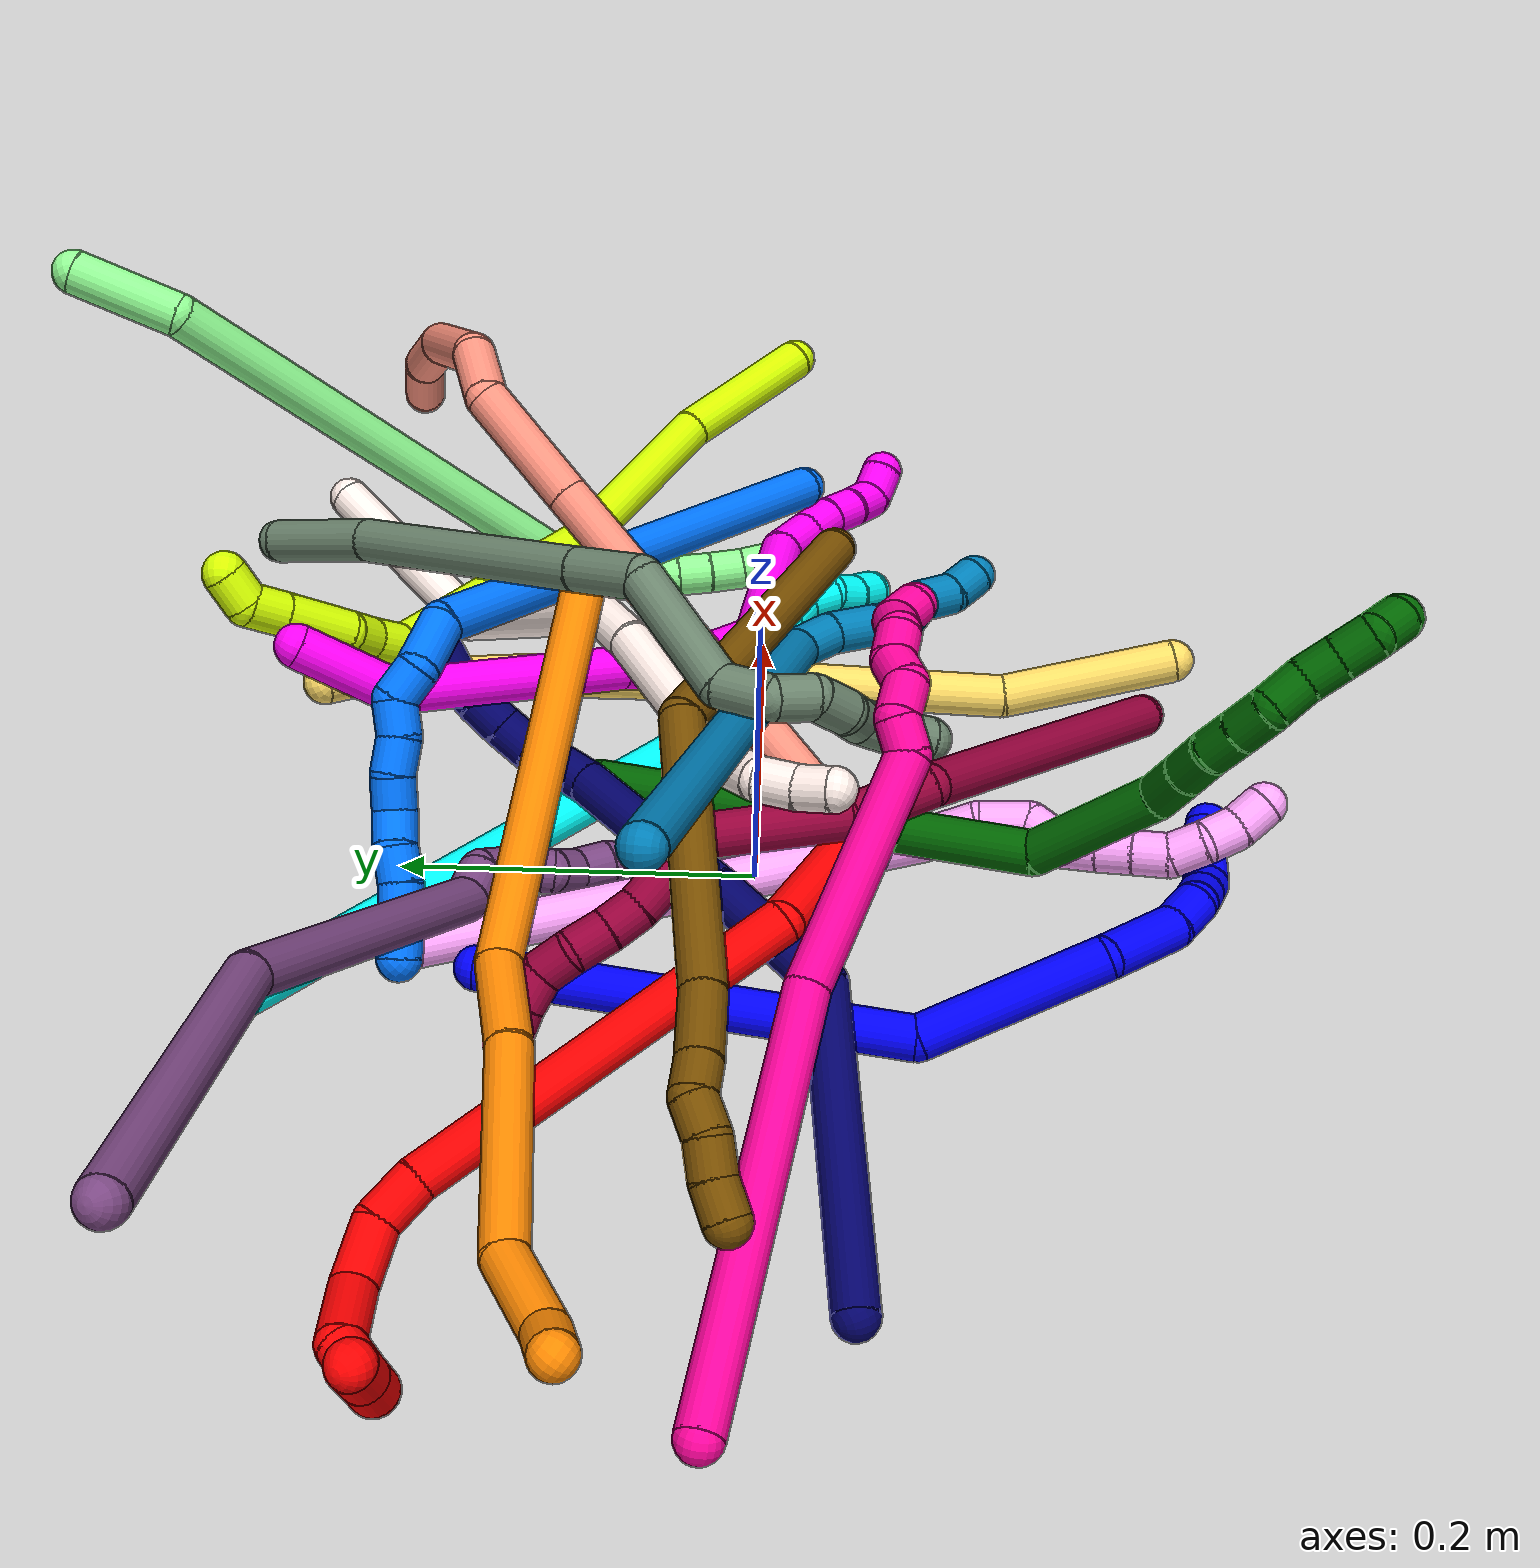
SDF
<sdf version="1.7">
 <world name="default">
  <plugin name="TubeGeneratorPlugin" filename="libtube_generator_plugin.so"/>
  <model name="photoneo_s_sensor">
   <static>1</static>
   <pose>0 0 2 1.57079 1.57079 3.14159</pose>
   <link name="link">
    <inertial><mass>0.1</mass></inertial>
    <sensor name="sensor" type="depth">
     <update_rate>30</update_rate>
     <camera>
      <horizontal_fov>1.22</horizontal_fov>
      <image><width>1920</width><height>1200</height><format>B8G8R8</format></image>
      <clip><near>0.1</near><far>4</far></clip>
      <depth_camera><output>points</output></depth_camera>
     </camera>
     <plugin name="camera_plugin" filename="libgazebo_ros_depth_camera.so">
      <baseline>0.2</baseline>
      <alwaysOn>1</alwaysOn>
      <updateRate>0.0</updateRate>
      <cameraName>camera_ir</cameraName>
      <imageTopicName>/camera/color/image_raw</imageTopicName>
      <cameraInfoTopicName>/camera/color/camera_info</cameraInfoTopicName>
      <depthImageTopicName>/camera/depth/image_raw</depthImageTopicName>
      <depthImageCameraInfoTopicName>/camera/depth/camera_info</depthImageCameraInfoTopicName>
      <pointCloudTopicName>/camera/depth/points</pointCloudTopicName>
      <frameName>fr_optical</frameName>
      <pointCloudCutoff>0.1</pointCloudCutoff>
      <pointCloudCutoffMax>2.0</pointCloudCutoffMax>
      <distortionK1>0</distortionK1>
      <distortionK2>0</distortionK2>
      <distortionK3>0</distortionK3>
      <distortionT1>0</distortionT1>
      <distortionT2>0</distortionT2>
      <CxPrime>0</CxPrime>
      <Cx>0</Cx>
      <Cy>0</Cy>
      <focalLength>0</focalLength>
      <hackBaseline>0</hackBaseline>
     </plugin>
    </sensor>
   </link>
  </model>
  <gravity>0 0 -9.8</gravity>
  <magnetic_field>6e-06 2.3e-05 -4.2e-05</magnetic_field>
  <atmosphere type="adiabatic"/>
  <physics name="default_physics" default="0" type="ode">
   <max_step_size>0.003</max_step_size>
   <real_time_factor>1</real_time_factor>
   <real_time_update_rate>1000</real_time_update_rate>
   <max_contacts>10000</max_contacts>
   <ode>
    <solver>
     <type>quick</type>
     <iters>100</iters>
     <sor>1.3</sor>
     <use_dynamic_moi_rescaling>0</use_dynamic_moi_rescaling>
    </solver>
    <constraints>
     <contact_max_correcting_vel>0</contact_max_correcting_vel>
     <contact_surface_layer>0.001</contact_surface_layer>
     <cfm>0</cfm>
     <erp>0.2</erp>
    </constraints>
   </ode>
  </physics>
  <scene><ambient>0.4 0.4 0.4 1</ambient><background>0.7 0.7 0.7 1</background><shadows>0</shadows></scene>
  <audio><device>default</device></audio>
  <spherical_coordinates>
   <surface_model>EARTH_WGS84</surface_model>
   <latitude_deg>0</latitude_deg>
   <longitude_deg>0</longitude_deg>
   <elevation>0</elevation>
   <heading_deg>0</heading_deg>
  </spherical_coordinates>
  <model name="bin">
   <static>1</static>
   <link name="bottom">
    <collision name="collision-bottom">
     <pose>0 0 -0.01 0 -0 0</pose>
     <geometry><box><size>0.8 0.6 0.02</size></box></geometry>
     <surface>
      <friction><ode><mu>100</mu><mu2>100</mu2></ode></friction>
      <contact><collide_bitmask>65535</collide_bitmask></contact>
     </surface>
    </collision>
   </link>
   <link name="west_wall">
    <collision name="collision-west_wall">
     <pose>-0.41 0 0.1 0 -0 0</pose>
     <geometry><box><size>0.02 0.6 0.2</size></box></geometry>
     <surface>
      <friction><ode><mu>100</mu><mu2>100</mu2></ode></friction>
      <contact><collide_bitmask>65535</collide_bitmask></contact>
     </surface>
    </collision>
   </link>
   <link name="east_wall">
    <collision name="collision-east_wall">
     <pose>0.41 0 0.1 0 -0 0</pose>
     <geometry><box><size>0.02 0.6 0.2</size></box></geometry>
     <surface>
      <friction><ode><mu>100</mu><mu2>100</mu2></ode></friction>
      <contact><collide_bitmask>65535</collide_bitmask></contact>
     </surface>
    </collision>
   </link>
   <link name="south_wall">
    <collision name="collision-south_wall">
     <pose>0 -0.31 0.1 0 -0 0</pose>
     <geometry><box><size>0.8 0.02 0.2</size></box></geometry>
     <surface>
      <friction><ode><mu>100</mu><mu2>100</mu2></ode></friction>
      <contact><collide_bitmask>65535</collide_bitmask></contact>
     </surface>
    </collision>
   </link>
   <link name="north_wall">
    <collision name="collision-north_wall">
     <pose>0 0.31 0.1 0 -0 0</pose>
     <geometry><box><size>0.8 0.02 0.2</size></box></geometry>
     <surface>
      <friction><ode><mu>100</mu><mu2>100</mu2></ode></friction>
      <contact><collide_bitmask>65535</collide_bitmask></contact>
     </surface>
    </collision>
   </link>
  </model>
  <model name="1">
   <static>0</static>
   <link name="1">
    <collision name="collision-cylinder-e_1_1_4">
     <pose>-0.004922 -0.018385 0.117868 0.154731 -0.041232 -0.003197</pose>
     <geometry><cylinder><radius>0.0125</radius><length>0.23879</length></cylinder></geometry>
     <surface>
      <friction><ode><mu>1.16</mu><mu2>1.16</mu2><slip1>0</slip1><slip2>0</slip2></ode></friction>
      <contact><ode><kp>1e+06</kp><kd>1</kd><max_vel>0</max_vel><min_depth>0.001</min_depth></ode></contact>
     </surface>
    </collision>
    <visual name="visual-cylinder-e_1_1_4">
     <pose>-0.004922 -0.018385 0.117868 0.154731 -0.041232 -0.003197</pose>
     <geometry><cylinder><radius>0.0125</radius><length>0.23879</length></cylinder></geometry>
     <material><ambient>0 0 1 1</ambient></material>
    </visual>
    <collision name="collision-cylinder-e_2_4_5">
     <pose>0.00322 -0.068628 0.277257 0.65447 0.244614 0.0834</pose>
     <geometry><cylinder><radius>0.0125</radius><length>0.10788</length></cylinder></geometry>
     <surface>
      <friction><ode><mu>1.16</mu><mu2>1.16</mu2><slip1>0</slip1><slip2>0</slip2></ode></friction>
      <contact><ode><kp>1e+06</kp><kd>1</kd><max_vel>0</max_vel><min_depth>0.001</min_depth></ode></contact>
     </surface>
    </collision>
    <visual name="visual-cylinder-e_2_4_5">
     <pose>0.00322 -0.068628 0.277257 0.65447 0.244614 0.0834</pose>
     <geometry><cylinder><radius>0.0125</radius><length>0.10788</length></cylinder></geometry>
     <material><ambient>0 0 1 1</ambient></material>
    </visual>
    <collision name="collision-cylinder-e_3_5_6">
     <pose>0.012716 -0.120913 0.33195 0.998058 -0.145716 -0.07952</pose>
     <geometry><cylinder><radius>0.0125</radius><length>0.049133</length></cylinder></geometry>
     <surface>
      <friction><ode><mu>1.16</mu><mu2>1.16</mu2><slip1>0</slip1><slip2>0</slip2></ode></friction>
      <contact><ode><kp>1e+06</kp><kd>1</kd><max_vel>0</max_vel><min_depth>0.001</min_depth></ode></contact>
     </surface>
    </collision>
    <visual name="visual-cylinder-e_3_5_6">
     <pose>0.012716 -0.120913 0.33195 0.998058 -0.145716 -0.07952</pose>
     <geometry><cylinder><radius>0.0125</radius><length>0.049133</length></cylinder></geometry>
     <material><ambient>0 0 1 1</ambient></material>
    </visual>
    <collision name="collision-cylinder-e_4_6_7">
     <pose>0.008864 -0.152573 0.348676 1.26436 -0.024236 -0.017753</pose>
     <geometry><cylinder><radius>0.0125</radius><length>0.023569</length></cylinder></geometry>
     <surface>
      <friction><ode><mu>1.16</mu><mu2>1.16</mu2><slip1>0</slip1><slip2>0</slip2></ode></friction>
      <contact><ode><kp>1e+06</kp><kd>1</kd><max_vel>0</max_vel><min_depth>0.001</min_depth></ode></contact>
     </surface>
    </collision>
    <visual name="visual-cylinder-e_4_6_7">
     <pose>0.008864 -0.152573 0.348676 1.26436 -0.024236 -0.017753</pose>
     <geometry><cylinder><radius>0.0125</radius><length>0.023569</length></cylinder></geometry>
     <material><ambient>0 0 1 1</ambient></material>
    </visual>
    <collision name="collision-cylinder-e_5_7_8">
     <pose>0.003843 -0.172713 0.352227 1.57115 -0.488603 -0.48877</pose>
     <geometry><cylinder><radius>0.0125</radius><length>0.020177</length></cylinder></geometry>
     <surface>
      <friction><ode><mu>1.16</mu><mu2>1.16</mu2><slip1>0</slip1><slip2>0</slip2></ode></friction>
      <contact><ode><kp>1e+06</kp><kd>1</kd><max_vel>0</max_vel><min_depth>0.001</min_depth></ode></contact>
     </surface>
    </collision>
    <visual name="visual-cylinder-e_5_7_8">
     <pose>0.003843 -0.172713 0.352227 1.57115 -0.488603 -0.48877</pose>
     <geometry><cylinder><radius>0.0125</radius><length>0.020177</length></cylinder></geometry>
     <material><ambient>0 0 1 1</ambient></material>
    </visual>
    <collision name="collision-cylinder-e_6_8_9">
     <pose>-0.005498 -0.190725 0.352045 1.59045 -0.468273 -0.477223</pose>
     <geometry><cylinder><radius>0.0125</radius><length>0.020409</length></cylinder></geometry>
     <surface>
      <friction><ode><mu>1.16</mu><mu2>1.16</mu2><slip1>0</slip1><slip2>0</slip2></ode></friction>
      <contact><ode><kp>1e+06</kp><kd>1</kd><max_vel>0</max_vel><min_depth>0.001</min_depth></ode></contact>
     </surface>
    </collision>
    <visual name="visual-cylinder-e_6_8_9">
     <pose>-0.005498 -0.190725 0.352045 1.59045 -0.468273 -0.477223</pose>
     <geometry><cylinder><radius>0.0125</radius><length>0.020409</length></cylinder></geometry>
     <material><ambient>0 0 1 1</ambient></material>
    </visual>
    <collision name="collision-cylinder-e_7_9_10">
     <pose>-0.008739 -0.209291 0.348928 1.87185 0.136949 0.185675</pose>
     <geometry><cylinder><radius>0.0125</radius><length>0.020002</length></cylinder></geometry>
     <surface>
      <friction><ode><mu>1.16</mu><mu2>1.16</mu2><slip1>0</slip1><slip2>0</slip2></ode></friction>
      <contact><ode><kp>1e+06</kp><kd>1</kd><max_vel>0</max_vel><min_depth>0.001</min_depth></ode></contact>
     </surface>
    </collision>
    <visual name="visual-cylinder-e_7_9_10">
     <pose>-0.008739 -0.209291 0.348928 1.87185 0.136949 0.185675</pose>
     <geometry><cylinder><radius>0.0125</radius><length>0.020002</length></cylinder></geometry>
     <material><ambient>0 0 1 1</ambient></material>
    </visual>
    <collision name="collision-cylinder-e_8_10_2">
     <pose>-0.004071 -0.228122 0.344681 1.7096 0.335924 0.384962</pose>
     <geometry><cylinder><radius>0.0125</radius><length>0.02004</length></cylinder></geometry>
     <surface>
      <friction><ode><mu>1.16</mu><mu2>1.16</mu2><slip1>0</slip1><slip2>0</slip2></ode></friction>
      <contact><ode><kp>1e+06</kp><kd>1</kd><max_vel>0</max_vel><min_depth>0.001</min_depth></ode></contact>
     </surface>
    </collision>
    <visual name="visual-cylinder-e_8_10_2">
     <pose>-0.004071 -0.228122 0.344681 1.7096 0.335924 0.384962</pose>
     <geometry><cylinder><radius>0.0125</radius><length>0.02004</length></cylinder></geometry>
     <material><ambient>0 0 1 1</ambient></material>
    </visual>
    <collision name="collision-sphere-2">
     <pose>-0.000768 -0.237491 0.343372 0 -0 0</pose>
     <geometry><sphere><radius>0.0125</radius></sphere></geometry>
     <surface>
      <friction><ode><mu>1.16</mu><mu2>1.16</mu2><slip1>0</slip1><slip2>0</slip2></ode></friction>
      <contact><ode><kp>1e+06</kp><kd>1</kd><max_vel>0</max_vel><min_depth>0.001</min_depth></ode></contact>
     </surface>
    </collision>
    <visual name="visual-sphere-2">
     <pose>-0.000768 -0.237491 0.343372 0 -0 0</pose>
     <geometry><sphere><radius>0.0125</radius></sphere></geometry>
     <material><ambient>0 0 1 1</ambient></material>
    </visual>
    <collision name="collision-sphere-10">
     <pose>-0.007374 -0.218753 0.34599 0 -0 0</pose>
     <geometry><sphere><radius>0.0125</radius></sphere></geometry>
     <surface>
      <friction><ode><mu>1.16</mu><mu2>1.16</mu2><slip1>0</slip1><slip2>0</slip2></ode></friction>
      <contact><ode><kp>1e+06</kp><kd>1</kd><max_vel>0</max_vel><min_depth>0.001</min_depth></ode></contact>
     </surface>
    </collision>
    <visual name="visual-sphere-10">
     <pose>-0.007374 -0.218753 0.34599 0 -0 0</pose>
     <geometry><sphere><radius>0.0125</radius></sphere></geometry>
     <material><ambient>0 0 1 1</ambient></material>
    </visual>
    <collision name="collision-sphere-9">
     <pose>-0.010104 -0.199829 0.351866 0 -0 0</pose>
     <geometry><sphere><radius>0.0125</radius></sphere></geometry>
     <surface>
      <friction><ode><mu>1.16</mu><mu2>1.16</mu2><slip1>0</slip1><slip2>0</slip2></ode></friction>
      <contact><ode><kp>1e+06</kp><kd>1</kd><max_vel>0</max_vel><min_depth>0.001</min_depth></ode></contact>
     </surface>
    </collision>
    <visual name="visual-sphere-9">
     <pose>-0.010104 -0.199829 0.351866 0 -0 0</pose>
     <geometry><sphere><radius>0.0125</radius></sphere></geometry>
     <material><ambient>0 0 1 1</ambient></material>
    </visual>
    <collision name="collision-sphere-4">
     <pose>-0.009843 -0.03677 0.235737 0 -0 0</pose>
     <geometry><sphere><radius>0.0125</radius></sphere></geometry>
     <surface>
      <friction><ode><mu>1.16</mu><mu2>1.16</mu2><slip1>0</slip1><slip2>0</slip2></ode></friction>
      <contact><ode><kp>1e+06</kp><kd>1</kd><max_vel>0</max_vel><min_depth>0.001</min_depth></ode></contact>
     </surface>
    </collision>
    <visual name="visual-sphere-4">
     <pose>-0.009843 -0.03677 0.235737 0 -0 0</pose>
     <geometry><sphere><radius>0.0125</radius></sphere></geometry>
     <material><ambient>0 0 1 1</ambient></material>
    </visual>
    <collision name="collision-sphere-1">
     <geometry><sphere><radius>0.0125</radius></sphere></geometry>
     <surface>
      <friction><ode><mu>1.16</mu><mu2>1.16</mu2><slip1>0</slip1><slip2>0</slip2></ode></friction>
      <contact><ode><kp>1e+06</kp><kd>1</kd><max_vel>0</max_vel><min_depth>0.001</min_depth></ode></contact>
     </surface>
    </collision>
    <visual name="visual-sphere-1">
     <geometry><sphere><radius>0.0125</radius></sphere></geometry>
     <material><ambient>0 0 1 1</ambient></material>
    </visual>
    <collision name="collision-sphere-8">
     <pose>-0.000893 -0.181621 0.352224 0 -0 0</pose>
     <geometry><sphere><radius>0.0125</radius></sphere></geometry>
     <surface>
      <friction><ode><mu>1.16</mu><mu2>1.16</mu2><slip1>0</slip1><slip2>0</slip2></ode></friction>
      <contact><ode><kp>1e+06</kp><kd>1</kd><max_vel>0</max_vel><min_depth>0.001</min_depth></ode></contact>
     </surface>
    </collision>
    <visual name="visual-sphere-8">
     <pose>-0.000893 -0.181621 0.352224 0 -0 0</pose>
     <geometry><sphere><radius>0.0125</radius></sphere></geometry>
     <material><ambient>0 0 1 1</ambient></material>
    </visual>
    <collision name="collision-sphere-5">
     <pose>0.016284 -0.100485 0.318777 0 -0 0</pose>
     <geometry><sphere><radius>0.0125</radius></sphere></geometry>
     <surface>
      <friction><ode><mu>1.16</mu><mu2>1.16</mu2><slip1>0</slip1><slip2>0</slip2></ode></friction>
      <contact><ode><kp>1e+06</kp><kd>1</kd><max_vel>0</max_vel><min_depth>0.001</min_depth></ode></contact>
     </surface>
    </collision>
    <visual name="visual-sphere-5">
     <pose>0.016284 -0.100485 0.318777 0 -0 0</pose>
     <geometry><sphere><radius>0.0125</radius></sphere></geometry>
     <material><ambient>0 0 1 1</ambient></material>
    </visual>
    <collision name="collision-sphere-6">
     <pose>0.009149 -0.14134 0.345122 0 -0 0</pose>
     <geometry><sphere><radius>0.0125</radius></sphere></geometry>
     <surface>
      <friction><ode><mu>1.16</mu><mu2>1.16</mu2><slip1>0</slip1><slip2>0</slip2></ode></friction>
      <contact><ode><kp>1e+06</kp><kd>1</kd><max_vel>0</max_vel><min_depth>0.001</min_depth></ode></contact>
     </surface>
    </collision>
    <visual name="visual-sphere-6">
     <pose>0.009149 -0.14134 0.345122 0 -0 0</pose>
     <geometry><sphere><radius>0.0125</radius></sphere></geometry>
     <material><ambient>0 0 1 1</ambient></material>
    </visual>
    <collision name="collision-sphere-7">
     <pose>0.008578 -0.163805 0.35223 0 -0 0</pose>
     <geometry><sphere><radius>0.0125</radius></sphere></geometry>
     <surface>
      <friction><ode><mu>1.16</mu><mu2>1.16</mu2><slip1>0</slip1><slip2>0</slip2></ode></friction>
      <contact><ode><kp>1e+06</kp><kd>1</kd><max_vel>0</max_vel><min_depth>0.001</min_depth></ode></contact>
     </surface>
    </collision>
    <visual name="visual-sphere-7">
     <pose>0.008578 -0.163805 0.35223 0 -0 0</pose>
     <geometry><sphere><radius>0.0125</radius></sphere></geometry>
     <material><ambient>0 0 1 1</ambient></material>
    </visual>
    <inertial>
     <pose>-0.00057 -0.074931 0.221525 0 -0 0</pose>
     <mass>0.5</mass>
     <inertia>
      <ixx>0.001271</ixx>
      <ixy>0</ixy>
      <ixz>0</ixz>
      <iyy>0.00121</iyy>
      <iyz>0</iyz>
      <izz>0.000308</izz>
     </inertia>
    </inertial>
   </link>
   <pose>-0.085296 0.14758 0.011571 0.514409 -1.51863 0.734592</pose>
  </model>
  <model name="2">
   <static>0</static>
   <link name="2">
    <collision name="collision-cylinder-e_1_1_4">
     <pose>-0.006395 0.008634 0.040866 -0.20822 -0.15194 0.015906</pose>
     <geometry><cylinder><radius>0.0125</radius><length>0.084509</length></cylinder></geometry>
     <surface>
      <friction><ode><mu>1.16</mu><mu2>1.16</mu2><slip1>0</slip1><slip2>0</slip2></ode></friction>
      <contact><ode><kp>1e+06</kp><kd>1</kd><max_vel>0</max_vel><min_depth>0.001</min_depth></ode></contact>
     </surface>
    </collision>
    <visual name="visual-cylinder-e_1_1_4">
     <pose>-0.006395 0.008634 0.040866 -0.20822 -0.15194 0.015906</pose>
     <geometry><cylinder><radius>0.0125</radius><length>0.084509</length></cylinder></geometry>
     <material><ambient>1 0 0 1</ambient></material>
    </visual>
    <collision name="collision-cylinder-e_2_4_5">
     <pose>0.011722 0.091301 0.162897 -0.739464 0.219533 -0.085373</pose>
     <geometry><cylinder><radius>0.0125</radius><length>0.225119</length></cylinder></geometry>
     <surface>
      <friction><ode><mu>1.16</mu><mu2>1.16</mu2><slip1>0</slip1><slip2>0</slip2></ode></friction>
      <contact><ode><kp>1e+06</kp><kd>1</kd><max_vel>0</max_vel><min_depth>0.001</min_depth></ode></contact>
     </surface>
    </collision>
    <visual name="visual-cylinder-e_2_4_5">
     <pose>0.011722 0.091301 0.162897 -0.739464 0.219533 -0.085373</pose>
     <geometry><cylinder><radius>0.0125</radius><length>0.225119</length></cylinder></geometry>
     <material><ambient>1 0 0 1</ambient></material>
    </visual>
    <collision name="collision-cylinder-e_3_5_6">
     <pose>0.036102 0.174249 0.255136 -0.677919 -0.009272 0.003269</pose>
     <geometry><cylinder><radius>0.0125</radius><length>0.028433</length></cylinder></geometry>
     <surface>
      <friction><ode><mu>1.16</mu><mu2>1.16</mu2><slip1>0</slip1><slip2>0</slip2></ode></friction>
      <contact><ode><kp>1e+06</kp><kd>1</kd><max_vel>0</max_vel><min_depth>0.001</min_depth></ode></contact>
     </surface>
    </collision>
    <visual name="visual-cylinder-e_3_5_6">
     <pose>0.036102 0.174249 0.255136 -0.677919 -0.009272 0.003269</pose>
     <geometry><cylinder><radius>0.0125</radius><length>0.028433</length></cylinder></geometry>
     <material><ambient>1 0 0 1</ambient></material>
    </visual>
    <collision name="collision-cylinder-e_4_6_7">
     <pose>0.028723 0.192768 0.278239 -0.673677 -0.440032 0.156308</pose>
     <geometry><cylinder><radius>0.0125</radius><length>0.034029</length></cylinder></geometry>
     <surface>
      <friction><ode><mu>1.16</mu><mu2>1.16</mu2><slip1>0</slip1><slip2>0</slip2></ode></friction>
      <contact><ode><kp>1e+06</kp><kd>1</kd><max_vel>0</max_vel><min_depth>0.001</min_depth></ode></contact>
     </surface>
    </collision>
    <visual name="visual-cylinder-e_4_6_7">
     <pose>0.028723 0.192768 0.278239 -0.673677 -0.440032 0.156308</pose>
     <geometry><cylinder><radius>0.0125</radius><length>0.034029</length></cylinder></geometry>
     <material><ambient>1 0 0 1</ambient></material>
    </visual>
    <collision name="collision-cylinder-e_5_7_8">
     <pose>0.010641 0.200952 0.308679 0.076975 -0.530639 -0.020926</pose>
     <geometry><cylinder><radius>0.0125</radius><length>0.042816</length></cylinder></geometry>
     <surface>
      <friction><ode><mu>1.16</mu><mu2>1.16</mu2><slip1>0</slip1><slip2>0</slip2></ode></friction>
      <contact><ode><kp>1e+06</kp><kd>1</kd><max_vel>0</max_vel><min_depth>0.001</min_depth></ode></contact>
     </surface>
    </collision>
    <visual name="visual-cylinder-e_5_7_8">
     <pose>0.010641 0.200952 0.308679 0.076975 -0.530639 -0.020926</pose>
     <geometry><cylinder><radius>0.0125</radius><length>0.042816</length></cylinder></geometry>
     <material><ambient>1 0 0 1</ambient></material>
    </visual>
    <collision name="collision-cylinder-e_6_8_9">
     <pose>-0.009778 0.198626 0.330664 0.248191 -1.20339 -0.170878</pose>
     <geometry><cylinder><radius>0.0125</radius><length>0.020541</length></cylinder></geometry>
     <surface>
      <friction><ode><mu>1.16</mu><mu2>1.16</mu2><slip1>0</slip1><slip2>0</slip2></ode></friction>
      <contact><ode><kp>1e+06</kp><kd>1</kd><max_vel>0</max_vel><min_depth>0.001</min_depth></ode></contact>
     </surface>
    </collision>
    <visual name="visual-cylinder-e_6_8_9">
     <pose>-0.009778 0.198626 0.330664 0.248191 -1.20339 -0.170878</pose>
     <geometry><cylinder><radius>0.0125</radius><length>0.020541</length></cylinder></geometry>
     <material><ambient>1 0 0 1</ambient></material>
    </visual>
    <collision name="collision-cylinder-e_7_9_10">
     <pose>-0.026512 0.19152 0.341688 0.694219 -0.635636 -0.236899</pose>
     <geometry><cylinder><radius>0.0125</radius><length>0.024083</length></cylinder></geometry>
     <surface>
      <friction><ode><mu>1.16</mu><mu2>1.16</mu2><slip1>0</slip1><slip2>0</slip2></ode></friction>
      <contact><ode><kp>1e+06</kp><kd>1</kd><max_vel>0</max_vel><min_depth>0.001</min_depth></ode></contact>
     </surface>
    </collision>
    <visual name="visual-cylinder-e_7_9_10">
     <pose>-0.026512 0.19152 0.341688 0.694219 -0.635636 -0.236899</pose>
     <geometry><cylinder><radius>0.0125</radius><length>0.024083</length></cylinder></geometry>
     <material><ambient>1 0 0 1</ambient></material>
    </visual>
    <collision name="collision-cylinder-e_8_10_11">
     <pose>-0.032298 0.177971 0.356034 0.817057 0.134327 0.058219</pose>
     <geometry><cylinder><radius>0.0125</radius><length>0.020345</length></cylinder></geometry>
     <surface>
      <friction><ode><mu>1.16</mu><mu2>1.16</mu2><slip1>0</slip1><slip2>0</slip2></ode></friction>
      <contact><ode><kp>1e+06</kp><kd>1</kd><max_vel>0</max_vel><min_depth>0.001</min_depth></ode></contact>
     </surface>
    </collision>
    <visual name="visual-cylinder-e_8_10_11">
     <pose>-0.032298 0.177971 0.356034 0.817057 0.134327 0.058219</pose>
     <geometry><cylinder><radius>0.0125</radius><length>0.020345</length></cylinder></geometry>
     <material><ambient>1 0 0 1</ambient></material>
    </visual>
    <collision name="collision-cylinder-e_9_11_2">
     <pose>-0.02973 0.16351 0.369951 0.791863 0.120106 0.050255</pose>
     <geometry><cylinder><radius>0.0125</radius><length>0.020126</length></cylinder></geometry>
     <surface>
      <friction><ode><mu>1.16</mu><mu2>1.16</mu2><slip1>0</slip1><slip2>0</slip2></ode></friction>
      <contact><ode><kp>1e+06</kp><kd>1</kd><max_vel>0</max_vel><min_depth>0.001</min_depth></ode></contact>
     </surface>
    </collision>
    <visual name="visual-cylinder-e_9_11_2">
     <pose>-0.02973 0.16351 0.369951 0.791863 0.120106 0.050255</pose>
     <geometry><cylinder><radius>0.0125</radius><length>0.020126</length></cylinder></geometry>
     <material><ambient>1 0 0 1</ambient></material>
    </visual>
    <collision name="collision-sphere-2">
     <pose>-0.028525 0.156401 0.37697 0 -0 0</pose>
     <geometry><sphere><radius>0.0125</radius></sphere></geometry>
     <surface>
      <friction><ode><mu>1.16</mu><mu2>1.16</mu2><slip1>0</slip1><slip2>0</slip2></ode></friction>
      <contact><ode><kp>1e+06</kp><kd>1</kd><max_vel>0</max_vel><min_depth>0.001</min_depth></ode></contact>
     </surface>
    </collision>
    <visual name="visual-sphere-2">
     <pose>-0.028525 0.156401 0.37697 0 -0 0</pose>
     <geometry><sphere><radius>0.0125</radius></sphere></geometry>
     <material><ambient>1 0 0 1</ambient></material>
    </visual>
    <collision name="collision-sphere-11">
     <pose>-0.030936 0.17062 0.362933 0 -0 0</pose>
     <geometry><sphere><radius>0.0125</radius></sphere></geometry>
     <surface>
      <friction><ode><mu>1.16</mu><mu2>1.16</mu2><slip1>0</slip1><slip2>0</slip2></ode></friction>
      <contact><ode><kp>1e+06</kp><kd>1</kd><max_vel>0</max_vel><min_depth>0.001</min_depth></ode></contact>
     </surface>
    </collision>
    <visual name="visual-sphere-11">
     <pose>-0.030936 0.17062 0.362933 0 -0 0</pose>
     <geometry><sphere><radius>0.0125</radius></sphere></geometry>
     <material><ambient>1 0 0 1</ambient></material>
    </visual>
    <collision name="collision-sphere-10">
     <pose>-0.033661 0.185321 0.349134 0 -0 0</pose>
     <geometry><sphere><radius>0.0125</radius></sphere></geometry>
     <surface>
      <friction><ode><mu>1.16</mu><mu2>1.16</mu2><slip1>0</slip1><slip2>0</slip2></ode></friction>
      <contact><ode><kp>1e+06</kp><kd>1</kd><max_vel>0</max_vel><min_depth>0.001</min_depth></ode></contact>
     </surface>
    </collision>
    <visual name="visual-sphere-10">
     <pose>-0.033661 0.185321 0.349134 0 -0 0</pose>
     <geometry><sphere><radius>0.0125</radius></sphere></geometry>
     <material><ambient>1 0 0 1</ambient></material>
    </visual>
    <collision name="collision-sphere-9">
     <pose>-0.019363 0.197719 0.334241 0 -0 0</pose>
     <geometry><sphere><radius>0.0125</radius></sphere></geometry>
     <surface>
      <friction><ode><mu>1.16</mu><mu2>1.16</mu2><slip1>0</slip1><slip2>0</slip2></ode></friction>
      <contact><ode><kp>1e+06</kp><kd>1</kd><max_vel>0</max_vel><min_depth>0.001</min_depth></ode></contact>
     </surface>
    </collision>
    <visual name="visual-sphere-9">
     <pose>-0.019363 0.197719 0.334241 0 -0 0</pose>
     <geometry><sphere><radius>0.0125</radius></sphere></geometry>
     <material><ambient>1 0 0 1</ambient></material>
    </visual>
    <collision name="collision-sphere-4">
     <pose>-0.012791 0.017268 0.081731 0 -0 0</pose>
     <geometry><sphere><radius>0.0125</radius></sphere></geometry>
     <surface>
      <friction><ode><mu>1.16</mu><mu2>1.16</mu2><slip1>0</slip1><slip2>0</slip2></ode></friction>
      <contact><ode><kp>1e+06</kp><kd>1</kd><max_vel>0</max_vel><min_depth>0.001</min_depth></ode></contact>
     </surface>
    </collision>
    <visual name="visual-sphere-4">
     <pose>-0.012791 0.017268 0.081731 0 -0 0</pose>
     <geometry><sphere><radius>0.0125</radius></sphere></geometry>
     <material><ambient>1 0 0 1</ambient></material>
    </visual>
    <collision name="collision-sphere-1">
     <geometry><sphere><radius>0.0125</radius></sphere></geometry>
     <surface>
      <friction><ode><mu>1.16</mu><mu2>1.16</mu2><slip1>0</slip1><slip2>0</slip2></ode></friction>
      <contact><ode><kp>1e+06</kp><kd>1</kd><max_vel>0</max_vel><min_depth>0.001</min_depth></ode></contact>
     </surface>
    </collision>
    <visual name="visual-sphere-1">
     <geometry><sphere><radius>0.0125</radius></sphere></geometry>
     <material><ambient>1 0 0 1</ambient></material>
    </visual>
    <collision name="collision-sphere-8">
     <pose>-0.000193 0.199532 0.327088 0 -0 0</pose>
     <geometry><sphere><radius>0.0125</radius></sphere></geometry>
     <surface>
      <friction><ode><mu>1.16</mu><mu2>1.16</mu2><slip1>0</slip1><slip2>0</slip2></ode></friction>
      <contact><ode><kp>1e+06</kp><kd>1</kd><max_vel>0</max_vel><min_depth>0.001</min_depth></ode></contact>
     </surface>
    </collision>
    <visual name="visual-sphere-8">
     <pose>-0.000193 0.199532 0.327088 0 -0 0</pose>
     <geometry><sphere><radius>0.0125</radius></sphere></geometry>
     <material><ambient>1 0 0 1</ambient></material>
    </visual>
    <collision name="collision-sphere-5">
     <pose>0.036234 0.165333 0.244063 0 -0 0</pose>
     <geometry><sphere><radius>0.0125</radius></sphere></geometry>
     <surface>
      <friction><ode><mu>1.16</mu><mu2>1.16</mu2><slip1>0</slip1><slip2>0</slip2></ode></friction>
      <contact><ode><kp>1e+06</kp><kd>1</kd><max_vel>0</max_vel><min_depth>0.001</min_depth></ode></contact>
     </surface>
    </collision>
    <visual name="visual-sphere-5">
     <pose>0.036234 0.165333 0.244063 0 -0 0</pose>
     <geometry><sphere><radius>0.0125</radius></sphere></geometry>
     <material><ambient>1 0 0 1</ambient></material>
    </visual>
    <collision name="collision-sphere-6">
     <pose>0.035971 0.183165 0.266208 0 -0 0</pose>
     <geometry><sphere><radius>0.0125</radius></sphere></geometry>
     <surface>
      <friction><ode><mu>1.16</mu><mu2>1.16</mu2><slip1>0</slip1><slip2>0</slip2></ode></friction>
      <contact><ode><kp>1e+06</kp><kd>1</kd><max_vel>0</max_vel><min_depth>0.001</min_depth></ode></contact>
     </surface>
    </collision>
    <visual name="visual-sphere-6">
     <pose>0.035971 0.183165 0.266208 0 -0 0</pose>
     <geometry><sphere><radius>0.0125</radius></sphere></geometry>
     <material><ambient>1 0 0 1</ambient></material>
    </visual>
    <collision name="collision-sphere-7">
     <pose>0.021475 0.202372 0.29027 0 -0 0</pose>
     <geometry><sphere><radius>0.0125</radius></sphere></geometry>
     <surface>
      <friction><ode><mu>1.16</mu><mu2>1.16</mu2><slip1>0</slip1><slip2>0</slip2></ode></friction>
      <contact><ode><kp>1e+06</kp><kd>1</kd><max_vel>0</max_vel><min_depth>0.001</min_depth></ode></contact>
     </surface>
    </collision>
    <visual name="visual-sphere-7">
     <pose>0.021475 0.202372 0.29027 0 -0 0</pose>
     <geometry><sphere><radius>0.0125</radius></sphere></geometry>
     <material><ambient>1 0 0 1</ambient></material>
    </visual>
    <inertial>
     <pose>0.004926 0.11401 0.199547 0 -0 0</pose>
     <mass>0.5</mass>
     <inertia>
      <ixx>0.000924</ixx>
      <ixy>0</ixy>
      <ixz>0</ixz>
      <iyy>0.000724</iyy>
      <iyz>0</iyz>
      <izz>-0.000806</izz>
     </inertia>
    </inertial>
   </link>
   <pose>-0.03452 -0.051134 0.064975 -1.13088 -0.216609 0.926719</pose>
  </model>
  <model name="3">
   <static>0</static>
   <link name="3">
    <collision name="collision-cylinder-e_1_1_4">
     <pose>0.088177 -0.107313 -0.09501 2.29546 0.551529 1.12219</pose>
     <geometry><cylinder><radius>0.0125</radius><length>0.33656</length></cylinder></geometry>
     <surface>
      <friction><ode><mu>1.16</mu><mu2>1.16</mu2><slip1>0</slip1><slip2>0</slip2></ode></friction>
      <contact><ode><kp>1e+06</kp><kd>1</kd><max_vel>0</max_vel><min_depth>0.001</min_depth></ode></contact>
     </surface>
    </collision>
    <visual name="visual-cylinder-e_1_1_4">
     <pose>0.088177 -0.107313 -0.09501 2.29546 0.551529 1.12219</pose>
     <geometry><cylinder><radius>0.0125</radius><length>0.33656</length></cylinder></geometry>
     <material><ambient>0.003922 1 0.996078 1</ambient></material>
    </visual>
    <collision name="collision-cylinder-e_2_4_5">
     <pose>0.183066 -0.219571 -0.195884 2.4409 0.718905 1.59874</pose>
     <geometry><cylinder><radius>0.0125</radius><length>0.020386</length></cylinder></geometry>
     <surface>
      <friction><ode><mu>1.16</mu><mu2>1.16</mu2><slip1>0</slip1><slip2>0</slip2></ode></friction>
      <contact><ode><kp>1e+06</kp><kd>1</kd><max_vel>0</max_vel><min_depth>0.001</min_depth></ode></contact>
     </surface>
    </collision>
    <visual name="visual-cylinder-e_2_4_5">
     <pose>0.183066 -0.219571 -0.195884 2.4409 0.718905 1.59874</pose>
     <geometry><cylinder><radius>0.0125</radius><length>0.020386</length></cylinder></geometry>
     <material><ambient>0.003922 1 0.996078 1</ambient></material>
    </visual>
    <collision name="collision-cylinder-e_3_5_6">
     <pose>0.198262 -0.231157 -0.202523 1.6871 0.903343 0.998142</pose>
     <geometry><cylinder><radius>0.0125</radius><length>0.021602</length></cylinder></geometry>
     <surface>
      <friction><ode><mu>1.16</mu><mu2>1.16</mu2><slip1>0</slip1><slip2>0</slip2></ode></friction>
      <contact><ode><kp>1e+06</kp><kd>1</kd><max_vel>0</max_vel><min_depth>0.001</min_depth></ode></contact>
     </surface>
    </collision>
    <visual name="visual-cylinder-e_3_5_6">
     <pose>0.198262 -0.231157 -0.202523 1.6871 0.903343 0.998142</pose>
     <geometry><cylinder><radius>0.0125</radius><length>0.021602</length></cylinder></geometry>
     <material><ambient>0.003922 1 0.996078 1</ambient></material>
    </visual>
    <collision name="collision-cylinder-e_4_6_7">
     <pose>0.215641 -0.243759 -0.203607 1.62253 0.979754 1.02334</pose>
     <geometry><cylinder><radius>0.0125</radius><length>0.021425</length></cylinder></geometry>
     <surface>
      <friction><ode><mu>1.16</mu><mu2>1.16</mu2><slip1>0</slip1><slip2>0</slip2></ode></friction>
      <contact><ode><kp>1e+06</kp><kd>1</kd><max_vel>0</max_vel><min_depth>0.001</min_depth></ode></contact>
     </surface>
    </collision>
    <visual name="visual-cylinder-e_4_6_7">
     <pose>0.215641 -0.243759 -0.203607 1.62253 0.979754 1.02334</pose>
     <geometry><cylinder><radius>0.0125</radius><length>0.021425</length></cylinder></geometry>
     <material><ambient>0.003922 1 0.996078 1</ambient></material>
    </visual>
    <collision name="collision-cylinder-e_5_7_8">
     <pose>0.23384 -0.252708 -0.206045 2.18989 1.1952 1.84544</pose>
     <geometry><cylinder><radius>0.0125</radius><length>0.020003</length></cylinder></geometry>
     <surface>
      <friction><ode><mu>1.16</mu><mu2>1.16</mu2><slip1>0</slip1><slip2>0</slip2></ode></friction>
      <contact><ode><kp>1e+06</kp><kd>1</kd><max_vel>0</max_vel><min_depth>0.001</min_depth></ode></contact>
     </surface>
    </collision>
    <visual name="visual-cylinder-e_5_7_8">
     <pose>0.23384 -0.252708 -0.206045 2.18989 1.1952 1.84544</pose>
     <geometry><cylinder><radius>0.0125</radius><length>0.020003</length></cylinder></geometry>
     <material><ambient>0.003922 1 0.996078 1</ambient></material>
    </visual>
    <collision name="collision-cylinder-e_6_8_9">
     <pose>0.250371 -0.261699 -0.211602 2.08972 0.807564 1.26903</pose>
     <geometry><cylinder><radius>0.0125</radius><length>0.020002</length></cylinder></geometry>
     <surface>
      <friction><ode><mu>1.16</mu><mu2>1.16</mu2><slip1>0</slip1><slip2>0</slip2></ode></friction>
      <contact><ode><kp>1e+06</kp><kd>1</kd><max_vel>0</max_vel><min_depth>0.001</min_depth></ode></contact>
     </surface>
    </collision>
    <visual name="visual-cylinder-e_6_8_9">
     <pose>0.250371 -0.261699 -0.211602 2.08972 0.807564 1.26903</pose>
     <geometry><cylinder><radius>0.0125</radius><length>0.020002</length></cylinder></geometry>
     <material><ambient>0.003922 1 0.996078 1</ambient></material>
    </visual>
    <collision name="collision-cylinder-e_7_9_10">
     <pose>0.261334 -0.27397 -0.221875 2.40011 0.38277 0.924822</pose>
     <geometry><cylinder><radius>0.0125</radius><length>0.02001</length></cylinder></geometry>
     <surface>
      <friction><ode><mu>1.16</mu><mu2>1.16</mu2><slip1>0</slip1><slip2>0</slip2></ode></friction>
      <contact><ode><kp>1e+06</kp><kd>1</kd><max_vel>0</max_vel><min_depth>0.001</min_depth></ode></contact>
     </surface>
    </collision>
    <visual name="visual-cylinder-e_7_9_10">
     <pose>0.261334 -0.27397 -0.221875 2.40011 0.38277 0.924822</pose>
     <geometry><cylinder><radius>0.0125</radius><length>0.02001</length></cylinder></geometry>
     <material><ambient>0.003922 1 0.996078 1</ambient></material>
    </visual>
    <collision name="collision-cylinder-e_8_10_11">
     <pose>0.269258 -0.282785 -0.237438 2.85737 0.431988 1.98593</pose>
     <geometry><cylinder><radius>0.0125</radius><length>0.020002</length></cylinder></geometry>
     <surface>
      <friction><ode><mu>1.16</mu><mu2>1.16</mu2><slip1>0</slip1><slip2>0</slip2></ode></friction>
      <contact><ode><kp>1e+06</kp><kd>1</kd><max_vel>0</max_vel><min_depth>0.001</min_depth></ode></contact>
     </surface>
    </collision>
    <visual name="visual-cylinder-e_8_10_11">
     <pose>0.269258 -0.282785 -0.237438 2.85737 0.431988 1.98593</pose>
     <geometry><cylinder><radius>0.0125</radius><length>0.020002</length></cylinder></geometry>
     <material><ambient>0.003922 1 0.996078 1</ambient></material>
    </visual>
    <collision name="collision-cylinder-e_9_11_2">
     <pose>0.279331 -0.287783 -0.253867 2.83374 0.628842 2.25129</pose>
     <geometry><cylinder><radius>0.0125</radius><length>0.020011</length></cylinder></geometry>
     <surface>
      <friction><ode><mu>1.16</mu><mu2>1.16</mu2><slip1>0</slip1><slip2>0</slip2></ode></friction>
      <contact><ode><kp>1e+06</kp><kd>1</kd><max_vel>0</max_vel><min_depth>0.001</min_depth></ode></contact>
     </surface>
    </collision>
    <visual name="visual-cylinder-e_9_11_2">
     <pose>0.279331 -0.287783 -0.253867 2.83374 0.628842 2.25129</pose>
     <geometry><cylinder><radius>0.0125</radius><length>0.020011</length></cylinder></geometry>
     <material><ambient>0.003922 1 0.996078 1</ambient></material>
    </visual>
    <collision name="collision-sphere-2">
     <pose>0.285216 -0.290235 -0.261578 0 -0 0</pose>
     <geometry><sphere><radius>0.0125</radius></sphere></geometry>
     <surface>
      <friction><ode><mu>1.16</mu><mu2>1.16</mu2><slip1>0</slip1><slip2>0</slip2></ode></friction>
      <contact><ode><kp>1e+06</kp><kd>1</kd><max_vel>0</max_vel><min_depth>0.001</min_depth></ode></contact>
     </surface>
    </collision>
    <visual name="visual-sphere-2">
     <pose>0.285216 -0.290235 -0.261578 0 -0 0</pose>
     <geometry><sphere><radius>0.0125</radius></sphere></geometry>
     <material><ambient>0.003922 1 0.996078 1</ambient></material>
    </visual>
    <collision name="collision-sphere-11">
     <pose>0.273446 -0.285332 -0.246156 0 -0 0</pose>
     <geometry><sphere><radius>0.0125</radius></sphere></geometry>
     <surface>
      <friction><ode><mu>1.16</mu><mu2>1.16</mu2><slip1>0</slip1><slip2>0</slip2></ode></friction>
      <contact><ode><kp>1e+06</kp><kd>1</kd><max_vel>0</max_vel><min_depth>0.001</min_depth></ode></contact>
     </surface>
    </collision>
    <visual name="visual-sphere-11">
     <pose>0.273446 -0.285332 -0.246156 0 -0 0</pose>
     <geometry><sphere><radius>0.0125</radius></sphere></geometry>
     <material><ambient>0.003922 1 0.996078 1</ambient></material>
    </visual>
    <collision name="collision-sphere-10">
     <pose>0.265071 -0.280238 -0.22872 0 -0 0</pose>
     <geometry><sphere><radius>0.0125</radius></sphere></geometry>
     <surface>
      <friction><ode><mu>1.16</mu><mu2>1.16</mu2><slip1>0</slip1><slip2>0</slip2></ode></friction>
      <contact><ode><kp>1e+06</kp><kd>1</kd><max_vel>0</max_vel><min_depth>0.001</min_depth></ode></contact>
     </surface>
    </collision>
    <visual name="visual-sphere-10">
     <pose>0.265071 -0.280238 -0.22872 0 -0 0</pose>
     <geometry><sphere><radius>0.0125</radius></sphere></geometry>
     <material><ambient>0.003922 1 0.996078 1</ambient></material>
    </visual>
    <collision name="collision-sphere-9">
     <pose>0.257598 -0.267702 -0.215031 0 -0 0</pose>
     <geometry><sphere><radius>0.0125</radius></sphere></geometry>
     <surface>
      <friction><ode><mu>1.16</mu><mu2>1.16</mu2><slip1>0</slip1><slip2>0</slip2></ode></friction>
      <contact><ode><kp>1e+06</kp><kd>1</kd><max_vel>0</max_vel><min_depth>0.001</min_depth></ode></contact>
     </surface>
    </collision>
    <visual name="visual-sphere-9">
     <pose>0.257598 -0.267702 -0.215031 0 -0 0</pose>
     <geometry><sphere><radius>0.0125</radius></sphere></geometry>
     <material><ambient>0.003922 1 0.996078 1</ambient></material>
    </visual>
    <collision name="collision-sphere-4">
     <pose>0.176354 -0.214625 -0.19002 0 -0 0</pose>
     <geometry><sphere><radius>0.0125</radius></sphere></geometry>
     <surface>
      <friction><ode><mu>1.16</mu><mu2>1.16</mu2><slip1>0</slip1><slip2>0</slip2></ode></friction>
      <contact><ode><kp>1e+06</kp><kd>1</kd><max_vel>0</max_vel><min_depth>0.001</min_depth></ode></contact>
     </surface>
    </collision>
    <visual name="visual-sphere-4">
     <pose>0.176354 -0.214625 -0.19002 0 -0 0</pose>
     <geometry><sphere><radius>0.0125</radius></sphere></geometry>
     <material><ambient>0.003922 1 0.996078 1</ambient></material>
    </visual>
    <collision name="collision-sphere-1">
     <geometry><sphere><radius>0.0125</radius></sphere></geometry>
     <surface>
      <friction><ode><mu>1.16</mu><mu2>1.16</mu2><slip1>0</slip1><slip2>0</slip2></ode></friction>
      <contact><ode><kp>1e+06</kp><kd>1</kd><max_vel>0</max_vel><min_depth>0.001</min_depth></ode></contact>
     </surface>
    </collision>
    <visual name="visual-sphere-1">
     <geometry><sphere><radius>0.0125</radius></sphere></geometry>
     <material><ambient>0.003922 1 0.996078 1</ambient></material>
    </visual>
    <collision name="collision-sphere-8">
     <pose>0.243144 -0.255695 -0.208174 0 -0 0</pose>
     <geometry><sphere><radius>0.0125</radius></sphere></geometry>
     <surface>
      <friction><ode><mu>1.16</mu><mu2>1.16</mu2><slip1>0</slip1><slip2>0</slip2></ode></friction>
      <contact><ode><kp>1e+06</kp><kd>1</kd><max_vel>0</max_vel><min_depth>0.001</min_depth></ode></contact>
     </surface>
    </collision>
    <visual name="visual-sphere-8">
     <pose>0.243144 -0.255695 -0.208174 0 -0 0</pose>
     <geometry><sphere><radius>0.0125</radius></sphere></geometry>
     <material><ambient>0.003922 1 0.996078 1</ambient></material>
    </visual>
    <collision name="collision-sphere-5">
     <pose>0.189779 -0.224516 -0.201747 0 -0 0</pose>
     <geometry><sphere><radius>0.0125</radius></sphere></geometry>
     <surface>
      <friction><ode><mu>1.16</mu><mu2>1.16</mu2><slip1>0</slip1><slip2>0</slip2></ode></friction>
      <contact><ode><kp>1e+06</kp><kd>1</kd><max_vel>0</max_vel><min_depth>0.001</min_depth></ode></contact>
     </surface>
    </collision>
    <visual name="visual-sphere-5">
     <pose>0.189779 -0.224516 -0.201747 0 -0 0</pose>
     <geometry><sphere><radius>0.0125</radius></sphere></geometry>
     <material><ambient>0.003922 1 0.996078 1</ambient></material>
    </visual>
    <collision name="collision-sphere-6">
     <pose>0.206745 -0.237797 -0.203299 0 -0 0</pose>
     <geometry><sphere><radius>0.0125</radius></sphere></geometry>
     <surface>
      <friction><ode><mu>1.16</mu><mu2>1.16</mu2><slip1>0</slip1><slip2>0</slip2></ode></friction>
      <contact><ode><kp>1e+06</kp><kd>1</kd><max_vel>0</max_vel><min_depth>0.001</min_depth></ode></contact>
     </surface>
    </collision>
    <visual name="visual-sphere-6">
     <pose>0.206745 -0.237797 -0.203299 0 -0 0</pose>
     <geometry><sphere><radius>0.0125</radius></sphere></geometry>
     <material><ambient>0.003922 1 0.996078 1</ambient></material>
    </visual>
    <collision name="collision-sphere-7">
     <pose>0.224536 -0.24972 -0.203916 0 -0 0</pose>
     <geometry><sphere><radius>0.0125</radius></sphere></geometry>
     <surface>
      <friction><ode><mu>1.16</mu><mu2>1.16</mu2><slip1>0</slip1><slip2>0</slip2></ode></friction>
      <contact><ode><kp>1e+06</kp><kd>1</kd><max_vel>0</max_vel><min_depth>0.001</min_depth></ode></contact>
     </surface>
    </collision>
    <visual name="visual-sphere-7">
     <pose>0.224536 -0.24972 -0.203916 0 -0 0</pose>
     <geometry><sphere><radius>0.0125</radius></sphere></geometry>
     <material><ambient>0.003922 1 0.996078 1</ambient></material>
    </visual>
    <inertial>
     <pose>0.136403 -0.155991 -0.13466 0 -0 0</pose>
     <mass>0.5</mass>
     <inertia><ixx>0.003657</ixx><ixy>0</ixy><ixz>0</ixz><iyy>0.00265</iyy><iyz>0</iyz><izz>0.00034</izz></inertia>
    </inertial>
   </link>
   <pose>-0.109399 0.26892 0.011567 -0.716328 -0.025015 0.177683</pose>
  </model>
  <model name="4">
   <static>0</static>
   <link name="4">
    <collision name="collision-cylinder-e_1_1_4">
     <pose>0.042194 -0.114447 -0.083614 2.20176 0.289339 0.558725</pose>
     <geometry><cylinder><radius>0.0125</radius><length>0.295768</length></cylinder></geometry>
     <surface>
      <friction><ode><mu>1.16</mu><mu2>1.16</mu2><slip1>0</slip1><slip2>0</slip2></ode></friction>
      <contact><ode><kp>1e+06</kp><kd>1</kd><max_vel>0</max_vel><min_depth>0.001</min_depth></ode></contact>
     </surface>
    </collision>
    <visual name="visual-cylinder-e_1_1_4">
     <pose>0.042194 -0.114447 -0.083614 2.20176 0.289339 0.558725</pose>
     <geometry><cylinder><radius>0.0125</radius><length>0.295768</length></cylinder></geometry>
     <material><ambient>1 0.65098 0.996078 1</ambient></material>
    </visual>
    <collision name="collision-cylinder-e_2_4_5">
     <pose>0.094721 -0.239832 -0.172385 2.01137 0.70705 1.05413</pose>
     <geometry><cylinder><radius>0.0125</radius><length>0.031811</length></cylinder></geometry>
     <surface>
      <friction><ode><mu>1.16</mu><mu2>1.16</mu2><slip1>0</slip1><slip2>0</slip2></ode></friction>
      <contact><ode><kp>1e+06</kp><kd>1</kd><max_vel>0</max_vel><min_depth>0.001</min_depth></ode></contact>
     </surface>
    </collision>
    <visual name="visual-cylinder-e_2_4_5">
     <pose>0.094721 -0.239832 -0.172385 2.01137 0.70705 1.05413</pose>
     <geometry><cylinder><radius>0.0125</radius><length>0.031811</length></cylinder></geometry>
     <material><ambient>1 0.65098 0.996078 1</ambient></material>
    </visual>
    <collision name="collision-cylinder-e_3_5_6">
     <pose>0.110435 -0.263508 -0.18115 1.84681 0.386104 0.506014</pose>
     <geometry><cylinder><radius>0.0125</radius><length>0.028582</length></cylinder></geometry>
     <surface>
      <friction><ode><mu>1.16</mu><mu2>1.16</mu2><slip1>0</slip1><slip2>0</slip2></ode></friction>
      <contact><ode><kp>1e+06</kp><kd>1</kd><max_vel>0</max_vel><min_depth>0.001</min_depth></ode></contact>
     </surface>
    </collision>
    <visual name="visual-cylinder-e_3_5_6">
     <pose>0.110435 -0.263508 -0.18115 1.84681 0.386104 0.506014</pose>
     <geometry><cylinder><radius>0.0125</radius><length>0.028582</length></cylinder></geometry>
     <material><ambient>1 0.65098 0.996078 1</ambient></material>
    </visual>
    <collision name="collision-cylinder-e_4_6_7">
     <pose>0.118374 -0.286071 -0.179444 1.075 0.225101 0.134534</pose>
     <geometry><cylinder><radius>0.0125</radius><length>0.022918</length></cylinder></geometry>
     <surface>
      <friction><ode><mu>1.16</mu><mu2>1.16</mu2><slip1>0</slip1><slip2>0</slip2></ode></friction>
      <contact><ode><kp>1e+06</kp><kd>1</kd><max_vel>0</max_vel><min_depth>0.001</min_depth></ode></contact>
     </surface>
    </collision>
    <visual name="visual-cylinder-e_4_6_7">
     <pose>0.118374 -0.286071 -0.179444 1.075 0.225101 0.134534</pose>
     <geometry><cylinder><radius>0.0125</radius><length>0.022918</length></cylinder></geometry>
     <material><ambient>1 0.65098 0.996078 1</ambient></material>
    </visual>
    <collision name="collision-cylinder-e_5_7_8">
     <pose>0.12551 -0.305176 -0.174486 1.60909 0.458023 0.475252</pose>
     <geometry><cylinder><radius>0.0125</radius><length>0.020708</length></cylinder></geometry>
     <surface>
      <friction><ode><mu>1.16</mu><mu2>1.16</mu2><slip1>0</slip1><slip2>0</slip2></ode></friction>
      <contact><ode><kp>1e+06</kp><kd>1</kd><max_vel>0</max_vel><min_depth>0.001</min_depth></ode></contact>
     </surface>
    </collision>
    <visual name="visual-cylinder-e_5_7_8">
     <pose>0.12551 -0.305176 -0.174486 1.60909 0.458023 0.475252</pose>
     <geometry><cylinder><radius>0.0125</radius><length>0.020708</length></cylinder></geometry>
     <material><ambient>1 0.65098 0.996078 1</ambient></material>
    </visual>
    <collision name="collision-cylinder-e_6_8_9">
     <pose>0.135014 -0.323221 -0.175108 1.60118 0.511835 0.526916</pose>
     <geometry><cylinder><radius>0.0125</radius><length>0.020116</length></cylinder></geometry>
     <surface>
      <friction><ode><mu>1.16</mu><mu2>1.16</mu2><slip1>0</slip1><slip2>0</slip2></ode></friction>
      <contact><ode><kp>1e+06</kp><kd>1</kd><max_vel>0</max_vel><min_depth>0.001</min_depth></ode></contact>
     </surface>
    </collision>
    <visual name="visual-cylinder-e_6_8_9">
     <pose>0.135014 -0.323221 -0.175108 1.60118 0.511835 0.526916</pose>
     <geometry><cylinder><radius>0.0125</radius><length>0.020116</length></cylinder></geometry>
     <material><ambient>1 0.65098 0.996078 1</ambient></material>
    </visual>
    <collision name="collision-cylinder-e_7_9_10">
     <pose>0.144521 -0.340903 -0.175877 1.62717 0.473817 0.500206</pose>
     <geometry><cylinder><radius>0.0125</radius><length>0.020076</length></cylinder></geometry>
     <surface>
      <friction><ode><mu>1.16</mu><mu2>1.16</mu2><slip1>0</slip1><slip2>0</slip2></ode></friction>
      <contact><ode><kp>1e+06</kp><kd>1</kd><max_vel>0</max_vel><min_depth>0.001</min_depth></ode></contact>
     </surface>
    </collision>
    <visual name="visual-cylinder-e_7_9_10">
     <pose>0.144521 -0.340903 -0.175877 1.62717 0.473817 0.500206</pose>
     <geometry><cylinder><radius>0.0125</radius><length>0.020076</length></cylinder></geometry>
     <material><ambient>1 0.65098 0.996078 1</ambient></material>
    </visual>
    <collision name="collision-cylinder-e_8_10_11">
     <pose>0.155798 -0.356273 -0.180069 2.09021 0.73344 1.16962</pose>
     <geometry><cylinder><radius>0.0125</radius><length>0.020006</length></cylinder></geometry>
     <surface>
      <friction><ode><mu>1.16</mu><mu2>1.16</mu2><slip1>0</slip1><slip2>0</slip2></ode></friction>
      <contact><ode><kp>1e+06</kp><kd>1</kd><max_vel>0</max_vel><min_depth>0.001</min_depth></ode></contact>
     </surface>
    </collision>
    <visual name="visual-cylinder-e_8_10_11">
     <pose>0.155798 -0.356273 -0.180069 2.09021 0.73344 1.16962</pose>
     <geometry><cylinder><radius>0.0125</radius><length>0.020006</length></cylinder></geometry>
     <material><ambient>1 0.65098 0.996078 1</ambient></material>
    </visual>
    <collision name="collision-cylinder-e_9_11_12">
     <pose>0.166583 -0.369038 -0.190356 2.37819 0.420971 0.978278</pose>
     <geometry><cylinder><radius>0.0125</radius><length>0.020013</length></cylinder></geometry>
     <surface>
      <friction><ode><mu>1.16</mu><mu2>1.16</mu2><slip1>0</slip1><slip2>0</slip2></ode></friction>
      <contact><ode><kp>1e+06</kp><kd>1</kd><max_vel>0</max_vel><min_depth>0.001</min_depth></ode></contact>
     </surface>
    </collision>
    <visual name="visual-cylinder-e_9_11_12">
     <pose>0.166583 -0.369038 -0.190356 2.37819 0.420971 0.978278</pose>
     <geometry><cylinder><radius>0.0125</radius><length>0.020013</length></cylinder></geometry>
     <material><ambient>1 0.65098 0.996078 1</ambient></material>
    </visual>
    <collision name="collision-cylinder-e_10_12_2">
     <pose>0.176548 -0.37936 -0.203985 2.6235 0.628004 1.77272</pose>
     <geometry><cylinder><radius>0.0125</radius><length>0.02</length></cylinder></geometry>
     <surface>
      <friction><ode><mu>1.16</mu><mu2>1.16</mu2><slip1>0</slip1><slip2>0</slip2></ode></friction>
      <contact><ode><kp>1e+06</kp><kd>1</kd><max_vel>0</max_vel><min_depth>0.001</min_depth></ode></contact>
     </surface>
    </collision>
    <visual name="visual-cylinder-e_10_12_2">
     <pose>0.176548 -0.37936 -0.203985 2.6235 0.628004 1.77272</pose>
     <geometry><cylinder><radius>0.0125</radius><length>0.02</length></cylinder></geometry>
     <material><ambient>1 0.65098 0.996078 1</ambient></material>
    </visual>
    <collision name="collision-sphere-2">
     <pose>0.182423 -0.383367 -0.211015 0 -0 0</pose>
     <geometry><sphere><radius>0.0125</radius></sphere></geometry>
     <surface>
      <friction><ode><mu>1.16</mu><mu2>1.16</mu2><slip1>0</slip1><slip2>0</slip2></ode></friction>
      <contact><ode><kp>1e+06</kp><kd>1</kd><max_vel>0</max_vel><min_depth>0.001</min_depth></ode></contact>
     </surface>
    </collision>
    <visual name="visual-sphere-2">
     <pose>0.182423 -0.383367 -0.211015 0 -0 0</pose>
     <geometry><sphere><radius>0.0125</radius></sphere></geometry>
     <material><ambient>1 0.65098 0.996078 1</ambient></material>
    </visual>
    <collision name="collision-sphere-12">
     <pose>0.170672 -0.375352 -0.196955 0 -0 0</pose>
     <geometry><sphere><radius>0.0125</radius></sphere></geometry>
     <surface>
      <friction><ode><mu>1.16</mu><mu2>1.16</mu2><slip1>0</slip1><slip2>0</slip2></ode></friction>
      <contact><ode><kp>1e+06</kp><kd>1</kd><max_vel>0</max_vel><min_depth>0.001</min_depth></ode></contact>
     </surface>
    </collision>
    <visual name="visual-sphere-12">
     <pose>0.170672 -0.375352 -0.196955 0 -0 0</pose>
     <geometry><sphere><radius>0.0125</radius></sphere></geometry>
     <material><ambient>1 0.65098 0.996078 1</ambient></material>
    </visual>
    <collision name="collision-sphere-11">
     <pose>0.162494 -0.362724 -0.183758 0 -0 0</pose>
     <geometry><sphere><radius>0.0125</radius></sphere></geometry>
     <surface>
      <friction><ode><mu>1.16</mu><mu2>1.16</mu2><slip1>0</slip1><slip2>0</slip2></ode></friction>
      <contact><ode><kp>1e+06</kp><kd>1</kd><max_vel>0</max_vel><min_depth>0.001</min_depth></ode></contact>
     </surface>
    </collision>
    <visual name="visual-sphere-11">
     <pose>0.162494 -0.362724 -0.183758 0 -0 0</pose>
     <geometry><sphere><radius>0.0125</radius></sphere></geometry>
     <material><ambient>1 0.65098 0.996078 1</ambient></material>
    </visual>
    <collision name="collision-sphere-10">
     <pose>0.149101 -0.349822 -0.176381 0 -0 0</pose>
     <geometry><sphere><radius>0.0125</radius></sphere></geometry>
     <surface>
      <friction><ode><mu>1.16</mu><mu2>1.16</mu2><slip1>0</slip1><slip2>0</slip2></ode></friction>
      <contact><ode><kp>1e+06</kp><kd>1</kd><max_vel>0</max_vel><min_depth>0.001</min_depth></ode></contact>
     </surface>
    </collision>
    <visual name="visual-sphere-10">
     <pose>0.149101 -0.349822 -0.176381 0 -0 0</pose>
     <geometry><sphere><radius>0.0125</radius></sphere></geometry>
     <material><ambient>1 0.65098 0.996078 1</ambient></material>
    </visual>
    <collision name="collision-sphere-9">
     <pose>0.139941 -0.331985 -0.175374 0 -0 0</pose>
     <geometry><sphere><radius>0.0125</radius></sphere></geometry>
     <surface>
      <friction><ode><mu>1.16</mu><mu2>1.16</mu2><slip1>0</slip1><slip2>0</slip2></ode></friction>
      <contact><ode><kp>1e+06</kp><kd>1</kd><max_vel>0</max_vel><min_depth>0.001</min_depth></ode></contact>
     </surface>
    </collision>
    <visual name="visual-sphere-9">
     <pose>0.139941 -0.331985 -0.175374 0 -0 0</pose>
     <geometry><sphere><radius>0.0125</radius></sphere></geometry>
     <material><ambient>1 0.65098 0.996078 1</ambient></material>
    </visual>
    <collision name="collision-sphere-4">
     <pose>0.084388 -0.228894 -0.167228 0 -0 0</pose>
     <geometry><sphere><radius>0.0125</radius></sphere></geometry>
     <surface>
      <friction><ode><mu>1.16</mu><mu2>1.16</mu2><slip1>0</slip1><slip2>0</slip2></ode></friction>
      <contact><ode><kp>1e+06</kp><kd>1</kd><max_vel>0</max_vel><min_depth>0.001</min_depth></ode></contact>
     </surface>
    </collision>
    <visual name="visual-sphere-4">
     <pose>0.084388 -0.228894 -0.167228 0 -0 0</pose>
     <geometry><sphere><radius>0.0125</radius></sphere></geometry>
     <material><ambient>1 0.65098 0.996078 1</ambient></material>
    </visual>
    <collision name="collision-sphere-1">
     <geometry><sphere><radius>0.0125</radius></sphere></geometry>
     <surface>
      <friction><ode><mu>1.16</mu><mu2>1.16</mu2><slip1>0</slip1><slip2>0</slip2></ode></friction>
      <contact><ode><kp>1e+06</kp><kd>1</kd><max_vel>0</max_vel><min_depth>0.001</min_depth></ode></contact>
     </surface>
    </collision>
    <visual name="visual-sphere-1">
     <geometry><sphere><radius>0.0125</radius></sphere></geometry>
     <material><ambient>1 0.65098 0.996078 1</ambient></material>
    </visual>
    <collision name="collision-sphere-8">
     <pose>0.130088 -0.314456 -0.174841 0 -0 0</pose>
     <geometry><sphere><radius>0.0125</radius></sphere></geometry>
     <surface>
      <friction><ode><mu>1.16</mu><mu2>1.16</mu2><slip1>0</slip1><slip2>0</slip2></ode></friction>
      <contact><ode><kp>1e+06</kp><kd>1</kd><max_vel>0</max_vel><min_depth>0.001</min_depth></ode></contact>
     </surface>
    </collision>
    <visual name="visual-sphere-8">
     <pose>0.130088 -0.314456 -0.174841 0 -0 0</pose>
     <geometry><sphere><radius>0.0125</radius></sphere></geometry>
     <material><ambient>1 0.65098 0.996078 1</ambient></material>
    </visual>
    <collision name="collision-sphere-5">
     <pose>0.105053 -0.25077 -0.177542 0 -0 0</pose>
     <geometry><sphere><radius>0.0125</radius></sphere></geometry>
     <surface>
      <friction><ode><mu>1.16</mu><mu2>1.16</mu2><slip1>0</slip1><slip2>0</slip2></ode></friction>
      <contact><ode><kp>1e+06</kp><kd>1</kd><max_vel>0</max_vel><min_depth>0.001</min_depth></ode></contact>
     </surface>
    </collision>
    <visual name="visual-sphere-5">
     <pose>0.105053 -0.25077 -0.177542 0 -0 0</pose>
     <geometry><sphere><radius>0.0125</radius></sphere></geometry>
     <material><ambient>1 0.65098 0.996078 1</ambient></material>
    </visual>
    <collision name="collision-sphere-6">
     <pose>0.115816 -0.276246 -0.184758 0 -0 0</pose>
     <geometry><sphere><radius>0.0125</radius></sphere></geometry>
     <surface>
      <friction><ode><mu>1.16</mu><mu2>1.16</mu2><slip1>0</slip1><slip2>0</slip2></ode></friction>
      <contact><ode><kp>1e+06</kp><kd>1</kd><max_vel>0</max_vel><min_depth>0.001</min_depth></ode></contact>
     </surface>
    </collision>
    <visual name="visual-sphere-6">
     <pose>0.115816 -0.276246 -0.184758 0 -0 0</pose>
     <geometry><sphere><radius>0.0125</radius></sphere></geometry>
     <material><ambient>1 0.65098 0.996078 1</ambient></material>
    </visual>
    <collision name="collision-sphere-7">
     <pose>0.120932 -0.295896 -0.17413 0 -0 0</pose>
     <geometry><sphere><radius>0.0125</radius></sphere></geometry>
     <surface>
      <friction><ode><mu>1.16</mu><mu2>1.16</mu2><slip1>0</slip1><slip2>0</slip2></ode></friction>
      <contact><ode><kp>1e+06</kp><kd>1</kd><max_vel>0</max_vel><min_depth>0.001</min_depth></ode></contact>
     </surface>
    </collision>
    <visual name="visual-sphere-7">
     <pose>0.120932 -0.295896 -0.17413 0 -0 0</pose>
     <geometry><sphere><radius>0.0125</radius></sphere></geometry>
     <material><ambient>1 0.65098 0.996078 1</ambient></material>
    </visual>
    <inertial>
     <pose>0.079121 -0.194666 -0.123326 0 -0 0</pose>
     <mass>0.5</mass>
     <inertia>
      <ixx>0.002897</ixx>
      <ixy>0</ixy>
      <ixz>0</ixz>
      <iyy>0.000265</iyy>
      <iyz>0</iyz>
      <izz>0.001047</izz>
     </inertia>
    </inertial>
   </link>
   <pose>-0.0716 0.186286 0.011506 1.48865 -1.23839 -1.77523</pose>
  </model>
  <model name="5">
   <static>0</static>
   <link name="5">
    <collision name="collision-cylinder-e_1_1_4">
     <pose>-0.01694 0.032761 -0.035222 -2.39238 -0.338606 0.820235</pose>
     <geometry><cylinder><radius>0.0125</radius><length>0.101998</length></cylinder></geometry>
     <surface>
      <friction><ode><mu>1.16</mu><mu2>1.16</mu2><slip1>0</slip1><slip2>0</slip2></ode></friction>
      <contact><ode><kp>1e+06</kp><kd>1</kd><max_vel>0</max_vel><min_depth>0.001</min_depth></ode></contact>
     </surface>
    </collision>
    <visual name="visual-cylinder-e_1_1_4">
     <pose>-0.01694 0.032761 -0.035222 -2.39238 -0.338606 0.820235</pose>
     <geometry><cylinder><radius>0.0125</radius><length>0.101998</length></cylinder></geometry>
     <material><ambient>1 0.858824 0.4 1</ambient></material>
    </visual>
    <collision name="collision-cylinder-e_2_4_5">
     <pose>-0.040436 0.119108 -0.117203 -2.28826 -0.09192 0.201661</pose>
     <geometry><cylinder><radius>0.0125</radius><length>0.142839</length></cylinder></geometry>
     <surface>
      <friction><ode><mu>1.16</mu><mu2>1.16</mu2><slip1>0</slip1><slip2>0</slip2></ode></friction>
      <contact><ode><kp>1e+06</kp><kd>1</kd><max_vel>0</max_vel><min_depth>0.001</min_depth></ode></contact>
     </surface>
    </collision>
    <visual name="visual-cylinder-e_2_4_5">
     <pose>-0.040436 0.119108 -0.117203 -2.28826 -0.09192 0.201661</pose>
     <geometry><cylinder><radius>0.0125</radius><length>0.142839</length></cylinder></geometry>
     <material><ambient>1 0.858824 0.4 1</ambient></material>
    </visual>
    <collision name="collision-cylinder-e_3_5_6">
     <pose>-0.056448 0.224978 -0.204864 -2.23465 -0.141493 0.288797</pose>
     <geometry><cylinder><radius>0.0125</radius><length>0.134105</length></cylinder></geometry>
     <surface>
      <friction><ode><mu>1.16</mu><mu2>1.16</mu2><slip1>0</slip1><slip2>0</slip2></ode></friction>
      <contact><ode><kp>1e+06</kp><kd>1</kd><max_vel>0</max_vel><min_depth>0.001</min_depth></ode></contact>
     </surface>
    </collision>
    <visual name="visual-cylinder-e_3_5_6">
     <pose>-0.056448 0.224978 -0.204864 -2.23465 -0.141493 0.288797</pose>
     <geometry><cylinder><radius>0.0125</radius><length>0.134105</length></cylinder></geometry>
     <material><ambient>1 0.858824 0.4 1</ambient></material>
    </visual>
    <collision name="collision-cylinder-e_4_6_7">
     <pose>-0.07549 0.310032 -0.265042 -2.10251 -0.246999 0.427435</pose>
     <geometry><cylinder><radius>0.0125</radius><length>0.078418</length></cylinder></geometry>
     <surface>
      <friction><ode><mu>1.16</mu><mu2>1.16</mu2><slip1>0</slip1><slip2>0</slip2></ode></friction>
      <contact><ode><kp>1e+06</kp><kd>1</kd><max_vel>0</max_vel><min_depth>0.001</min_depth></ode></contact>
     </surface>
    </collision>
    <visual name="visual-cylinder-e_4_6_7">
     <pose>-0.07549 0.310032 -0.265042 -2.10251 -0.246999 0.427435</pose>
     <geometry><cylinder><radius>0.0125</radius><length>0.078418</length></cylinder></geometry>
     <material><ambient>1 0.858824 0.4 1</ambient></material>
    </visual>
    <collision name="collision-cylinder-e_5_7_8">
     <pose>-0.085425 0.351794 -0.289619 -2.10351 -0.033386 0.058429</pose>
     <geometry><cylinder><radius>0.0125</radius><length>0.020888</length></cylinder></geometry>
     <surface>
      <friction><ode><mu>1.16</mu><mu2>1.16</mu2><slip1>0</slip1><slip2>0</slip2></ode></friction>
      <contact><ode><kp>1e+06</kp><kd>1</kd><max_vel>0</max_vel><min_depth>0.001</min_depth></ode></contact>
     </surface>
    </collision>
    <visual name="visual-cylinder-e_5_7_8">
     <pose>-0.085425 0.351794 -0.289619 -2.10351 -0.033386 0.058429</pose>
     <geometry><cylinder><radius>0.0125</radius><length>0.020888</length></cylinder></geometry>
     <material><ambient>1 0.858824 0.4 1</ambient></material>
    </visual>
    <collision name="collision-cylinder-e_6_8_2">
     <pose>-0.090472 0.369715 -0.29898 -1.99752 -0.446634 0.678215</pose>
     <geometry><cylinder><radius>0.0125</radius><length>0.021753</length></cylinder></geometry>
     <surface>
      <friction><ode><mu>1.16</mu><mu2>1.16</mu2><slip1>0</slip1><slip2>0</slip2></ode></friction>
      <contact><ode><kp>1e+06</kp><kd>1</kd><max_vel>0</max_vel><min_depth>0.001</min_depth></ode></contact>
     </surface>
    </collision>
    <visual name="visual-cylinder-e_6_8_2">
     <pose>-0.090472 0.369715 -0.29898 -1.99752 -0.446634 0.678215</pose>
     <geometry><cylinder><radius>0.0125</radius><length>0.021753</length></cylinder></geometry>
     <material><ambient>1 0.858824 0.4 1</ambient></material>
    </visual>
    <collision name="collision-sphere-2">
     <pose>-0.09517 0.378645 -0.303041 0 -0 0</pose>
     <geometry><sphere><radius>0.0125</radius></sphere></geometry>
     <surface>
      <friction><ode><mu>1.16</mu><mu2>1.16</mu2><slip1>0</slip1><slip2>0</slip2></ode></friction>
      <contact><ode><kp>1e+06</kp><kd>1</kd><max_vel>0</max_vel><min_depth>0.001</min_depth></ode></contact>
     </surface>
    </collision>
    <visual name="visual-sphere-2">
     <pose>-0.09517 0.378645 -0.303041 0 -0 0</pose>
     <geometry><sphere><radius>0.0125</radius></sphere></geometry>
     <material><ambient>1 0.858824 0.4 1</ambient></material>
    </visual>
    <collision name="collision-sphere-4">
     <pose>-0.033881 0.065522 -0.070445 0 -0 0</pose>
     <geometry><sphere><radius>0.0125</radius></sphere></geometry>
     <surface>
      <friction><ode><mu>1.16</mu><mu2>1.16</mu2><slip1>0</slip1><slip2>0</slip2></ode></friction>
      <contact><ode><kp>1e+06</kp><kd>1</kd><max_vel>0</max_vel><min_depth>0.001</min_depth></ode></contact>
     </surface>
    </collision>
    <visual name="visual-sphere-4">
     <pose>-0.033881 0.065522 -0.070445 0 -0 0</pose>
     <geometry><sphere><radius>0.0125</radius></sphere></geometry>
     <material><ambient>1 0.858824 0.4 1</ambient></material>
    </visual>
    <collision name="collision-sphere-1">
     <geometry><sphere><radius>0.0125</radius></sphere></geometry>
     <surface>
      <friction><ode><mu>1.16</mu><mu2>1.16</mu2><slip1>0</slip1><slip2>0</slip2></ode></friction>
      <contact><ode><kp>1e+06</kp><kd>1</kd><max_vel>0</max_vel><min_depth>0.001</min_depth></ode></contact>
     </surface>
    </collision>
    <visual name="visual-sphere-1">
     <geometry><sphere><radius>0.0125</radius></sphere></geometry>
     <material><ambient>1 0.858824 0.4 1</ambient></material>
    </visual>
    <collision name="collision-sphere-8">
     <pose>-0.085774 0.360785 -0.29492 0 -0 0</pose>
     <geometry><sphere><radius>0.0125</radius></sphere></geometry>
     <surface>
      <friction><ode><mu>1.16</mu><mu2>1.16</mu2><slip1>0</slip1><slip2>0</slip2></ode></friction>
      <contact><ode><kp>1e+06</kp><kd>1</kd><max_vel>0</max_vel><min_depth>0.001</min_depth></ode></contact>
     </surface>
    </collision>
    <visual name="visual-sphere-8">
     <pose>-0.085774 0.360785 -0.29492 0 -0 0</pose>
     <geometry><sphere><radius>0.0125</radius></sphere></geometry>
     <material><ambient>1 0.858824 0.4 1</ambient></material>
    </visual>
    <collision name="collision-sphere-5">
     <pose>-0.046992 0.172693 -0.163962 0 -0 0</pose>
     <geometry><sphere><radius>0.0125</radius></sphere></geometry>
     <surface>
      <friction><ode><mu>1.16</mu><mu2>1.16</mu2><slip1>0</slip1><slip2>0</slip2></ode></friction>
      <contact><ode><kp>1e+06</kp><kd>1</kd><max_vel>0</max_vel><min_depth>0.001</min_depth></ode></contact>
     </surface>
    </collision>
    <visual name="visual-sphere-5">
     <pose>-0.046992 0.172693 -0.163962 0 -0 0</pose>
     <geometry><sphere><radius>0.0125</radius></sphere></geometry>
     <material><ambient>1 0.858824 0.4 1</ambient></material>
    </visual>
    <collision name="collision-sphere-6">
     <pose>-0.065904 0.277262 -0.245766 0 -0 0</pose>
     <geometry><sphere><radius>0.0125</radius></sphere></geometry>
     <surface>
      <friction><ode><mu>1.16</mu><mu2>1.16</mu2><slip1>0</slip1><slip2>0</slip2></ode></friction>
      <contact><ode><kp>1e+06</kp><kd>1</kd><max_vel>0</max_vel><min_depth>0.001</min_depth></ode></contact>
     </surface>
    </collision>
    <visual name="visual-sphere-6">
     <pose>-0.065904 0.277262 -0.245766 0 -0 0</pose>
     <geometry><sphere><radius>0.0125</radius></sphere></geometry>
     <material><ambient>1 0.858824 0.4 1</ambient></material>
    </visual>
    <collision name="collision-sphere-7">
     <pose>-0.085077 0.342802 -0.284318 0 -0 0</pose>
     <geometry><sphere><radius>0.0125</radius></sphere></geometry>
     <surface>
      <friction><ode><mu>1.16</mu><mu2>1.16</mu2><slip1>0</slip1><slip2>0</slip2></ode></friction>
      <contact><ode><kp>1e+06</kp><kd>1</kd><max_vel>0</max_vel><min_depth>0.001</min_depth></ode></contact>
     </surface>
    </collision>
    <visual name="visual-sphere-7">
     <pose>-0.085077 0.342802 -0.284318 0 -0 0</pose>
     <geometry><sphere><radius>0.0125</radius></sphere></geometry>
     <material><ambient>1 0.858824 0.4 1</ambient></material>
    </visual>
    <inertial>
     <pose>-0.049492 0.180456 -0.162288 0 -0 0</pose>
     <mass>0.5</mass>
     <inertia>
      <ixx>0.000721</ixx>
      <ixy>0</ixy>
      <ixz>0</ixz>
      <iyy>-0.0001</iyy>
      <iyz>0</iyz>
      <izz>-0.000375</izz>
     </inertia>
    </inertial>
   </link>
   <pose>0.146261 -0.240816 0.042338 0.84985 -0.553889 -0.127405</pose>
  </model>
  <model name="6">
   <static>0</static>
   <link name="6">
    <collision name="collision-cylinder-e_1_1_4">
     <pose>0.000333 -0.068164 0.103905 0.5806 0.002682 0.000801</pose>
     <geometry><cylinder><radius>0.0125</radius><length>0.248537</length></cylinder></geometry>
     <surface>
      <friction><ode><mu>1.16</mu><mu2>1.16</mu2><slip1>0</slip1><slip2>0</slip2></ode></friction>
      <contact><ode><kp>1e+06</kp><kd>1</kd><max_vel>0</max_vel><min_depth>0.001</min_depth></ode></contact>
     </surface>
    </collision>
    <visual name="visual-cylinder-e_1_1_4">
     <pose>0.000333 -0.068164 0.103905 0.5806 0.002682 0.000801</pose>
     <geometry><cylinder><radius>0.0125</radius><length>0.248537</length></cylinder></geometry>
     <material><ambient>0 0.392157 0.003922 1</ambient></material>
    </visual>
    <collision name="collision-cylinder-e_2_4_5">
     <pose>-0.012263 -0.170265 0.223527 1.13706 -0.332858 -0.21383</pose>
     <geometry><cylinder><radius>0.0125</radius><length>0.079142</length></cylinder></geometry>
     <surface>
      <friction><ode><mu>1.16</mu><mu2>1.16</mu2><slip1>0</slip1><slip2>0</slip2></ode></friction>
      <contact><ode><kp>1e+06</kp><kd>1</kd><max_vel>0</max_vel><min_depth>0.001</min_depth></ode></contact>
     </surface>
    </collision>
    <visual name="visual-cylinder-e_2_4_5">
     <pose>-0.012263 -0.170265 0.223527 1.13706 -0.332858 -0.21383</pose>
     <geometry><cylinder><radius>0.0125</radius><length>0.079142</length></cylinder></geometry>
     <material><ambient>0 0.392157 0.003922 1</ambient></material>
    </visual>
    <collision name="collision-cylinder-e_3_5_6">
     <pose>-0.027793 -0.216992 0.239311 1.5656 -0.200549 -0.199516</pose>
     <geometry><cylinder><radius>0.0125</radius><length>0.026107</length></cylinder></geometry>
     <surface>
      <friction><ode><mu>1.16</mu><mu2>1.16</mu2><slip1>0</slip1><slip2>0</slip2></ode></friction>
      <contact><ode><kp>1e+06</kp><kd>1</kd><max_vel>0</max_vel><min_depth>0.001</min_depth></ode></contact>
     </surface>
    </collision>
    <visual name="visual-cylinder-e_3_5_6">
     <pose>-0.027793 -0.216992 0.239311 1.5656 -0.200549 -0.199516</pose>
     <geometry><cylinder><radius>0.0125</radius><length>0.026107</length></cylinder></geometry>
     <material><ambient>0 0.392157 0.003922 1</ambient></material>
    </visual>
    <collision name="collision-cylinder-e_4_6_7">
     <pose>-0.032917 -0.240758 0.23956 1.55412 -0.226 -0.222293</pose>
     <geometry><cylinder><radius>0.0125</radius><length>0.022524</length></cylinder></geometry>
     <surface>
      <friction><ode><mu>1.16</mu><mu2>1.16</mu2><slip1>0</slip1><slip2>0</slip2></ode></friction>
      <contact><ode><kp>1e+06</kp><kd>1</kd><max_vel>0</max_vel><min_depth>0.001</min_depth></ode></contact>
     </surface>
    </collision>
    <visual name="visual-cylinder-e_4_6_7">
     <pose>-0.032917 -0.240758 0.23956 1.55412 -0.226 -0.222293</pose>
     <geometry><cylinder><radius>0.0125</radius><length>0.022524</length></cylinder></geometry>
     <material><ambient>0 0.392157 0.003922 1</ambient></material>
    </visual>
    <collision name="collision-cylinder-e_5_7_8">
     <pose>-0.03908 -0.260884 0.241703 1.35981 -0.370846 -0.301022</pose>
     <geometry><cylinder><radius>0.0125</radius><length>0.020084</length></cylinder></geometry>
     <surface>
      <friction><ode><mu>1.16</mu><mu2>1.16</mu2><slip1>0</slip1><slip2>0</slip2></ode></friction>
      <contact><ode><kp>1e+06</kp><kd>1</kd><max_vel>0</max_vel><min_depth>0.001</min_depth></ode></contact>
     </surface>
    </collision>
    <visual name="visual-cylinder-e_5_7_8">
     <pose>-0.03908 -0.260884 0.241703 1.35981 -0.370846 -0.301022</pose>
     <geometry><cylinder><radius>0.0125</radius><length>0.020084</length></cylinder></geometry>
     <material><ambient>0 0.392157 0.003922 1</ambient></material>
    </visual>
    <collision name="collision-cylinder-e_6_8_9">
     <pose>-0.046897 -0.279678 0.245842 1.34854 -0.399857 -0.321117</pose>
     <geometry><cylinder><radius>0.0125</radius><length>0.021464</length></cylinder></geometry>
     <surface>
      <friction><ode><mu>1.16</mu><mu2>1.16</mu2><slip1>0</slip1><slip2>0</slip2></ode></friction>
      <contact><ode><kp>1e+06</kp><kd>1</kd><max_vel>0</max_vel><min_depth>0.001</min_depth></ode></contact>
     </surface>
    </collision>
    <visual name="visual-cylinder-e_6_8_9">
     <pose>-0.046897 -0.279678 0.245842 1.34854 -0.399857 -0.321117</pose>
     <geometry><cylinder><radius>0.0125</radius><length>0.021464</length></cylinder></geometry>
     <material><ambient>0 0.392157 0.003922 1</ambient></material>
    </visual>
    <collision name="collision-cylinder-e_7_9_10">
     <pose>-0.059509 -0.294077 0.253052 0.757334 -0.883483 -0.371962</pose>
     <geometry><cylinder><radius>0.0125</radius><length>0.021824</length></cylinder></geometry>
     <surface>
      <friction><ode><mu>1.16</mu><mu2>1.16</mu2><slip1>0</slip1><slip2>0</slip2></ode></friction>
      <contact><ode><kp>1e+06</kp><kd>1</kd><max_vel>0</max_vel><min_depth>0.001</min_depth></ode></contact>
     </surface>
    </collision>
    <visual name="visual-cylinder-e_7_9_10">
     <pose>-0.059509 -0.294077 0.253052 0.757334 -0.883483 -0.371962</pose>
     <geometry><cylinder><radius>0.0125</radius><length>0.021824</length></cylinder></geometry>
     <material><ambient>0 0.392157 0.003922 1</ambient></material>
    </visual>
    <collision name="collision-cylinder-e_8_10_11">
     <pose>-0.074208 -0.304841 0.263064 0.878605 -0.676343 -0.327569</pose>
     <geometry><cylinder><radius>0.0125</radius><length>0.020015</length></cylinder></geometry>
     <surface>
      <friction><ode><mu>1.16</mu><mu2>1.16</mu2><slip1>0</slip1><slip2>0</slip2></ode></friction>
      <contact><ode><kp>1e+06</kp><kd>1</kd><max_vel>0</max_vel><min_depth>0.001</min_depth></ode></contact>
     </surface>
    </collision>
    <visual name="visual-cylinder-e_8_10_11">
     <pose>-0.074208 -0.304841 0.263064 0.878605 -0.676343 -0.327569</pose>
     <geometry><cylinder><radius>0.0125</radius><length>0.020015</length></cylinder></geometry>
     <material><ambient>0 0.392157 0.003922 1</ambient></material>
    </visual>
    <collision name="collision-cylinder-e_9_11_12">
     <pose>-0.086639 -0.31721 0.272947 0.914171 -0.654866 -0.331048</pose>
     <geometry><cylinder><radius>0.0125</radius><length>0.020251</length></cylinder></geometry>
     <surface>
      <friction><ode><mu>1.16</mu><mu2>1.16</mu2><slip1>0</slip1><slip2>0</slip2></ode></friction>
      <contact><ode><kp>1e+06</kp><kd>1</kd><max_vel>0</max_vel><min_depth>0.001</min_depth></ode></contact>
     </surface>
    </collision>
    <visual name="visual-cylinder-e_9_11_12">
     <pose>-0.086639 -0.31721 0.272947 0.914171 -0.654866 -0.331048</pose>
     <geometry><cylinder><radius>0.0125</radius><length>0.020251</length></cylinder></geometry>
     <material><ambient>0 0.392157 0.003922 1</ambient></material>
    </visual>
    <collision name="collision-cylinder-e_10_12_2">
     <pose>-0.100695 -0.322946 0.284006 -0.101275 -0.905706 0.049311</pose>
     <geometry><cylinder><radius>0.0125</radius><length>0.020052</length></cylinder></geometry>
     <surface>
      <friction><ode><mu>1.16</mu><mu2>1.16</mu2><slip1>0</slip1><slip2>0</slip2></ode></friction>
      <contact><ode><kp>1e+06</kp><kd>1</kd><max_vel>0</max_vel><min_depth>0.001</min_depth></ode></contact>
     </surface>
    </collision>
    <visual name="visual-cylinder-e_10_12_2">
     <pose>-0.100695 -0.322946 0.284006 -0.101275 -0.905706 0.049311</pose>
     <geometry><cylinder><radius>0.0125</radius><length>0.020052</length></cylinder></geometry>
     <material><ambient>0 0.392157 0.003922 1</ambient></material>
    </visual>
    <collision name="collision-sphere-2">
     <pose>-0.108584 -0.32232 0.290161 0 -0 0</pose>
     <geometry><sphere><radius>0.0125</radius></sphere></geometry>
     <surface>
      <friction><ode><mu>1.16</mu><mu2>1.16</mu2><slip1>0</slip1><slip2>0</slip2></ode></friction>
      <contact><ode><kp>1e+06</kp><kd>1</kd><max_vel>0</max_vel><min_depth>0.001</min_depth></ode></contact>
     </surface>
    </collision>
    <visual name="visual-sphere-2">
     <pose>-0.108584 -0.32232 0.290161 0 -0 0</pose>
     <geometry><sphere><radius>0.0125</radius></sphere></geometry>
     <material><ambient>0 0.392157 0.003922 1</ambient></material>
    </visual>
    <collision name="collision-sphere-12">
     <pose>-0.092806 -0.323571 0.27785 0 -0 0</pose>
     <geometry><sphere><radius>0.0125</radius></sphere></geometry>
     <surface>
      <friction><ode><mu>1.16</mu><mu2>1.16</mu2><slip1>0</slip1><slip2>0</slip2></ode></friction>
      <contact><ode><kp>1e+06</kp><kd>1</kd><max_vel>0</max_vel><min_depth>0.001</min_depth></ode></contact>
     </surface>
    </collision>
    <visual name="visual-sphere-12">
     <pose>-0.092806 -0.323571 0.27785 0 -0 0</pose>
     <geometry><sphere><radius>0.0125</radius></sphere></geometry>
     <material><ambient>0 0.392157 0.003922 1</ambient></material>
    </visual>
    <collision name="collision-sphere-11">
     <pose>-0.080472 -0.310849 0.268045 0 -0 0</pose>
     <geometry><sphere><radius>0.0125</radius></sphere></geometry>
     <surface>
      <friction><ode><mu>1.16</mu><mu2>1.16</mu2><slip1>0</slip1><slip2>0</slip2></ode></friction>
      <contact><ode><kp>1e+06</kp><kd>1</kd><max_vel>0</max_vel><min_depth>0.001</min_depth></ode></contact>
     </surface>
    </collision>
    <visual name="visual-sphere-11">
     <pose>-0.080472 -0.310849 0.268045 0 -0 0</pose>
     <geometry><sphere><radius>0.0125</radius></sphere></geometry>
     <material><ambient>0 0.392157 0.003922 1</ambient></material>
    </visual>
    <collision name="collision-sphere-10">
     <pose>-0.067944 -0.298833 0.258083 0 -0 0</pose>
     <geometry><sphere><radius>0.0125</radius></sphere></geometry>
     <surface>
      <friction><ode><mu>1.16</mu><mu2>1.16</mu2><slip1>0</slip1><slip2>0</slip2></ode></friction>
      <contact><ode><kp>1e+06</kp><kd>1</kd><max_vel>0</max_vel><min_depth>0.001</min_depth></ode></contact>
     </surface>
    </collision>
    <visual name="visual-sphere-10">
     <pose>-0.067944 -0.298833 0.258083 0 -0 0</pose>
     <geometry><sphere><radius>0.0125</radius></sphere></geometry>
     <material><ambient>0 0.392157 0.003922 1</ambient></material>
    </visual>
    <collision name="collision-sphere-9">
     <pose>-0.051075 -0.289321 0.248021 0 -0 0</pose>
     <geometry><sphere><radius>0.0125</radius></sphere></geometry>
     <surface>
      <friction><ode><mu>1.16</mu><mu2>1.16</mu2><slip1>0</slip1><slip2>0</slip2></ode></friction>
      <contact><ode><kp>1e+06</kp><kd>1</kd><max_vel>0</max_vel><min_depth>0.001</min_depth></ode></contact>
     </surface>
    </collision>
    <visual name="visual-sphere-9">
     <pose>-0.051075 -0.289321 0.248021 0 -0 0</pose>
     <geometry><sphere><radius>0.0125</radius></sphere></geometry>
     <material><ambient>0 0.392157 0.003922 1</ambient></material>
    </visual>
    <collision name="collision-sphere-4">
     <pose>0.000666 -0.136329 0.207809 0 -0 0</pose>
     <geometry><sphere><radius>0.0125</radius></sphere></geometry>
     <surface>
      <friction><ode><mu>1.16</mu><mu2>1.16</mu2><slip1>0</slip1><slip2>0</slip2></ode></friction>
      <contact><ode><kp>1e+06</kp><kd>1</kd><max_vel>0</max_vel><min_depth>0.001</min_depth></ode></contact>
     </surface>
    </collision>
    <visual name="visual-sphere-4">
     <pose>0.000666 -0.136329 0.207809 0 -0 0</pose>
     <geometry><sphere><radius>0.0125</radius></sphere></geometry>
     <material><ambient>0 0.392157 0.003922 1</ambient></material>
    </visual>
    <collision name="collision-sphere-1">
     <geometry><sphere><radius>0.0125</radius></sphere></geometry>
     <surface>
      <friction><ode><mu>1.16</mu><mu2>1.16</mu2><slip1>0</slip1><slip2>0</slip2></ode></friction>
      <contact><ode><kp>1e+06</kp><kd>1</kd><max_vel>0</max_vel><min_depth>0.001</min_depth></ode></contact>
     </surface>
    </collision>
    <visual name="visual-sphere-1">
     <geometry><sphere><radius>0.0125</radius></sphere></geometry>
     <material><ambient>0 0.392157 0.003922 1</ambient></material>
    </visual>
    <collision name="collision-sphere-8">
     <pose>-0.042719 -0.270036 0.243663 0 -0 0</pose>
     <geometry><sphere><radius>0.0125</radius></sphere></geometry>
     <surface>
      <friction><ode><mu>1.16</mu><mu2>1.16</mu2><slip1>0</slip1><slip2>0</slip2></ode></friction>
      <contact><ode><kp>1e+06</kp><kd>1</kd><max_vel>0</max_vel><min_depth>0.001</min_depth></ode></contact>
     </surface>
    </collision>
    <visual name="visual-sphere-8">
     <pose>-0.042719 -0.270036 0.243663 0 -0 0</pose>
     <geometry><sphere><radius>0.0125</radius></sphere></geometry>
     <material><ambient>0 0.392157 0.003922 1</ambient></material>
    </visual>
    <collision name="collision-sphere-5">
     <pose>-0.025193 -0.204201 0.239244 0 -0 0</pose>
     <geometry><sphere><radius>0.0125</radius></sphere></geometry>
     <surface>
      <friction><ode><mu>1.16</mu><mu2>1.16</mu2><slip1>0</slip1><slip2>0</slip2></ode></friction>
      <contact><ode><kp>1e+06</kp><kd>1</kd><max_vel>0</max_vel><min_depth>0.001</min_depth></ode></contact>
     </surface>
    </collision>
    <visual name="visual-sphere-5">
     <pose>-0.025193 -0.204201 0.239244 0 -0 0</pose>
     <geometry><sphere><radius>0.0125</radius></sphere></geometry>
     <material><ambient>0 0.392157 0.003922 1</ambient></material>
    </visual>
    <collision name="collision-sphere-6">
     <pose>-0.030394 -0.229784 0.239377 0 -0 0</pose>
     <geometry><sphere><radius>0.0125</radius></sphere></geometry>
     <surface>
      <friction><ode><mu>1.16</mu><mu2>1.16</mu2><slip1>0</slip1><slip2>0</slip2></ode></friction>
      <contact><ode><kp>1e+06</kp><kd>1</kd><max_vel>0</max_vel><min_depth>0.001</min_depth></ode></contact>
     </surface>
    </collision>
    <visual name="visual-sphere-6">
     <pose>-0.030394 -0.229784 0.239377 0 -0 0</pose>
     <geometry><sphere><radius>0.0125</radius></sphere></geometry>
     <material><ambient>0 0.392157 0.003922 1</ambient></material>
    </visual>
    <collision name="collision-sphere-7">
     <pose>-0.035441 -0.251732 0.239743 0 -0 0</pose>
     <geometry><sphere><radius>0.0125</radius></sphere></geometry>
     <surface>
      <friction><ode><mu>1.16</mu><mu2>1.16</mu2><slip1>0</slip1><slip2>0</slip2></ode></friction>
      <contact><ode><kp>1e+06</kp><kd>1</kd><max_vel>0</max_vel><min_depth>0.001</min_depth></ode></contact>
     </surface>
    </collision>
    <visual name="visual-sphere-7">
     <pose>-0.035441 -0.251732 0.239743 0 -0 0</pose>
     <geometry><sphere><radius>0.0125</radius></sphere></geometry>
     <material><ambient>0 0.392157 0.003922 1</ambient></material>
    </visual>
    <inertial>
     <pose>-0.021408 -0.156331 0.174599 0 -0 0</pose>
     <mass>0.5</mass>
     <inertia>
      <ixx>0.001322</ixx>
      <ixy>0</ixy>
      <ixz>0</ixz>
      <iyy>0.001069</iyy>
      <iyz>0</iyz>
      <izz>0.000795</izz>
     </inertia>
    </inertial>
   </link>
   <pose>0.037782 0.088373 0.034726 -2.05185 0.385309 2.89774</pose>
  </model>
  <model name="7">
   <static>0</static>
   <link name="7">
    <collision name="collision-cylinder-e_1_1_4">
     <pose>0.070742 0.036557 -0.043201 -2.4393 0.896063 -1.83909</pose>
     <geometry><cylinder><radius>0.0125</radius><length>0.181187</length></cylinder></geometry>
     <surface>
      <friction><ode><mu>1.16</mu><mu2>1.16</mu2><slip1>0</slip1><slip2>0</slip2></ode></friction>
      <contact><ode><kp>1e+06</kp><kd>1</kd><max_vel>0</max_vel><min_depth>0.001</min_depth></ode></contact>
     </surface>
    </collision>
    <visual name="visual-cylinder-e_1_1_4">
     <pose>0.070742 0.036557 -0.043201 -2.4393 0.896063 -1.83909</pose>
     <geometry><cylinder><radius>0.0125</radius><length>0.181187</length></cylinder></geometry>
     <material><ambient>0.003922 0 0.403922 1</ambient></material>
    </visual>
    <collision name="collision-cylinder-e_2_4_5">
     <pose>0.172308 0.099892 -0.080607 -1.3577 0.844185 -0.69519</pose>
     <geometry><cylinder><radius>0.0125</radius><length>0.082481</length></cylinder></geometry>
     <surface>
      <friction><ode><mu>1.16</mu><mu2>1.16</mu2><slip1>0</slip1><slip2>0</slip2></ode></friction>
      <contact><ode><kp>1e+06</kp><kd>1</kd><max_vel>0</max_vel><min_depth>0.001</min_depth></ode></contact>
     </surface>
    </collision>
    <visual name="visual-cylinder-e_2_4_5">
     <pose>0.172308 0.099892 -0.080607 -1.3577 0.844185 -0.69519</pose>
     <geometry><cylinder><radius>0.0125</radius><length>0.082481</length></cylinder></geometry>
     <material><ambient>0.003922 0 0.403922 1</ambient></material>
    </visual>
    <collision name="collision-cylinder-e_3_5_6">
     <pose>0.240736 0.168911 -0.069754 -1.45159 0.723847 -0.648228</pose>
     <geometry><cylinder><radius>0.0125</radius><length>0.113558</length></cylinder></geometry>
     <surface>
      <friction><ode><mu>1.16</mu><mu2>1.16</mu2><slip1>0</slip1><slip2>0</slip2></ode></friction>
      <contact><ode><kp>1e+06</kp><kd>1</kd><max_vel>0</max_vel><min_depth>0.001</min_depth></ode></contact>
     </surface>
    </collision>
    <visual name="visual-cylinder-e_3_5_6">
     <pose>0.240736 0.168911 -0.069754 -1.45159 0.723847 -0.648228</pose>
     <geometry><cylinder><radius>0.0125</radius><length>0.113558</length></cylinder></geometry>
     <material><ambient>0.003922 0 0.403922 1</ambient></material>
    </visual>
    <collision name="collision-cylinder-e_4_6_7">
     <pose>0.285337 0.217946 -0.061783 -1.16598 0.758018 -0.513669</pose>
     <geometry><cylinder><radius>0.0125</radius><length>0.02036</length></cylinder></geometry>
     <surface>
      <friction><ode><mu>1.16</mu><mu2>1.16</mu2><slip1>0</slip1><slip2>0</slip2></ode></friction>
      <contact><ode><kp>1e+06</kp><kd>1</kd><max_vel>0</max_vel><min_depth>0.001</min_depth></ode></contact>
     </surface>
    </collision>
    <visual name="visual-cylinder-e_4_6_7">
     <pose>0.285337 0.217946 -0.061783 -1.16598 0.758018 -0.513669</pose>
     <geometry><cylinder><radius>0.0125</radius><length>0.02036</length></cylinder></geometry>
     <material><ambient>0.003922 0 0.403922 1</ambient></material>
    </visual>
    <collision name="collision-cylinder-e_5_7_8">
     <pose>0.299317 0.231767 -0.05523 -1.09259 0.722895 -0.451879</pose>
     <geometry><cylinder><radius>0.0125</radius><length>0.021105</length></cylinder></geometry>
     <surface>
      <friction><ode><mu>1.16</mu><mu2>1.16</mu2><slip1>0</slip1><slip2>0</slip2></ode></friction>
      <contact><ode><kp>1e+06</kp><kd>1</kd><max_vel>0</max_vel><min_depth>0.001</min_depth></ode></contact>
     </surface>
    </collision>
    <visual name="visual-cylinder-e_5_7_8">
     <pose>0.299317 0.231767 -0.05523 -1.09259 0.722895 -0.451879</pose>
     <geometry><cylinder><radius>0.0125</radius><length>0.021105</length></cylinder></geometry>
     <material><ambient>0.003922 0 0.403922 1</ambient></material>
    </visual>
    <collision name="collision-cylinder-e_6_8_9">
     <pose>0.315185 0.241624 -0.047339 -0.587738 1.04923 -0.346754</pose>
     <geometry><cylinder><radius>0.0125</radius><length>0.020501</length></cylinder></geometry>
     <surface>
      <friction><ode><mu>1.16</mu><mu2>1.16</mu2><slip1>0</slip1><slip2>0</slip2></ode></friction>
      <contact><ode><kp>1e+06</kp><kd>1</kd><max_vel>0</max_vel><min_depth>0.001</min_depth></ode></contact>
     </surface>
    </collision>
    <visual name="visual-cylinder-e_6_8_9">
     <pose>0.315185 0.241624 -0.047339 -0.587738 1.04923 -0.346754</pose>
     <geometry><cylinder><radius>0.0125</radius><length>0.020501</length></cylinder></geometry>
     <material><ambient>0.003922 0 0.403922 1</ambient></material>
    </visual>
    <collision name="collision-cylinder-e_7_9_10">
     <pose>0.33314 0.24697 -0.039317 -0.588027 1.10725 -0.370028</pose>
     <geometry><cylinder><radius>0.0125</radius><length>0.020274</length></cylinder></geometry>
     <surface>
      <friction><ode><mu>1.16</mu><mu2>1.16</mu2><slip1>0</slip1><slip2>0</slip2></ode></friction>
      <contact><ode><kp>1e+06</kp><kd>1</kd><max_vel>0</max_vel><min_depth>0.001</min_depth></ode></contact>
     </surface>
    </collision>
    <visual name="visual-cylinder-e_7_9_10">
     <pose>0.33314 0.24697 -0.039317 -0.588027 1.10725 -0.370028</pose>
     <geometry><cylinder><radius>0.0125</radius><length>0.020274</length></cylinder></geometry>
     <material><ambient>0.003922 0 0.403922 1</ambient></material>
    </visual>
    <collision name="collision-cylinder-e_8_10_11">
     <pose>0.351697 0.250457 -0.03232 -0.292717 1.22964 -0.207434</pose>
     <geometry><cylinder><radius>0.0125</radius><length>0.02014</length></cylinder></geometry>
     <surface>
      <friction><ode><mu>1.16</mu><mu2>1.16</mu2><slip1>0</slip1><slip2>0</slip2></ode></friction>
      <contact><ode><kp>1e+06</kp><kd>1</kd><max_vel>0</max_vel><min_depth>0.001</min_depth></ode></contact>
     </surface>
    </collision>
    <visual name="visual-cylinder-e_8_10_11">
     <pose>0.351697 0.250457 -0.03232 -0.292717 1.22964 -0.207434</pose>
     <geometry><cylinder><radius>0.0125</radius><length>0.02014</length></cylinder></geometry>
     <material><ambient>0.003922 0 0.403922 1</ambient></material>
    </visual>
    <collision name="collision-cylinder-e_9_11_2">
     <pose>0.371085 0.250228 -0.026956 0.511776 1.32786 0.403821</pose>
     <geometry><cylinder><radius>0.0125</radius><length>0.020395</length></cylinder></geometry>
     <surface>
      <friction><ode><mu>1.16</mu><mu2>1.16</mu2><slip1>0</slip1><slip2>0</slip2></ode></friction>
      <contact><ode><kp>1e+06</kp><kd>1</kd><max_vel>0</max_vel><min_depth>0.001</min_depth></ode></contact>
     </surface>
    </collision>
    <visual name="visual-cylinder-e_9_11_2">
     <pose>0.371085 0.250228 -0.026956 0.511776 1.32786 0.403821</pose>
     <geometry><cylinder><radius>0.0125</radius><length>0.020395</length></cylinder></geometry>
     <material><ambient>0.003922 0 0.403922 1</ambient></material>
    </visual>
    <collision name="collision-sphere-2">
     <pose>0.380983 0.249027 -0.024817 0 -0 0</pose>
     <geometry><sphere><radius>0.0125</radius></sphere></geometry>
     <surface>
      <friction><ode><mu>1.16</mu><mu2>1.16</mu2><slip1>0</slip1><slip2>0</slip2></ode></friction>
      <contact><ode><kp>1e+06</kp><kd>1</kd><max_vel>0</max_vel><min_depth>0.001</min_depth></ode></contact>
     </surface>
    </collision>
    <visual name="visual-sphere-2">
     <pose>0.380983 0.249027 -0.024817 0 -0 0</pose>
     <geometry><sphere><radius>0.0125</radius></sphere></geometry>
     <material><ambient>0.003922 0 0.403922 1</ambient></material>
    </visual>
    <collision name="collision-sphere-11">
     <pose>0.361187 0.251429 -0.029094 0 -0 0</pose>
     <geometry><sphere><radius>0.0125</radius></sphere></geometry>
     <surface>
      <friction><ode><mu>1.16</mu><mu2>1.16</mu2><slip1>0</slip1><slip2>0</slip2></ode></friction>
      <contact><ode><kp>1e+06</kp><kd>1</kd><max_vel>0</max_vel><min_depth>0.001</min_depth></ode></contact>
     </surface>
    </collision>
    <visual name="visual-sphere-11">
     <pose>0.361187 0.251429 -0.029094 0 -0 0</pose>
     <geometry><sphere><radius>0.0125</radius></sphere></geometry>
     <material><ambient>0.003922 0 0.403922 1</ambient></material>
    </visual>
    <collision name="collision-sphere-10">
     <pose>0.342207 0.249485 -0.035546 0 -0 0</pose>
     <geometry><sphere><radius>0.0125</radius></sphere></geometry>
     <surface>
      <friction><ode><mu>1.16</mu><mu2>1.16</mu2><slip1>0</slip1><slip2>0</slip2></ode></friction>
      <contact><ode><kp>1e+06</kp><kd>1</kd><max_vel>0</max_vel><min_depth>0.001</min_depth></ode></contact>
     </surface>
    </collision>
    <visual name="visual-sphere-10">
     <pose>0.342207 0.249485 -0.035546 0 -0 0</pose>
     <geometry><sphere><radius>0.0125</radius></sphere></geometry>
     <material><ambient>0.003922 0 0.403922 1</ambient></material>
    </visual>
    <collision name="collision-sphere-9">
     <pose>0.324073 0.244456 -0.043089 0 -0 0</pose>
     <geometry><sphere><radius>0.0125</radius></sphere></geometry>
     <surface>
      <friction><ode><mu>1.16</mu><mu2>1.16</mu2><slip1>0</slip1><slip2>0</slip2></ode></friction>
      <contact><ode><kp>1e+06</kp><kd>1</kd><max_vel>0</max_vel><min_depth>0.001</min_depth></ode></contact>
     </surface>
    </collision>
    <visual name="visual-sphere-9">
     <pose>0.324073 0.244456 -0.043089 0 -0 0</pose>
     <geometry><sphere><radius>0.0125</radius></sphere></geometry>
     <material><ambient>0.003922 0 0.403922 1</ambient></material>
    </visual>
    <collision name="collision-sphere-4">
     <pose>0.141484 0.073114 -0.086402 0 -0 0</pose>
     <geometry><sphere><radius>0.0125</radius></sphere></geometry>
     <surface>
      <friction><ode><mu>1.16</mu><mu2>1.16</mu2><slip1>0</slip1><slip2>0</slip2></ode></friction>
      <contact><ode><kp>1e+06</kp><kd>1</kd><max_vel>0</max_vel><min_depth>0.001</min_depth></ode></contact>
     </surface>
    </collision>
    <visual name="visual-sphere-4">
     <pose>0.141484 0.073114 -0.086402 0 -0 0</pose>
     <geometry><sphere><radius>0.0125</radius></sphere></geometry>
     <material><ambient>0.003922 0 0.403922 1</ambient></material>
    </visual>
    <collision name="collision-sphere-1">
     <geometry><sphere><radius>0.0125</radius></sphere></geometry>
     <surface>
      <friction><ode><mu>1.16</mu><mu2>1.16</mu2><slip1>0</slip1><slip2>0</slip2></ode></friction>
      <contact><ode><kp>1e+06</kp><kd>1</kd><max_vel>0</max_vel><min_depth>0.001</min_depth></ode></contact>
     </surface>
    </collision>
    <visual name="visual-sphere-1">
     <geometry><sphere><radius>0.0125</radius></sphere></geometry>
     <material><ambient>0.003922 0 0.403922 1</ambient></material>
    </visual>
    <collision name="collision-sphere-8">
     <pose>0.306298 0.238793 -0.051589 0 -0 0</pose>
     <geometry><sphere><radius>0.0125</radius></sphere></geometry>
     <surface>
      <friction><ode><mu>1.16</mu><mu2>1.16</mu2><slip1>0</slip1><slip2>0</slip2></ode></friction>
      <contact><ode><kp>1e+06</kp><kd>1</kd><max_vel>0</max_vel><min_depth>0.001</min_depth></ode></contact>
     </surface>
    </collision>
    <visual name="visual-sphere-8">
     <pose>0.306298 0.238793 -0.051589 0 -0 0</pose>
     <geometry><sphere><radius>0.0125</radius></sphere></geometry>
     <material><ambient>0.003922 0 0.403922 1</ambient></material>
    </visual>
    <collision name="collision-sphere-5">
     <pose>0.203133 0.12667 -0.074813 0 -0 0</pose>
     <geometry><sphere><radius>0.0125</radius></sphere></geometry>
     <surface>
      <friction><ode><mu>1.16</mu><mu2>1.16</mu2><slip1>0</slip1><slip2>0</slip2></ode></friction>
      <contact><ode><kp>1e+06</kp><kd>1</kd><max_vel>0</max_vel><min_depth>0.001</min_depth></ode></contact>
     </surface>
    </collision>
    <visual name="visual-sphere-5">
     <pose>0.203133 0.12667 -0.074813 0 -0 0</pose>
     <geometry><sphere><radius>0.0125</radius></sphere></geometry>
     <material><ambient>0.003922 0 0.403922 1</ambient></material>
    </visual>
    <collision name="collision-sphere-6">
     <pose>0.278339 0.211151 -0.064695 0 -0 0</pose>
     <geometry><sphere><radius>0.0125</radius></sphere></geometry>
     <surface>
      <friction><ode><mu>1.16</mu><mu2>1.16</mu2><slip1>0</slip1><slip2>0</slip2></ode></friction>
      <contact><ode><kp>1e+06</kp><kd>1</kd><max_vel>0</max_vel><min_depth>0.001</min_depth></ode></contact>
     </surface>
    </collision>
    <visual name="visual-sphere-6">
     <pose>0.278339 0.211151 -0.064695 0 -0 0</pose>
     <geometry><sphere><radius>0.0125</radius></sphere></geometry>
     <material><ambient>0.003922 0 0.403922 1</ambient></material>
    </visual>
    <collision name="collision-sphere-7">
     <pose>0.292336 0.224742 -0.058872 0 -0 0</pose>
     <geometry><sphere><radius>0.0125</radius></sphere></geometry>
     <surface>
      <friction><ode><mu>1.16</mu><mu2>1.16</mu2><slip1>0</slip1><slip2>0</slip2></ode></friction>
      <contact><ode><kp>1e+06</kp><kd>1</kd><max_vel>0</max_vel><min_depth>0.001</min_depth></ode></contact>
     </surface>
    </collision>
    <visual name="visual-sphere-7">
     <pose>0.292336 0.224742 -0.058872 0 -0 0</pose>
     <geometry><sphere><radius>0.0125</radius></sphere></geometry>
     <material><ambient>0.003922 0 0.403922 1</ambient></material>
    </visual>
    <inertial>
     <pose>0.188721 0.126962 -0.055578 0 -0 0</pose>
     <mass>0.5</mass>
     <inertia>
      <ixx>-0.000331</ixx>
      <ixy>0</ixy>
      <ixz>0</ixz>
      <iyy>8.4e-05</iyy>
      <iyz>0</iyz>
      <izz>-0.000855</izz>
     </inertia>
    </inertial>
   </link>
   <pose>-0.299652 -0.055367 0.011488 -1.4433 -0.774807 0.543983</pose>
  </model>
  <model name="8">
   <static>0</static>
   <link name="8">
    <collision name="collision-cylinder-e_1_1_4">
     <pose>-0.048755 0.095685 -0.025963 -1.83576 -0.457029 0.590416</pose>
     <geometry><cylinder><radius>0.0125</radius><length>0.220969</length></cylinder></geometry>
     <surface>
      <friction><ode><mu>1.16</mu><mu2>1.16</mu2><slip1>0</slip1><slip2>0</slip2></ode></friction>
      <contact><ode><kp>1e+06</kp><kd>1</kd><max_vel>0</max_vel><min_depth>0.001</min_depth></ode></contact>
     </surface>
    </collision>
    <visual name="visual-cylinder-e_1_1_4">
     <pose>-0.048755 0.095685 -0.025963 -1.83576 -0.457029 0.590416</pose>
     <geometry><cylinder><radius>0.0125</radius><length>0.220969</length></cylinder></geometry>
     <material><ambient>0.584314 0 0.227451 1</ambient></material>
    </visual>
    <collision name="collision-cylinder-e_2_4_5">
     <pose>-0.102914 0.205732 -0.069167 -2.44707 -0.236325 0.633906</pose>
     <geometry><cylinder><radius>0.0125</radius><length>0.046161</length></cylinder></geometry>
     <surface>
      <friction><ode><mu>1.16</mu><mu2>1.16</mu2><slip1>0</slip1><slip2>0</slip2></ode></friction>
      <contact><ode><kp>1e+06</kp><kd>1</kd><max_vel>0</max_vel><min_depth>0.001</min_depth></ode></contact>
     </surface>
    </collision>
    <visual name="visual-cylinder-e_2_4_5">
     <pose>-0.102914 0.205732 -0.069167 -2.44707 -0.236325 0.633906</pose>
     <geometry><cylinder><radius>0.0125</radius><length>0.046161</length></cylinder></geometry>
     <material><ambient>0.584314 0 0.227451 1</ambient></material>
    </visual>
    <collision name="collision-cylinder-e_3_5_6">
     <pose>-0.10416 0.242481 -0.119443 -2.54598 0.10382 -0.33537</pose>
     <geometry><cylinder><radius>0.0125</radius><length>0.080243</length></cylinder></geometry>
     <surface>
      <friction><ode><mu>1.16</mu><mu2>1.16</mu2><slip1>0</slip1><slip2>0</slip2></ode></friction>
      <contact><ode><kp>1e+06</kp><kd>1</kd><max_vel>0</max_vel><min_depth>0.001</min_depth></ode></contact>
     </surface>
    </collision>
    <visual name="visual-cylinder-e_3_5_6">
     <pose>-0.10416 0.242481 -0.119443 -2.54598 0.10382 -0.33537</pose>
     <geometry><cylinder><radius>0.0125</radius><length>0.080243</length></cylinder></geometry>
     <material><ambient>0.584314 0 0.227451 1</ambient></material>
    </visual>
    <collision name="collision-cylinder-e_4_6_7">
     <pose>-0.113793 0.271518 -0.172381 -2.81919 -0.581382 2.14584</pose>
     <geometry><cylinder><radius>0.0125</radius><length>0.050224</length></cylinder></geometry>
     <surface>
      <friction><ode><mu>1.16</mu><mu2>1.16</mu2><slip1>0</slip1><slip2>0</slip2></ode></friction>
      <contact><ode><kp>1e+06</kp><kd>1</kd><max_vel>0</max_vel><min_depth>0.001</min_depth></ode></contact>
     </surface>
    </collision>
    <visual name="visual-cylinder-e_4_6_7">
     <pose>-0.113793 0.271518 -0.172381 -2.81919 -0.581382 2.14584</pose>
     <geometry><cylinder><radius>0.0125</radius><length>0.050224</length></cylinder></geometry>
     <material><ambient>0.584314 0 0.227451 1</ambient></material>
    </visual>
    <collision name="collision-cylinder-e_5_7_8">
     <pose>-0.131792 0.282702 -0.200354 -2.62958 -0.426712 1.38281</pose>
     <geometry><cylinder><radius>0.0125</radius><length>0.020332</length></cylinder></geometry>
     <surface>
      <friction><ode><mu>1.16</mu><mu2>1.16</mu2><slip1>0</slip1><slip2>0</slip2></ode></friction>
      <contact><ode><kp>1e+06</kp><kd>1</kd><max_vel>0</max_vel><min_depth>0.001</min_depth></ode></contact>
     </surface>
    </collision>
    <visual name="visual-cylinder-e_5_7_8">
     <pose>-0.131792 0.282702 -0.200354 -2.62958 -0.426712 1.38281</pose>
     <geometry><cylinder><radius>0.0125</radius><length>0.020332</length></cylinder></geometry>
     <material><ambient>0.584314 0 0.227451 1</ambient></material>
    </visual>
    <collision name="collision-cylinder-e_6_8_9">
     <pose>-0.139773 0.292646 -0.21716 -2.58721 -0.3519 1.11702</pose>
     <geometry><cylinder><radius>0.0125</radius><length>0.021898</length></cylinder></geometry>
     <surface>
      <friction><ode><mu>1.16</mu><mu2>1.16</mu2><slip1>0</slip1><slip2>0</slip2></ode></friction>
      <contact><ode><kp>1e+06</kp><kd>1</kd><max_vel>0</max_vel><min_depth>0.001</min_depth></ode></contact>
     </surface>
    </collision>
    <visual name="visual-cylinder-e_6_8_9">
     <pose>-0.139773 0.292646 -0.21716 -2.58721 -0.3519 1.11702</pose>
     <geometry><cylinder><radius>0.0125</radius><length>0.021898</length></cylinder></geometry>
     <material><ambient>0.584314 0 0.227451 1</ambient></material>
    </visual>
    <collision name="collision-cylinder-e_7_9_10">
     <pose>-0.145697 0.300114 -0.235515 -2.93088 -0.21523 1.59219</pose>
     <geometry><cylinder><radius>0.0125</radius><length>0.020131</length></cylinder></geometry>
     <surface>
      <friction><ode><mu>1.16</mu><mu2>1.16</mu2><slip1>0</slip1><slip2>0</slip2></ode></friction>
      <contact><ode><kp>1e+06</kp><kd>1</kd><max_vel>0</max_vel><min_depth>0.001</min_depth></ode></contact>
     </surface>
    </collision>
    <visual name="visual-cylinder-e_7_9_10">
     <pose>-0.145697 0.300114 -0.235515 -2.93088 -0.21523 1.59219</pose>
     <geometry><cylinder><radius>0.0125</radius><length>0.020131</length></cylinder></geometry>
     <material><ambient>0.584314 0 0.227451 1</ambient></material>
    </visual>
    <collision name="collision-cylinder-e_8_10_11">
     <pose>-0.154707 0.303452 -0.252318 -2.96506 -0.754263 2.70197</pose>
     <geometry><cylinder><radius>0.0125</radius><length>0.020038</length></cylinder></geometry>
     <surface>
      <friction><ode><mu>1.16</mu><mu2>1.16</mu2><slip1>0</slip1><slip2>0</slip2></ode></friction>
      <contact><ode><kp>1e+06</kp><kd>1</kd><max_vel>0</max_vel><min_depth>0.001</min_depth></ode></contact>
     </surface>
    </collision>
    <visual name="visual-cylinder-e_8_10_11">
     <pose>-0.154707 0.303452 -0.252318 -2.96506 -0.754263 2.70197</pose>
     <geometry><cylinder><radius>0.0125</radius><length>0.020038</length></cylinder></geometry>
     <material><ambient>0.584314 0 0.227451 1</ambient></material>
    </visual>
    <collision name="collision-cylinder-e_9_11_2">
     <pose>-0.168643 0.304435 -0.266569 3.09917 -0.785879 -3.03932</pose>
     <geometry><cylinder><radius>0.0125</radius><length>0.020004</length></cylinder></geometry>
     <surface>
      <friction><ode><mu>1.16</mu><mu2>1.16</mu2><slip1>0</slip1><slip2>0</slip2></ode></friction>
      <contact><ode><kp>1e+06</kp><kd>1</kd><max_vel>0</max_vel><min_depth>0.001</min_depth></ode></contact>
     </surface>
    </collision>
    <visual name="visual-cylinder-e_9_11_2">
     <pose>-0.168643 0.304435 -0.266569 3.09917 -0.785879 -3.03932</pose>
     <geometry><cylinder><radius>0.0125</radius><length>0.020004</length></cylinder></geometry>
     <material><ambient>0.584314 0 0.227451 1</ambient></material>
    </visual>
    <collision name="collision-sphere-2">
     <pose>-0.175719 0.304135 -0.273632 0 -0 0</pose>
     <geometry><sphere><radius>0.0125</radius></sphere></geometry>
     <surface>
      <friction><ode><mu>1.16</mu><mu2>1.16</mu2><slip1>0</slip1><slip2>0</slip2></ode></friction>
      <contact><ode><kp>1e+06</kp><kd>1</kd><max_vel>0</max_vel><min_depth>0.001</min_depth></ode></contact>
     </surface>
    </collision>
    <visual name="visual-sphere-2">
     <pose>-0.175719 0.304135 -0.273632 0 -0 0</pose>
     <geometry><sphere><radius>0.0125</radius></sphere></geometry>
     <material><ambient>0.584314 0 0.227451 1</ambient></material>
    </visual>
    <collision name="collision-sphere-11">
     <pose>-0.161567 0.304735 -0.259506 0 -0 0</pose>
     <geometry><sphere><radius>0.0125</radius></sphere></geometry>
     <surface>
      <friction><ode><mu>1.16</mu><mu2>1.16</mu2><slip1>0</slip1><slip2>0</slip2></ode></friction>
      <contact><ode><kp>1e+06</kp><kd>1</kd><max_vel>0</max_vel><min_depth>0.001</min_depth></ode></contact>
     </surface>
    </collision>
    <visual name="visual-sphere-11">
     <pose>-0.161567 0.304735 -0.259506 0 -0 0</pose>
     <geometry><sphere><radius>0.0125</radius></sphere></geometry>
     <material><ambient>0.584314 0 0.227451 1</ambient></material>
    </visual>
    <collision name="collision-sphere-10">
     <pose>-0.147846 0.30217 -0.24513 0 -0 0</pose>
     <geometry><sphere><radius>0.0125</radius></sphere></geometry>
     <surface>
      <friction><ode><mu>1.16</mu><mu2>1.16</mu2><slip1>0</slip1><slip2>0</slip2></ode></friction>
      <contact><ode><kp>1e+06</kp><kd>1</kd><max_vel>0</max_vel><min_depth>0.001</min_depth></ode></contact>
     </surface>
    </collision>
    <visual name="visual-sphere-10">
     <pose>-0.147846 0.30217 -0.24513 0 -0 0</pose>
     <geometry><sphere><radius>0.0125</radius></sphere></geometry>
     <material><ambient>0.584314 0 0.227451 1</ambient></material>
    </visual>
    <collision name="collision-sphere-9">
     <pose>-0.143547 0.298057 -0.225899 0 -0 0</pose>
     <geometry><sphere><radius>0.0125</radius></sphere></geometry>
     <surface>
      <friction><ode><mu>1.16</mu><mu2>1.16</mu2><slip1>0</slip1><slip2>0</slip2></ode></friction>
      <contact><ode><kp>1e+06</kp><kd>1</kd><max_vel>0</max_vel><min_depth>0.001</min_depth></ode></contact>
     </surface>
    </collision>
    <visual name="visual-sphere-9">
     <pose>-0.143547 0.298057 -0.225899 0 -0 0</pose>
     <geometry><sphere><radius>0.0125</radius></sphere></geometry>
     <material><ambient>0.584314 0 0.227451 1</ambient></material>
    </visual>
    <collision name="collision-sphere-4">
     <pose>-0.09751 0.191371 -0.051926 0 -0 0</pose>
     <geometry><sphere><radius>0.0125</radius></sphere></geometry>
     <surface>
      <friction><ode><mu>1.16</mu><mu2>1.16</mu2><slip1>0</slip1><slip2>0</slip2></ode></friction>
      <contact><ode><kp>1e+06</kp><kd>1</kd><max_vel>0</max_vel><min_depth>0.001</min_depth></ode></contact>
     </surface>
    </collision>
    <visual name="visual-sphere-4">
     <pose>-0.09751 0.191371 -0.051926 0 -0 0</pose>
     <geometry><sphere><radius>0.0125</radius></sphere></geometry>
     <material><ambient>0.584314 0 0.227451 1</ambient></material>
    </visual>
    <collision name="collision-sphere-1">
     <geometry><sphere><radius>0.0125</radius></sphere></geometry>
     <surface>
      <friction><ode><mu>1.16</mu><mu2>1.16</mu2><slip1>0</slip1><slip2>0</slip2></ode></friction>
      <contact><ode><kp>1e+06</kp><kd>1</kd><max_vel>0</max_vel><min_depth>0.001</min_depth></ode></contact>
     </surface>
    </collision>
    <visual name="visual-sphere-1">
     <geometry><sphere><radius>0.0125</radius></sphere></geometry>
     <material><ambient>0.584314 0 0.227451 1</ambient></material>
    </visual>
    <collision name="collision-sphere-8">
     <pose>-0.135999 0.287236 -0.208422 0 -0 0</pose>
     <geometry><sphere><radius>0.0125</radius></sphere></geometry>
     <surface>
      <friction><ode><mu>1.16</mu><mu2>1.16</mu2><slip1>0</slip1><slip2>0</slip2></ode></friction>
      <contact><ode><kp>1e+06</kp><kd>1</kd><max_vel>0</max_vel><min_depth>0.001</min_depth></ode></contact>
     </surface>
    </collision>
    <visual name="visual-sphere-8">
     <pose>-0.135999 0.287236 -0.208422 0 -0 0</pose>
     <geometry><sphere><radius>0.0125</radius></sphere></geometry>
     <material><ambient>0.584314 0 0.227451 1</ambient></material>
    </visual>
    <collision name="collision-sphere-5">
     <pose>-0.108318 0.220093 -0.086409 0 -0 0</pose>
     <geometry><sphere><radius>0.0125</radius></sphere></geometry>
     <surface>
      <friction><ode><mu>1.16</mu><mu2>1.16</mu2><slip1>0</slip1><slip2>0</slip2></ode></friction>
      <contact><ode><kp>1e+06</kp><kd>1</kd><max_vel>0</max_vel><min_depth>0.001</min_depth></ode></contact>
     </surface>
    </collision>
    <visual name="visual-sphere-5">
     <pose>-0.108318 0.220093 -0.086409 0 -0 0</pose>
     <geometry><sphere><radius>0.0125</radius></sphere></geometry>
     <material><ambient>0.584314 0 0.227451 1</ambient></material>
    </visual>
    <collision name="collision-sphere-6">
     <pose>-0.100002 0.264869 -0.152476 0 -0 0</pose>
     <geometry><sphere><radius>0.0125</radius></sphere></geometry>
     <surface>
      <friction><ode><mu>1.16</mu><mu2>1.16</mu2><slip1>0</slip1><slip2>0</slip2></ode></friction>
      <contact><ode><kp>1e+06</kp><kd>1</kd><max_vel>0</max_vel><min_depth>0.001</min_depth></ode></contact>
     </surface>
    </collision>
    <visual name="visual-sphere-6">
     <pose>-0.100002 0.264869 -0.152476 0 -0 0</pose>
     <geometry><sphere><radius>0.0125</radius></sphere></geometry>
     <material><ambient>0.584314 0 0.227451 1</ambient></material>
    </visual>
    <collision name="collision-sphere-7">
     <pose>-0.127584 0.278168 -0.192287 0 -0 0</pose>
     <geometry><sphere><radius>0.0125</radius></sphere></geometry>
     <surface>
      <friction><ode><mu>1.16</mu><mu2>1.16</mu2><slip1>0</slip1><slip2>0</slip2></ode></friction>
      <contact><ode><kp>1e+06</kp><kd>1</kd><max_vel>0</max_vel><min_depth>0.001</min_depth></ode></contact>
     </surface>
    </collision>
    <visual name="visual-sphere-7">
     <pose>-0.127584 0.278168 -0.192287 0 -0 0</pose>
     <geometry><sphere><radius>0.0125</radius></sphere></geometry>
     <material><ambient>0.584314 0 0.227451 1</ambient></material>
    </visual>
    <inertial>
     <pose>-0.089488 0.188206 -0.102261 0 -0 0</pose>
     <mass>0.5</mass>
     <inertia>
      <ixx>0.001165</ixx>
      <ixy>0</ixy>
      <ixz>0</ixz>
      <iyy>0.000469</iyy>
      <iyz>0</iyz>
      <izz>-0.000436</izz>
     </inertia>
    </inertial>
   </link>
   <pose>0.131492 -0.225615 0.011492 0.836753 -0.20598 0.243386</pose>
  </model>
  <model name="9">
   <static>0</static>
   <link name="9">
    <collision name="collision-cylinder-e_1_1_4">
     <pose>0.179231 -0.006785 0.01175 0.523675 1.49524 0.487075</pose>
     <geometry><cylinder><radius>0.0125</radius><length>0.359488</length></cylinder></geometry>
     <surface>
      <friction><ode><mu>1.16</mu><mu2>1.16</mu2><slip1>0</slip1><slip2>0</slip2></ode></friction>
      <contact><ode><kp>1e+06</kp><kd>1</kd><max_vel>0</max_vel><min_depth>0.001</min_depth></ode></contact>
     </surface>
    </collision>
    <visual name="visual-cylinder-e_1_1_4">
     <pose>0.179231 -0.006785 0.01175 0.523675 1.49524 0.487075</pose>
     <geometry><cylinder><radius>0.0125</radius><length>0.359488</length></cylinder></geometry>
     <material><ambient>0 0.490196 0.709804 1</ambient></material>
    </visual>
    <collision name="collision-cylinder-e_2_4_5">
     <pose>0.369671 -0.016506 0.01656 2.74136 0.978907 2.41395</pose>
     <geometry><cylinder><radius>0.0125</radius><length>0.027012</length></cylinder></geometry>
     <surface>
      <friction><ode><mu>1.16</mu><mu2>1.16</mu2><slip1>0</slip1><slip2>0</slip2></ode></friction>
      <contact><ode><kp>1e+06</kp><kd>1</kd><max_vel>0</max_vel><min_depth>0.001</min_depth></ode></contact>
     </surface>
    </collision>
    <visual name="visual-cylinder-e_2_4_5">
     <pose>0.369671 -0.016506 0.01656 2.74136 0.978907 2.41395</pose>
     <geometry><cylinder><radius>0.0125</radius><length>0.027012</length></cylinder></geometry>
     <material><ambient>0 0.490196 0.709804 1</ambient></material>
    </visual>
    <collision name="collision-cylinder-e_3_5_6">
     <pose>0.390722 -0.020793 -0.001499 3.02072 0.720933 2.82326</pose>
     <geometry><cylinder><radius>0.0125</radius><length>0.029822</length></cylinder></geometry>
     <surface>
      <friction><ode><mu>1.16</mu><mu2>1.16</mu2><slip1>0</slip1><slip2>0</slip2></ode></friction>
      <contact><ode><kp>1e+06</kp><kd>1</kd><max_vel>0</max_vel><min_depth>0.001</min_depth></ode></contact>
     </surface>
    </collision>
    <visual name="visual-cylinder-e_3_5_6">
     <pose>0.390722 -0.020793 -0.001499 3.02072 0.720933 2.82326</pose>
     <geometry><cylinder><radius>0.0125</radius><length>0.029822</length></cylinder></geometry>
     <material><ambient>0 0.490196 0.709804 1</ambient></material>
    </visual>
    <collision name="collision-cylinder-e_4_6_7">
     <pose>0.407339 -0.022851 -0.020121 3.04751 0.732264 2.89726</pose>
     <geometry><cylinder><radius>0.0125</radius><length>0.020267</length></cylinder></geometry>
     <surface>
      <friction><ode><mu>1.16</mu><mu2>1.16</mu2><slip1>0</slip1><slip2>0</slip2></ode></friction>
      <contact><ode><kp>1e+06</kp><kd>1</kd><max_vel>0</max_vel><min_depth>0.001</min_depth></ode></contact>
     </surface>
    </collision>
    <visual name="visual-cylinder-e_4_6_7">
     <pose>0.407339 -0.022851 -0.020121 3.04751 0.732264 2.89726</pose>
     <geometry><cylinder><radius>0.0125</radius><length>0.020267</length></cylinder></geometry>
     <material><ambient>0 0.490196 0.709804 1</ambient></material>
    </visual>
    <collision name="collision-cylinder-e_5_7_8">
     <pose>0.423037 -0.027683 -0.029638 2.02529 1.09575 1.54781</pose>
     <geometry><cylinder><radius>0.0125</radius><length>0.02007</length></cylinder></geometry>
     <surface>
      <friction><ode><mu>1.16</mu><mu2>1.16</mu2><slip1>0</slip1><slip2>0</slip2></ode></friction>
      <contact><ode><kp>1e+06</kp><kd>1</kd><max_vel>0</max_vel><min_depth>0.001</min_depth></ode></contact>
     </surface>
    </collision>
    <visual name="visual-cylinder-e_5_7_8">
     <pose>0.423037 -0.027683 -0.029638 2.02529 1.09575 1.54781</pose>
     <geometry><cylinder><radius>0.0125</radius><length>0.02007</length></cylinder></geometry>
     <material><ambient>0 0.490196 0.709804 1</ambient></material>
    </visual>
    <collision name="collision-cylinder-e_6_8_9">
     <pose>0.439783 -0.033298 -0.039871 2.96204 0.752634 2.69363</pose>
     <geometry><cylinder><radius>0.0125</radius><length>0.022885</length></cylinder></geometry>
     <surface>
      <friction><ode><mu>1.16</mu><mu2>1.16</mu2><slip1>0</slip1><slip2>0</slip2></ode></friction>
      <contact><ode><kp>1e+06</kp><kd>1</kd><max_vel>0</max_vel><min_depth>0.001</min_depth></ode></contact>
     </surface>
    </collision>
    <visual name="visual-cylinder-e_6_8_9">
     <pose>0.439783 -0.033298 -0.039871 2.96204 0.752634 2.69363</pose>
     <geometry><cylinder><radius>0.0125</radius><length>0.022885</length></cylinder></geometry>
     <material><ambient>0 0.490196 0.709804 1</ambient></material>
    </visual>
    <collision name="collision-cylinder-e_7_9_2">
     <pose>0.455312 -0.039068 -0.053276 2.45203 0.853406 1.80447</pose>
     <geometry><cylinder><radius>0.0125</radius><length>0.020456</length></cylinder></geometry>
     <surface>
      <friction><ode><mu>1.16</mu><mu2>1.16</mu2><slip1>0</slip1><slip2>0</slip2></ode></friction>
      <contact><ode><kp>1e+06</kp><kd>1</kd><max_vel>0</max_vel><min_depth>0.001</min_depth></ode></contact>
     </surface>
    </collision>
    <visual name="visual-cylinder-e_7_9_2">
     <pose>0.455312 -0.039068 -0.053276 2.45203 0.853406 1.80447</pose>
     <geometry><cylinder><radius>0.0125</radius><length>0.020456</length></cylinder></geometry>
     <material><ambient>0 0.490196 0.709804 1</ambient></material>
    </visual>
    <collision name="collision-sphere-2">
     <pose>0.463019 -0.043346 -0.058464 0 -0 0</pose>
     <geometry><sphere><radius>0.0125</radius></sphere></geometry>
     <surface>
      <friction><ode><mu>1.16</mu><mu2>1.16</mu2><slip1>0</slip1><slip2>0</slip2></ode></friction>
      <contact><ode><kp>1e+06</kp><kd>1</kd><max_vel>0</max_vel><min_depth>0.001</min_depth></ode></contact>
     </surface>
    </collision>
    <visual name="visual-sphere-2">
     <pose>0.463019 -0.043346 -0.058464 0 -0 0</pose>
     <geometry><sphere><radius>0.0125</radius></sphere></geometry>
     <material><ambient>0 0.490196 0.709804 1</ambient></material>
    </visual>
    <collision name="collision-sphere-9">
     <pose>0.447605 -0.03479 -0.048089 0 -0 0</pose>
     <geometry><sphere><radius>0.0125</radius></sphere></geometry>
     <surface>
      <friction><ode><mu>1.16</mu><mu2>1.16</mu2><slip1>0</slip1><slip2>0</slip2></ode></friction>
      <contact><ode><kp>1e+06</kp><kd>1</kd><max_vel>0</max_vel><min_depth>0.001</min_depth></ode></contact>
     </surface>
    </collision>
    <visual name="visual-sphere-9">
     <pose>0.447605 -0.03479 -0.048089 0 -0 0</pose>
     <geometry><sphere><radius>0.0125</radius></sphere></geometry>
     <material><ambient>0 0.490196 0.709804 1</ambient></material>
    </visual>
    <collision name="collision-sphere-4">
     <pose>0.358462 -0.01357 0.0235 0 -0 0</pose>
     <geometry><sphere><radius>0.0125</radius></sphere></geometry>
     <surface>
      <friction><ode><mu>1.16</mu><mu2>1.16</mu2><slip1>0</slip1><slip2>0</slip2></ode></friction>
      <contact><ode><kp>1e+06</kp><kd>1</kd><max_vel>0</max_vel><min_depth>0.001</min_depth></ode></contact>
     </surface>
    </collision>
    <visual name="visual-sphere-4">
     <pose>0.358462 -0.01357 0.0235 0 -0 0</pose>
     <geometry><sphere><radius>0.0125</radius></sphere></geometry>
     <material><ambient>0 0.490196 0.709804 1</ambient></material>
    </visual>
    <collision name="collision-sphere-1">
     <geometry><sphere><radius>0.0125</radius></sphere></geometry>
     <surface>
      <friction><ode><mu>1.16</mu><mu2>1.16</mu2><slip1>0</slip1><slip2>0</slip2></ode></friction>
      <contact><ode><kp>1e+06</kp><kd>1</kd><max_vel>0</max_vel><min_depth>0.001</min_depth></ode></contact>
     </surface>
    </collision>
    <visual name="visual-sphere-1">
     <geometry><sphere><radius>0.0125</radius></sphere></geometry>
     <material><ambient>0 0.490196 0.709804 1</ambient></material>
    </visual>
    <collision name="collision-sphere-8">
     <pose>0.431961 -0.031807 -0.031653 0 -0 0</pose>
     <geometry><sphere><radius>0.0125</radius></sphere></geometry>
     <surface>
      <friction><ode><mu>1.16</mu><mu2>1.16</mu2><slip1>0</slip1><slip2>0</slip2></ode></friction>
      <contact><ode><kp>1e+06</kp><kd>1</kd><max_vel>0</max_vel><min_depth>0.001</min_depth></ode></contact>
     </surface>
    </collision>
    <visual name="visual-sphere-8">
     <pose>0.431961 -0.031807 -0.031653 0 -0 0</pose>
     <geometry><sphere><radius>0.0125</radius></sphere></geometry>
     <material><ambient>0 0.490196 0.709804 1</ambient></material>
    </visual>
    <collision name="collision-sphere-5">
     <pose>0.380879 -0.019442 0.00962 0 -0 0</pose>
     <geometry><sphere><radius>0.0125</radius></sphere></geometry>
     <surface>
      <friction><ode><mu>1.16</mu><mu2>1.16</mu2><slip1>0</slip1><slip2>0</slip2></ode></friction>
      <contact><ode><kp>1e+06</kp><kd>1</kd><max_vel>0</max_vel><min_depth>0.001</min_depth></ode></contact>
     </surface>
    </collision>
    <visual name="visual-sphere-5">
     <pose>0.380879 -0.019442 0.00962 0 -0 0</pose>
     <geometry><sphere><radius>0.0125</radius></sphere></geometry>
     <material><ambient>0 0.490196 0.709804 1</ambient></material>
    </visual>
    <collision name="collision-sphere-6">
     <pose>0.400564 -0.022143 -0.012618 0 -0 0</pose>
     <geometry><sphere><radius>0.0125</radius></sphere></geometry>
     <surface>
      <friction><ode><mu>1.16</mu><mu2>1.16</mu2><slip1>0</slip1><slip2>0</slip2></ode></friction>
      <contact><ode><kp>1e+06</kp><kd>1</kd><max_vel>0</max_vel><min_depth>0.001</min_depth></ode></contact>
     </surface>
    </collision>
    <visual name="visual-sphere-6">
     <pose>0.400564 -0.022143 -0.012618 0 -0 0</pose>
     <geometry><sphere><radius>0.0125</radius></sphere></geometry>
     <material><ambient>0 0.490196 0.709804 1</ambient></material>
    </visual>
    <collision name="collision-sphere-7">
     <pose>0.414114 -0.023559 -0.027623 0 -0 0</pose>
     <geometry><sphere><radius>0.0125</radius></sphere></geometry>
     <surface>
      <friction><ode><mu>1.16</mu><mu2>1.16</mu2><slip1>0</slip1><slip2>0</slip2></ode></friction>
      <contact><ode><kp>1e+06</kp><kd>1</kd><max_vel>0</max_vel><min_depth>0.001</min_depth></ode></contact>
     </surface>
    </collision>
    <visual name="visual-sphere-7">
     <pose>0.414114 -0.023559 -0.027623 0 -0 0</pose>
     <geometry><sphere><radius>0.0125</radius></sphere></geometry>
     <material><ambient>0 0.490196 0.709804 1</ambient></material>
    </visual>
    <inertial>
     <pose>0.244387 -0.01217 0.003243 0 -0 0</pose>
     <mass>0.5</mass>
     <inertia>
      <ixx>0.000431</ixx>
      <ixy>0</ixy>
      <ixz>0</ixz>
      <iyy>0.00403</iyy>
      <iyz>0</iyz>
      <izz>-0.003739</izz>
     </inertia>
    </inertial>
   </link>
   <pose>-0.191512 0.049014 0.21486 -1.71115 0.471036 -0.292632</pose>
  </model>
  <model name="10">
   <static>0</static>
   <link name="10">
    <collision name="collision-cylinder-e_1_1_4">
     <pose>-0.002709 -0.006035 0.028867 0.206107 -0.091599 -0.00948</pose>
     <geometry><cylinder><radius>0.0125</radius><length>0.059231</length></cylinder></geometry>
     <surface>
      <friction><ode><mu>1.16</mu><mu2>1.16</mu2><slip1>0</slip1><slip2>0</slip2></ode></friction>
      <contact><ode><kp>1e+06</kp><kd>1</kd><max_vel>0</max_vel><min_depth>0.001</min_depth></ode></contact>
     </surface>
    </collision>
    <visual name="visual-cylinder-e_1_1_4">
     <pose>-0.002709 -0.006035 0.028867 0.206107 -0.091599 -0.00948</pose>
     <geometry><cylinder><radius>0.0125</radius><length>0.059231</length></cylinder></geometry>
     <material><ambient>1 0 0.964706 1</ambient></material>
    </visual>
    <collision name="collision-cylinder-e_2_4_5">
     <pose>0.016136 -0.0452 0.112611 0.543141 0.324365 0.091057</pose>
     <geometry><cylinder><radius>0.0125</radius><length>0.135256</length></cylinder></geometry>
     <surface>
      <friction><ode><mu>1.16</mu><mu2>1.16</mu2><slip1>0</slip1><slip2>0</slip2></ode></friction>
      <contact><ode><kp>1e+06</kp><kd>1</kd><max_vel>0</max_vel><min_depth>0.001</min_depth></ode></contact>
     </surface>
    </collision>
    <visual name="visual-cylinder-e_2_4_5">
     <pose>0.016136 -0.0452 0.112611 0.543141 0.324365 0.091057</pose>
     <geometry><cylinder><radius>0.0125</radius><length>0.135256</length></cylinder></geometry>
     <material><ambient>1 0 0.964706 1</ambient></material>
    </visual>
    <collision name="collision-cylinder-e_3_5_6">
     <pose>0.040949 -0.085212 0.180232 0.495155 0.221366 0.056168</pose>
     <geometry><cylinder><radius>0.0125</radius><length>0.029691</length></cylinder></geometry>
     <surface>
      <friction><ode><mu>1.16</mu><mu2>1.16</mu2><slip1>0</slip1><slip2>0</slip2></ode></friction>
      <contact><ode><kp>1e+06</kp><kd>1</kd><max_vel>0</max_vel><min_depth>0.001</min_depth></ode></contact>
     </surface>
    </collision>
    <visual name="visual-cylinder-e_3_5_6">
     <pose>0.040949 -0.085212 0.180232 0.495155 0.221366 0.056168</pose>
     <geometry><cylinder><radius>0.0125</radius><length>0.029691</length></cylinder></geometry>
     <material><ambient>1 0 0.964706 1</ambient></material>
    </visual>
    <collision name="collision-cylinder-e_4_6_7">
     <pose>0.056043 -0.113278 0.212623 0.823031 0.388761 0.171417</pose>
     <geometry><cylinder><radius>0.0125</radius><length>0.062444</length></cylinder></geometry>
     <surface>
      <friction><ode><mu>1.16</mu><mu2>1.16</mu2><slip1>0</slip1><slip2>0</slip2></ode></friction>
      <contact><ode><kp>1e+06</kp><kd>1</kd><max_vel>0</max_vel><min_depth>0.001</min_depth></ode></contact>
     </surface>
    </collision>
    <visual name="visual-cylinder-e_4_6_7">
     <pose>0.056043 -0.113278 0.212623 0.823031 0.388761 0.171417</pose>
     <geometry><cylinder><radius>0.0125</radius><length>0.062444</length></cylinder></geometry>
     <material><ambient>1 0 0.964706 1</ambient></material>
    </visual>
    <collision name="collision-cylinder-e_5_7_8">
     <pose>0.079617 -0.184228 0.232507 1.56603 0.231666 0.230574</pose>
     <geometry><cylinder><radius>0.0125</radius><length>0.102266</length></cylinder></geometry>
     <surface>
      <friction><ode><mu>1.16</mu><mu2>1.16</mu2><slip1>0</slip1><slip2>0</slip2></ode></friction>
      <contact><ode><kp>1e+06</kp><kd>1</kd><max_vel>0</max_vel><min_depth>0.001</min_depth></ode></contact>
     </surface>
    </collision>
    <visual name="visual-cylinder-e_5_7_8">
     <pose>0.079617 -0.184228 0.232507 1.56603 0.231666 0.230574</pose>
     <geometry><cylinder><radius>0.0125</radius><length>0.102266</length></cylinder></geometry>
     <material><ambient>1 0 0.964706 1</ambient></material>
    </visual>
    <collision name="collision-cylinder-e_6_8_9">
     <pose>0.096293 -0.245933 0.238344 1.13217 0.358147 0.229045</pose>
     <geometry><cylinder><radius>0.0125</radius><length>0.028161</length></cylinder></geometry>
     <surface>
      <friction><ode><mu>1.16</mu><mu2>1.16</mu2><slip1>0</slip1><slip2>0</slip2></ode></friction>
      <contact><ode><kp>1e+06</kp><kd>1</kd><max_vel>0</max_vel><min_depth>0.001</min_depth></ode></contact>
     </surface>
    </collision>
    <visual name="visual-cylinder-e_6_8_9">
     <pose>0.096293 -0.245933 0.238344 1.13217 0.358147 0.229045</pose>
     <geometry><cylinder><radius>0.0125</radius><length>0.028161</length></cylinder></geometry>
     <material><ambient>1 0 0.964706 1</ambient></material>
    </visual>
    <collision name="collision-cylinder-e_7_9_10">
     <pose>0.106124 -0.266663 0.248988 1.04999 0.44994 0.263564</pose>
     <geometry><cylinder><radius>0.0125</radius><length>0.022509</length></cylinder></geometry>
     <surface>
      <friction><ode><mu>1.16</mu><mu2>1.16</mu2><slip1>0</slip1><slip2>0</slip2></ode></friction>
      <contact><ode><kp>1e+06</kp><kd>1</kd><max_vel>0</max_vel><min_depth>0.001</min_depth></ode></contact>
     </surface>
    </collision>
    <visual name="visual-cylinder-e_7_9_10">
     <pose>0.106124 -0.266663 0.248988 1.04999 0.44994 0.263564</pose>
     <geometry><cylinder><radius>0.0125</radius><length>0.022509</length></cylinder></geometry>
     <material><ambient>1 0 0.964706 1</ambient></material>
    </visual>
    <collision name="collision-cylinder-e_8_10_11">
     <pose>0.114962 -0.282606 0.259905 0.883182 0.402827 0.192448</pose>
     <geometry><cylinder><radius>0.0125</radius><length>0.020122</length></cylinder></geometry>
     <surface>
      <friction><ode><mu>1.16</mu><mu2>1.16</mu2><slip1>0</slip1><slip2>0</slip2></ode></friction>
      <contact><ode><kp>1e+06</kp><kd>1</kd><max_vel>0</max_vel><min_depth>0.001</min_depth></ode></contact>
     </surface>
    </collision>
    <visual name="visual-cylinder-e_8_10_11">
     <pose>0.114962 -0.282606 0.259905 0.883182 0.402827 0.192448</pose>
     <geometry><cylinder><radius>0.0125</radius><length>0.020122</length></cylinder></geometry>
     <material><ambient>1 0 0.964706 1</ambient></material>
    </visual>
    <collision name="collision-cylinder-e_9_11_12">
     <pose>0.122086 -0.297912 0.27082 1.01714 0.320303 0.179622</pose>
     <geometry><cylinder><radius>0.0125</radius><length>0.0202</length></cylinder></geometry>
     <surface>
      <friction><ode><mu>1.16</mu><mu2>1.16</mu2><slip1>0</slip1><slip2>0</slip2></ode></friction>
      <contact><ode><kp>1e+06</kp><kd>1</kd><max_vel>0</max_vel><min_depth>0.001</min_depth></ode></contact>
     </surface>
    </collision>
    <visual name="visual-cylinder-e_9_11_12">
     <pose>0.122086 -0.297912 0.27082 1.01714 0.320303 0.179622</pose>
     <geometry><cylinder><radius>0.0125</radius><length>0.0202</length></cylinder></geometry>
     <material><ambient>1 0 0.964706 1</ambient></material>
    </visual>
    <collision name="collision-cylinder-e_10_12_2">
     <pose>0.132873 -0.31265 0.275798 1.58018 0.857317 0.864433</pose>
     <geometry><cylinder><radius>0.0125</radius><length>0.020119</length></cylinder></geometry>
     <surface>
      <friction><ode><mu>1.16</mu><mu2>1.16</mu2><slip1>0</slip1><slip2>0</slip2></ode></friction>
      <contact><ode><kp>1e+06</kp><kd>1</kd><max_vel>0</max_vel><min_depth>0.001</min_depth></ode></contact>
     </surface>
    </collision>
    <visual name="visual-cylinder-e_10_12_2">
     <pose>0.132873 -0.31265 0.275798 1.58018 0.857317 0.864433</pose>
     <geometry><cylinder><radius>0.0125</radius><length>0.020119</length></cylinder></geometry>
     <material><ambient>1 0 0.964706 1</ambient></material>
    </visual>
    <collision name="collision-sphere-2">
     <pose>0.140479 -0.319234 0.275737 0 -0 0</pose>
     <geometry><sphere><radius>0.0125</radius></sphere></geometry>
     <surface>
      <friction><ode><mu>1.16</mu><mu2>1.16</mu2><slip1>0</slip1><slip2>0</slip2></ode></friction>
      <contact><ode><kp>1e+06</kp><kd>1</kd><max_vel>0</max_vel><min_depth>0.001</min_depth></ode></contact>
     </surface>
    </collision>
    <visual name="visual-sphere-2">
     <pose>0.140479 -0.319234 0.275737 0 -0 0</pose>
     <geometry><sphere><radius>0.0125</radius></sphere></geometry>
     <material><ambient>1 0 0.964706 1</ambient></material>
    </visual>
    <collision name="collision-sphere-12">
     <pose>0.125267 -0.306067 0.27586 0 -0 0</pose>
     <geometry><sphere><radius>0.0125</radius></sphere></geometry>
     <surface>
      <friction><ode><mu>1.16</mu><mu2>1.16</mu2><slip1>0</slip1><slip2>0</slip2></ode></friction>
      <contact><ode><kp>1e+06</kp><kd>1</kd><max_vel>0</max_vel><min_depth>0.001</min_depth></ode></contact>
     </surface>
    </collision>
    <visual name="visual-sphere-12">
     <pose>0.125267 -0.306067 0.27586 0 -0 0</pose>
     <geometry><sphere><radius>0.0125</radius></sphere></geometry>
     <material><ambient>1 0 0.964706 1</ambient></material>
    </visual>
    <collision name="collision-sphere-11">
     <pose>0.118906 -0.289758 0.265779 0 -0 0</pose>
     <geometry><sphere><radius>0.0125</radius></sphere></geometry>
     <surface>
      <friction><ode><mu>1.16</mu><mu2>1.16</mu2><slip1>0</slip1><slip2>0</slip2></ode></friction>
      <contact><ode><kp>1e+06</kp><kd>1</kd><max_vel>0</max_vel><min_depth>0.001</min_depth></ode></contact>
     </surface>
    </collision>
    <visual name="visual-sphere-11">
     <pose>0.118906 -0.289758 0.265779 0 -0 0</pose>
     <geometry><sphere><radius>0.0125</radius></sphere></geometry>
     <material><ambient>1 0 0.964706 1</ambient></material>
    </visual>
    <collision name="collision-sphere-10">
     <pose>0.111018 -0.275454 0.25403 0 -0 0</pose>
     <geometry><sphere><radius>0.0125</radius></sphere></geometry>
     <surface>
      <friction><ode><mu>1.16</mu><mu2>1.16</mu2><slip1>0</slip1><slip2>0</slip2></ode></friction>
      <contact><ode><kp>1e+06</kp><kd>1</kd><max_vel>0</max_vel><min_depth>0.001</min_depth></ode></contact>
     </surface>
    </collision>
    <visual name="visual-sphere-10">
     <pose>0.111018 -0.275454 0.25403 0 -0 0</pose>
     <geometry><sphere><radius>0.0125</radius></sphere></geometry>
     <material><ambient>1 0 0.964706 1</ambient></material>
    </visual>
    <collision name="collision-sphere-9">
     <pose>0.101229 -0.257872 0.243945 0 -0 0</pose>
     <geometry><sphere><radius>0.0125</radius></sphere></geometry>
     <surface>
      <friction><ode><mu>1.16</mu><mu2>1.16</mu2><slip1>0</slip1><slip2>0</slip2></ode></friction>
      <contact><ode><kp>1e+06</kp><kd>1</kd><max_vel>0</max_vel><min_depth>0.001</min_depth></ode></contact>
     </surface>
    </collision>
    <visual name="visual-sphere-9">
     <pose>0.101229 -0.257872 0.243945 0 -0 0</pose>
     <geometry><sphere><radius>0.0125</radius></sphere></geometry>
     <material><ambient>1 0 0.964706 1</ambient></material>
    </visual>
    <collision name="collision-sphere-4">
     <pose>-0.005418 -0.012071 0.057735 0 -0 0</pose>
     <geometry><sphere><radius>0.0125</radius></sphere></geometry>
     <surface>
      <friction><ode><mu>1.16</mu><mu2>1.16</mu2><slip1>0</slip1><slip2>0</slip2></ode></friction>
      <contact><ode><kp>1e+06</kp><kd>1</kd><max_vel>0</max_vel><min_depth>0.001</min_depth></ode></contact>
     </surface>
    </collision>
    <visual name="visual-sphere-4">
     <pose>-0.005418 -0.012071 0.057735 0 -0 0</pose>
     <geometry><sphere><radius>0.0125</radius></sphere></geometry>
     <material><ambient>1 0 0.964706 1</ambient></material>
    </visual>
    <collision name="collision-sphere-1">
     <geometry><sphere><radius>0.0125</radius></sphere></geometry>
     <surface>
      <friction><ode><mu>1.16</mu><mu2>1.16</mu2><slip1>0</slip1><slip2>0</slip2></ode></friction>
      <contact><ode><kp>1e+06</kp><kd>1</kd><max_vel>0</max_vel><min_depth>0.001</min_depth></ode></contact>
     </surface>
    </collision>
    <visual name="visual-sphere-1">
     <geometry><sphere><radius>0.0125</radius></sphere></geometry>
     <material><ambient>1 0 0.964706 1</ambient></material>
    </visual>
    <collision name="collision-sphere-8">
     <pose>0.091357 -0.233994 0.232744 0 -0 0</pose>
     <geometry><sphere><radius>0.0125</radius></sphere></geometry>
     <surface>
      <friction><ode><mu>1.16</mu><mu2>1.16</mu2><slip1>0</slip1><slip2>0</slip2></ode></friction>
      <contact><ode><kp>1e+06</kp><kd>1</kd><max_vel>0</max_vel><min_depth>0.001</min_depth></ode></contact>
     </surface>
    </collision>
    <visual name="visual-sphere-8">
     <pose>0.091357 -0.233994 0.232744 0 -0 0</pose>
     <geometry><sphere><radius>0.0125</radius></sphere></geometry>
     <material><ambient>1 0 0.964706 1</ambient></material>
    </visual>
    <collision name="collision-sphere-5">
     <pose>0.037689 -0.07833 0.167488 0 -0 0</pose>
     <geometry><sphere><radius>0.0125</radius></sphere></geometry>
     <surface>
      <friction><ode><mu>1.16</mu><mu2>1.16</mu2><slip1>0</slip1><slip2>0</slip2></ode></friction>
      <contact><ode><kp>1e+06</kp><kd>1</kd><max_vel>0</max_vel><min_depth>0.001</min_depth></ode></contact>
     </surface>
    </collision>
    <visual name="visual-sphere-5">
     <pose>0.037689 -0.07833 0.167488 0 -0 0</pose>
     <geometry><sphere><radius>0.0125</radius></sphere></geometry>
     <material><ambient>1 0 0.964706 1</ambient></material>
    </visual>
    <collision name="collision-sphere-6">
     <pose>0.044208 -0.092094 0.192976 0 -0 0</pose>
     <geometry><sphere><radius>0.0125</radius></sphere></geometry>
     <surface>
      <friction><ode><mu>1.16</mu><mu2>1.16</mu2><slip1>0</slip1><slip2>0</slip2></ode></friction>
      <contact><ode><kp>1e+06</kp><kd>1</kd><max_vel>0</max_vel><min_depth>0.001</min_depth></ode></contact>
     </surface>
    </collision>
    <visual name="visual-sphere-6">
     <pose>0.044208 -0.092094 0.192976 0 -0 0</pose>
     <geometry><sphere><radius>0.0125</radius></sphere></geometry>
     <material><ambient>1 0 0.964706 1</ambient></material>
    </visual>
    <collision name="collision-sphere-7">
     <pose>0.067877 -0.134462 0.232269 0 -0 0</pose>
     <geometry><sphere><radius>0.0125</radius></sphere></geometry>
     <surface>
      <friction><ode><mu>1.16</mu><mu2>1.16</mu2><slip1>0</slip1><slip2>0</slip2></ode></friction>
      <contact><ode><kp>1e+06</kp><kd>1</kd><max_vel>0</max_vel><min_depth>0.001</min_depth></ode></contact>
     </surface>
    </collision>
    <visual name="visual-sphere-7">
     <pose>0.067877 -0.134462 0.232269 0 -0 0</pose>
     <geometry><sphere><radius>0.0125</radius></sphere></geometry>
     <material><ambient>1 0 0.964706 1</ambient></material>
    </visual>
    <inertial>
     <pose>0.054865 -0.131675 0.175825 0 -0 0</pose>
     <mass>0.5</mass>
     <inertia>
      <ixx>0.000395</ixx>
      <ixy>0</ixy>
      <ixz>0</ixz>
      <iyy>0.000252</iyy>
      <iyz>0</iyz>
      <izz>0.000144</izz>
     </inertia>
    </inertial>
   </link>
   <pose>0.032982 0.249668 0.133869 2.39496 -1.03593 -0.940771</pose>
  </model>
  <model name="11">
   <static>0</static>
   <link name="11">
    <collision name="collision-cylinder-e_1_1_4">
     <pose>-0.024633 -0.038244 -0.043238 2.41741 -0.40333 -0.989841</pose>
     <geometry><cylinder><radius>0.0125</radius><length>0.125521</length></cylinder></geometry>
     <surface>
      <friction><ode><mu>1.16</mu><mu2>1.16</mu2><slip1>0</slip1><slip2>0</slip2></ode></friction>
      <contact><ode><kp>1e+06</kp><kd>1</kd><max_vel>0</max_vel><min_depth>0.001</min_depth></ode></contact>
     </surface>
    </collision>
    <visual name="visual-cylinder-e_1_1_4">
     <pose>-0.024633 -0.038244 -0.043238 2.41741 -0.40333 -0.989841</pose>
     <geometry><cylinder><radius>0.0125</radius><length>0.125521</length></cylinder></geometry>
     <material><ambient>1 0.933333 0.909804 1</ambient></material>
    </visual>
    <collision name="collision-cylinder-e_2_4_5">
     <pose>-0.119415 -0.084193 -0.119824 2.91453 -1.11688 -2.78057</pose>
     <geometry><cylinder><radius>0.0125</radius><length>0.156108</length></cylinder></geometry>
     <surface>
      <friction><ode><mu>1.16</mu><mu2>1.16</mu2><slip1>0</slip1><slip2>0</slip2></ode></friction>
      <contact><ode><kp>1e+06</kp><kd>1</kd><max_vel>0</max_vel><min_depth>0.001</min_depth></ode></contact>
     </surface>
    </collision>
    <visual name="visual-cylinder-e_2_4_5">
     <pose>-0.119415 -0.084193 -0.119824 2.91453 -1.11688 -2.78057</pose>
     <geometry><cylinder><radius>0.0125</radius><length>0.156108</length></cylinder></geometry>
     <material><ambient>1 0.933333 0.909804 1</ambient></material>
    </visual>
    <collision name="collision-cylinder-e_3_5_6">
     <pose>-0.20006 -0.09764 -0.166163 2.72538 -0.636365 -2.00141</pose>
     <geometry><cylinder><radius>0.0125</radius><length>0.035321</length></cylinder></geometry>
     <surface>
      <friction><ode><mu>1.16</mu><mu2>1.16</mu2><slip1>0</slip1><slip2>0</slip2></ode></friction>
      <contact><ode><kp>1e+06</kp><kd>1</kd><max_vel>0</max_vel><min_depth>0.001</min_depth></ode></contact>
     </surface>
    </collision>
    <visual name="visual-cylinder-e_3_5_6">
     <pose>-0.20006 -0.09764 -0.166163 2.72538 -0.636365 -2.00141</pose>
     <geometry><cylinder><radius>0.0125</radius><length>0.035321</length></cylinder></geometry>
     <material><ambient>1 0.933333 0.909804 1</ambient></material>
    </visual>
    <collision name="collision-cylinder-e_4_6_7">
     <pose>-0.236167 -0.123463 -0.223817 2.71908 -0.481877 -1.70643</pose>
     <geometry><cylinder><radius>0.0125</radius><length>0.110525</length></cylinder></geometry>
     <surface>
      <friction><ode><mu>1.16</mu><mu2>1.16</mu2><slip1>0</slip1><slip2>0</slip2></ode></friction>
      <contact><ode><kp>1e+06</kp><kd>1</kd><max_vel>0</max_vel><min_depth>0.001</min_depth></ode></contact>
     </surface>
    </collision>
    <visual name="visual-cylinder-e_4_6_7">
     <pose>-0.236167 -0.123463 -0.223817 2.71908 -0.481877 -1.70643</pose>
     <geometry><cylinder><radius>0.0125</radius><length>0.110525</length></cylinder></geometry>
     <material><ambient>1 0.933333 0.909804 1</ambient></material>
    </visual>
    <collision name="collision-cylinder-e_5_7_8">
     <pose>-0.272903 -0.147415 -0.277246 2.7256 -0.859768 -2.27878</pose>
     <geometry><cylinder><radius>0.0125</radius><length>0.029367</length></cylinder></geometry>
     <surface>
      <friction><ode><mu>1.16</mu><mu2>1.16</mu2><slip1>0</slip1><slip2>0</slip2></ode></friction>
      <contact><ode><kp>1e+06</kp><kd>1</kd><max_vel>0</max_vel><min_depth>0.001</min_depth></ode></contact>
     </surface>
    </collision>
    <visual name="visual-cylinder-e_5_7_8">
     <pose>-0.272903 -0.147415 -0.277246 2.7256 -0.859768 -2.27878</pose>
     <geometry><cylinder><radius>0.0125</radius><length>0.029367</length></cylinder></geometry>
     <material><ambient>1 0.933333 0.909804 1</ambient></material>
    </visual>
    <collision name="collision-cylinder-e_6_8_9">
     <pose>-0.291785 -0.159152 -0.288911 1.92397 -0.746687 -1.02383</pose>
     <geometry><cylinder><radius>0.0125</radius><length>0.02284</length></cylinder></geometry>
     <surface>
      <friction><ode><mu>1.16</mu><mu2>1.16</mu2><slip1>0</slip1><slip2>0</slip2></ode></friction>
      <contact><ode><kp>1e+06</kp><kd>1</kd><max_vel>0</max_vel><min_depth>0.001</min_depth></ode></contact>
     </surface>
    </collision>
    <visual name="visual-cylinder-e_6_8_9">
     <pose>-0.291785 -0.159152 -0.288911 1.92397 -0.746687 -1.02383</pose>
     <geometry><cylinder><radius>0.0125</radius><length>0.02284</length></cylinder></geometry>
     <material><ambient>1 0.933333 0.909804 1</ambient></material>
    </visual>
    <collision name="collision-cylinder-e_7_9_2">
     <pose>-0.307688 -0.172777 -0.293723 1.89148 -0.930404 -1.21558</pose>
     <geometry><cylinder><radius>0.0125</radius><length>0.020317</length></cylinder></geometry>
     <surface>
      <friction><ode><mu>1.16</mu><mu2>1.16</mu2><slip1>0</slip1><slip2>0</slip2></ode></friction>
      <contact><ode><kp>1e+06</kp><kd>1</kd><max_vel>0</max_vel><min_depth>0.001</min_depth></ode></contact>
     </surface>
    </collision>
    <visual name="visual-cylinder-e_7_9_2">
     <pose>-0.307688 -0.172777 -0.293723 1.89148 -0.930404 -1.21558</pose>
     <geometry><cylinder><radius>0.0125</radius><length>0.020317</length></cylinder></geometry>
     <material><ambient>1 0.933333 0.909804 1</ambient></material>
    </visual>
    <collision name="collision-sphere-2">
     <pose>-0.315833 -0.178537 -0.295636 0 -0 0</pose>
     <geometry><sphere><radius>0.0125</radius></sphere></geometry>
     <surface>
      <friction><ode><mu>1.16</mu><mu2>1.16</mu2><slip1>0</slip1><slip2>0</slip2></ode></friction>
      <contact><ode><kp>1e+06</kp><kd>1</kd><max_vel>0</max_vel><min_depth>0.001</min_depth></ode></contact>
     </surface>
    </collision>
    <visual name="visual-sphere-2">
     <pose>-0.315833 -0.178537 -0.295636 0 -0 0</pose>
     <geometry><sphere><radius>0.0125</radius></sphere></geometry>
     <material><ambient>1 0.933333 0.909804 1</ambient></material>
    </visual>
    <collision name="collision-sphere-9">
     <pose>-0.299542 -0.167017 -0.29181 0 -0 0</pose>
     <geometry><sphere><radius>0.0125</radius></sphere></geometry>
     <surface>
      <friction><ode><mu>1.16</mu><mu2>1.16</mu2><slip1>0</slip1><slip2>0</slip2></ode></friction>
      <contact><ode><kp>1e+06</kp><kd>1</kd><max_vel>0</max_vel><min_depth>0.001</min_depth></ode></contact>
     </surface>
    </collision>
    <visual name="visual-sphere-9">
     <pose>-0.299542 -0.167017 -0.29181 0 -0 0</pose>
     <geometry><sphere><radius>0.0125</radius></sphere></geometry>
     <material><ambient>1 0.933333 0.909804 1</ambient></material>
    </visual>
    <collision name="collision-sphere-4">
     <pose>-0.049265 -0.076488 -0.086476 0 -0 0</pose>
     <geometry><sphere><radius>0.0125</radius></sphere></geometry>
     <surface>
      <friction><ode><mu>1.16</mu><mu2>1.16</mu2><slip1>0</slip1><slip2>0</slip2></ode></friction>
      <contact><ode><kp>1e+06</kp><kd>1</kd><max_vel>0</max_vel><min_depth>0.001</min_depth></ode></contact>
     </surface>
    </collision>
    <visual name="visual-sphere-4">
     <pose>-0.049265 -0.076488 -0.086476 0 -0 0</pose>
     <geometry><sphere><radius>0.0125</radius></sphere></geometry>
     <material><ambient>1 0.933333 0.909804 1</ambient></material>
    </visual>
    <collision name="collision-sphere-1">
     <geometry><sphere><radius>0.0125</radius></sphere></geometry>
     <surface>
      <friction><ode><mu>1.16</mu><mu2>1.16</mu2><slip1>0</slip1><slip2>0</slip2></ode></friction>
      <contact><ode><kp>1e+06</kp><kd>1</kd><max_vel>0</max_vel><min_depth>0.001</min_depth></ode></contact>
     </surface>
    </collision>
    <visual name="visual-sphere-1">
     <geometry><sphere><radius>0.0125</radius></sphere></geometry>
     <material><ambient>1 0.933333 0.909804 1</ambient></material>
    </visual>
    <collision name="collision-sphere-8">
     <pose>-0.284029 -0.151288 -0.286012 0 -0 0</pose>
     <geometry><sphere><radius>0.0125</radius></sphere></geometry>
     <surface>
      <friction><ode><mu>1.16</mu><mu2>1.16</mu2><slip1>0</slip1><slip2>0</slip2></ode></friction>
      <contact><ode><kp>1e+06</kp><kd>1</kd><max_vel>0</max_vel><min_depth>0.001</min_depth></ode></contact>
     </surface>
    </collision>
    <visual name="visual-sphere-8">
     <pose>-0.284029 -0.151288 -0.286012 0 -0 0</pose>
     <geometry><sphere><radius>0.0125</radius></sphere></geometry>
     <material><ambient>1 0.933333 0.909804 1</ambient></material>
    </visual>
    <collision name="collision-sphere-5">
     <pose>-0.189565 -0.091898 -0.153172 0 -0 0</pose>
     <geometry><sphere><radius>0.0125</radius></sphere></geometry>
     <surface>
      <friction><ode><mu>1.16</mu><mu2>1.16</mu2><slip1>0</slip1><slip2>0</slip2></ode></friction>
      <contact><ode><kp>1e+06</kp><kd>1</kd><max_vel>0</max_vel><min_depth>0.001</min_depth></ode></contact>
     </surface>
    </collision>
    <visual name="visual-sphere-5">
     <pose>-0.189565 -0.091898 -0.153172 0 -0 0</pose>
     <geometry><sphere><radius>0.0125</radius></sphere></geometry>
     <material><ambient>1 0.933333 0.909804 1</ambient></material>
    </visual>
    <collision name="collision-sphere-6">
     <pose>-0.210555 -0.103383 -0.179154 0 -0 0</pose>
     <geometry><sphere><radius>0.0125</radius></sphere></geometry>
     <surface>
      <friction><ode><mu>1.16</mu><mu2>1.16</mu2><slip1>0</slip1><slip2>0</slip2></ode></friction>
      <contact><ode><kp>1e+06</kp><kd>1</kd><max_vel>0</max_vel><min_depth>0.001</min_depth></ode></contact>
     </surface>
    </collision>
    <visual name="visual-sphere-6">
     <pose>-0.210555 -0.103383 -0.179154 0 -0 0</pose>
     <geometry><sphere><radius>0.0125</radius></sphere></geometry>
     <material><ambient>1 0.933333 0.909804 1</ambient></material>
    </visual>
    <collision name="collision-sphere-7">
     <pose>-0.261778 -0.143543 -0.268481 0 -0 0</pose>
     <geometry><sphere><radius>0.0125</radius></sphere></geometry>
     <surface>
      <friction><ode><mu>1.16</mu><mu2>1.16</mu2><slip1>0</slip1><slip2>0</slip2></ode></friction>
      <contact><ode><kp>1e+06</kp><kd>1</kd><max_vel>0</max_vel><min_depth>0.001</min_depth></ode></contact>
     </surface>
    </collision>
    <visual name="visual-sphere-7">
     <pose>-0.261778 -0.143543 -0.268481 0 -0 0</pose>
     <geometry><sphere><radius>0.0125</radius></sphere></geometry>
     <material><ambient>1 0.933333 0.909804 1</ambient></material>
    </visual>
    <inertial>
     <pose>-0.151665 -0.093025 -0.150895 0 -0 0</pose>
     <mass>0.5</mass>
     <inertia>
      <ixx>-0.000378</ixx>
      <ixy>0</ixy>
      <ixz>0</ixz>
      <iyy>2.4e-05</iyy>
      <iyz>0</iyz>
      <izz>0.000578</izz>
     </inertia>
    </inertial>
   </link>
   <pose>0.292224 0.266716 0.034951 1.21534 0.910892 1.21587</pose>
  </model>
  <model name="12">
   <static>0</static>
   <link name="12">
    <collision name="collision-cylinder-e_1_1_4">
     <pose>-0.033999 0.011584 -0.099044 -3.02516 -0.32859 2.46552</pose>
     <geometry><cylinder><radius>0.0125</radius><length>0.210712</length></cylinder></geometry>
     <surface>
      <friction><ode><mu>1.16</mu><mu2>1.16</mu2><slip1>0</slip1><slip2>0</slip2></ode></friction>
      <contact><ode><kp>1e+06</kp><kd>1</kd><max_vel>0</max_vel><min_depth>0.001</min_depth></ode></contact>
     </surface>
    </collision>
    <visual name="visual-cylinder-e_1_1_4">
     <pose>-0.033999 0.011584 -0.099044 -3.02516 -0.32859 2.46552</pose>
     <geometry><cylinder><radius>0.0125</radius><length>0.210712</length></cylinder></geometry>
     <material><ambient>0.466667 0.301961 0 1</ambient></material>
    </visual>
    <collision name="collision-cylinder-e_2_4_5">
     <pose>-0.135324 0.02106 -0.247347 3.09882 -0.938705 -3.0573</pose>
     <geometry><cylinder><radius>0.0125</radius><length>0.166895</length></cylinder></geometry>
     <surface>
      <friction><ode><mu>1.16</mu><mu2>1.16</mu2><slip1>0</slip1><slip2>0</slip2></ode></friction>
      <contact><ode><kp>1e+06</kp><kd>1</kd><max_vel>0</max_vel><min_depth>0.001</min_depth></ode></contact>
     </surface>
    </collision>
    <visual name="visual-cylinder-e_2_4_5">
     <pose>-0.135324 0.02106 -0.247347 3.09882 -0.938705 -3.0573</pose>
     <geometry><cylinder><radius>0.0125</radius><length>0.166895</length></cylinder></geometry>
     <material><ambient>0.466667 0.301961 0 1</ambient></material>
    </visual>
    <collision name="collision-cylinder-e_3_5_6">
     <pose>-0.217176 0.019073 -0.31068 -3.13297 -0.801212 3.12124</pose>
     <geometry><cylinder><radius>0.0125</radius><length>0.040453</length></cylinder></geometry>
     <surface>
      <friction><ode><mu>1.16</mu><mu2>1.16</mu2><slip1>0</slip1><slip2>0</slip2></ode></friction>
      <contact><ode><kp>1e+06</kp><kd>1</kd><max_vel>0</max_vel><min_depth>0.001</min_depth></ode></contact>
     </surface>
    </collision>
    <visual name="visual-cylinder-e_3_5_6">
     <pose>-0.217176 0.019073 -0.31068 -3.13297 -0.801212 3.12124</pose>
     <geometry><cylinder><radius>0.0125</radius><length>0.040453</length></cylinder></geometry>
     <material><ambient>0.466667 0.301961 0 1</ambient></material>
    </visual>
    <collision name="collision-cylinder-e_4_6_7">
     <pose>-0.238473 0.018944 -0.332605 3.10964 -0.711355 -3.05563</pose>
     <geometry><cylinder><radius>0.0125</radius><length>0.020742</length></cylinder></geometry>
     <surface>
      <friction><ode><mu>1.16</mu><mu2>1.16</mu2><slip1>0</slip1><slip2>0</slip2></ode></friction>
      <contact><ode><kp>1e+06</kp><kd>1</kd><max_vel>0</max_vel><min_depth>0.001</min_depth></ode></contact>
     </surface>
    </collision>
    <visual name="visual-cylinder-e_4_6_7">
     <pose>-0.238473 0.018944 -0.332605 3.10964 -0.711355 -3.05563</pose>
     <geometry><cylinder><radius>0.0125</radius><length>0.020742</length></cylinder></geometry>
     <material><ambient>0.466667 0.301961 0 1</ambient></material>
    </visual>
    <collision name="collision-cylinder-e_5_7_8">
     <pose>-0.255004 0.017679 -0.343447 2.81478 -1.25796 -2.69589</pose>
     <geometry><cylinder><radius>0.0125</radius><length>0.020516</length></cylinder></geometry>
     <surface>
      <friction><ode><mu>1.16</mu><mu2>1.16</mu2><slip1>0</slip1><slip2>0</slip2></ode></friction>
      <contact><ode><kp>1e+06</kp><kd>1</kd><max_vel>0</max_vel><min_depth>0.001</min_depth></ode></contact>
     </surface>
    </collision>
    <visual name="visual-cylinder-e_5_7_8">
     <pose>-0.255004 0.017679 -0.343447 2.81478 -1.25796 -2.69589</pose>
     <geometry><cylinder><radius>0.0125</radius><length>0.020516</length></cylinder></geometry>
     <material><ambient>0.466667 0.301961 0 1</ambient></material>
    </visual>
    <collision name="collision-cylinder-e_6_8_9">
     <pose>-0.273504 0.012795 -0.349905 2.30145 -1.03428 -1.81016</pose>
     <geometry><cylinder><radius>0.0125</radius><length>0.020336</length></cylinder></geometry>
     <surface>
      <friction><ode><mu>1.16</mu><mu2>1.16</mu2><slip1>0</slip1><slip2>0</slip2></ode></friction>
      <contact><ode><kp>1e+06</kp><kd>1</kd><max_vel>0</max_vel><min_depth>0.001</min_depth></ode></contact>
     </surface>
    </collision>
    <visual name="visual-cylinder-e_6_8_9">
     <pose>-0.273504 0.012795 -0.349905 2.30145 -1.03428 -1.81016</pose>
     <geometry><cylinder><radius>0.0125</radius><length>0.020336</length></cylinder></geometry>
     <material><ambient>0.466667 0.301961 0 1</ambient></material>
    </visual>
    <collision name="collision-cylinder-e_7_9_2">
     <pose>-0.291859 0.006576 -0.35572 2.35582 -1.23837 -2.08817</pose>
     <geometry><cylinder><radius>0.0125</radius><length>0.020345</length></cylinder></geometry>
     <surface>
      <friction><ode><mu>1.16</mu><mu2>1.16</mu2><slip1>0</slip1><slip2>0</slip2></ode></friction>
      <contact><ode><kp>1e+06</kp><kd>1</kd><max_vel>0</max_vel><min_depth>0.001</min_depth></ode></contact>
     </surface>
    </collision>
    <visual name="visual-cylinder-e_7_9_2">
     <pose>-0.291859 0.006576 -0.35572 2.35582 -1.23837 -2.08817</pose>
     <geometry><cylinder><radius>0.0125</radius><length>0.020345</length></cylinder></geometry>
     <material><ambient>0.466667 0.301961 0 1</ambient></material>
    </visual>
    <collision name="collision-sphere-2">
     <pose>-0.301474 0.004228 -0.358067 0 -0 0</pose>
     <geometry><sphere><radius>0.0125</radius></sphere></geometry>
     <surface>
      <friction><ode><mu>1.16</mu><mu2>1.16</mu2><slip1>0</slip1><slip2>0</slip2></ode></friction>
      <contact><ode><kp>1e+06</kp><kd>1</kd><max_vel>0</max_vel><min_depth>0.001</min_depth></ode></contact>
     </surface>
    </collision>
    <visual name="visual-sphere-2">
     <pose>-0.301474 0.004228 -0.358067 0 -0 0</pose>
     <geometry><sphere><radius>0.0125</radius></sphere></geometry>
     <material><ambient>0.466667 0.301961 0 1</ambient></material>
    </visual>
    <collision name="collision-sphere-9">
     <pose>-0.282243 0.008924 -0.353374 0 -0 0</pose>
     <geometry><sphere><radius>0.0125</radius></sphere></geometry>
     <surface>
      <friction><ode><mu>1.16</mu><mu2>1.16</mu2><slip1>0</slip1><slip2>0</slip2></ode></friction>
      <contact><ode><kp>1e+06</kp><kd>1</kd><max_vel>0</max_vel><min_depth>0.001</min_depth></ode></contact>
     </surface>
    </collision>
    <visual name="visual-sphere-9">
     <pose>-0.282243 0.008924 -0.353374 0 -0 0</pose>
     <geometry><sphere><radius>0.0125</radius></sphere></geometry>
     <material><ambient>0.466667 0.301961 0 1</ambient></material>
    </visual>
    <collision name="collision-sphere-4">
     <pose>-0.067999 0.023168 -0.198089 0 -0 0</pose>
     <geometry><sphere><radius>0.0125</radius></sphere></geometry>
     <surface>
      <friction><ode><mu>1.16</mu><mu2>1.16</mu2><slip1>0</slip1><slip2>0</slip2></ode></friction>
      <contact><ode><kp>1e+06</kp><kd>1</kd><max_vel>0</max_vel><min_depth>0.001</min_depth></ode></contact>
     </surface>
    </collision>
    <visual name="visual-sphere-4">
     <pose>-0.067999 0.023168 -0.198089 0 -0 0</pose>
     <geometry><sphere><radius>0.0125</radius></sphere></geometry>
     <material><ambient>0.466667 0.301961 0 1</ambient></material>
    </visual>
    <collision name="collision-sphere-1">
     <geometry><sphere><radius>0.0125</radius></sphere></geometry>
     <surface>
      <friction><ode><mu>1.16</mu><mu2>1.16</mu2><slip1>0</slip1><slip2>0</slip2></ode></friction>
      <contact><ode><kp>1e+06</kp><kd>1</kd><max_vel>0</max_vel><min_depth>0.001</min_depth></ode></contact>
     </surface>
    </collision>
    <visual name="visual-sphere-1">
     <geometry><sphere><radius>0.0125</radius></sphere></geometry>
     <material><ambient>0.466667 0.301961 0 1</ambient></material>
    </visual>
    <collision name="collision-sphere-8">
     <pose>-0.264764 0.016666 -0.346437 0 -0 0</pose>
     <geometry><sphere><radius>0.0125</radius></sphere></geometry>
     <surface>
      <friction><ode><mu>1.16</mu><mu2>1.16</mu2><slip1>0</slip1><slip2>0</slip2></ode></friction>
      <contact><ode><kp>1e+06</kp><kd>1</kd><max_vel>0</max_vel><min_depth>0.001</min_depth></ode></contact>
     </surface>
    </collision>
    <visual name="visual-sphere-8">
     <pose>-0.264764 0.016666 -0.346437 0 -0 0</pose>
     <geometry><sphere><radius>0.0125</radius></sphere></geometry>
     <material><ambient>0.466667 0.301961 0 1</ambient></material>
    </visual>
    <collision name="collision-sphere-5">
     <pose>-0.202649 0.018952 -0.296606 0 -0 0</pose>
     <geometry><sphere><radius>0.0125</radius></sphere></geometry>
     <surface>
      <friction><ode><mu>1.16</mu><mu2>1.16</mu2><slip1>0</slip1><slip2>0</slip2></ode></friction>
      <contact><ode><kp>1e+06</kp><kd>1</kd><max_vel>0</max_vel><min_depth>0.001</min_depth></ode></contact>
     </surface>
    </collision>
    <visual name="visual-sphere-5">
     <pose>-0.202649 0.018952 -0.296606 0 -0 0</pose>
     <geometry><sphere><radius>0.0125</radius></sphere></geometry>
     <material><ambient>0.466667 0.301961 0 1</ambient></material>
    </visual>
    <collision name="collision-sphere-6">
     <pose>-0.231702 0.019195 -0.324754 0 -0 0</pose>
     <geometry><sphere><radius>0.0125</radius></sphere></geometry>
     <surface>
      <friction><ode><mu>1.16</mu><mu2>1.16</mu2><slip1>0</slip1><slip2>0</slip2></ode></friction>
      <contact><ode><kp>1e+06</kp><kd>1</kd><max_vel>0</max_vel><min_depth>0.001</min_depth></ode></contact>
     </surface>
    </collision>
    <visual name="visual-sphere-6">
     <pose>-0.231702 0.019195 -0.324754 0 -0 0</pose>
     <geometry><sphere><radius>0.0125</radius></sphere></geometry>
     <material><ambient>0.466667 0.301961 0 1</ambient></material>
    </visual>
    <collision name="collision-sphere-7">
     <pose>-0.245244 0.018693 -0.340457 0 -0 0</pose>
     <geometry><sphere><radius>0.0125</radius></sphere></geometry>
     <surface>
      <friction><ode><mu>1.16</mu><mu2>1.16</mu2><slip1>0</slip1><slip2>0</slip2></ode></friction>
      <contact><ode><kp>1e+06</kp><kd>1</kd><max_vel>0</max_vel><min_depth>0.001</min_depth></ode></contact>
     </surface>
    </collision>
    <visual name="visual-sphere-7">
     <pose>-0.245244 0.018693 -0.340457 0 -0 0</pose>
     <geometry><sphere><radius>0.0125</radius></sphere></geometry>
     <material><ambient>0.466667 0.301961 0 1</ambient></material>
    </visual>
    <inertial>
     <pose>-0.120425 0.015754 -0.206034 0 -0 0</pose>
     <mass>0.5</mass>
     <inertia>
      <ixx>-0.000398</ixx>
      <ixy>0</ixy>
      <ixz>0</ixz>
      <iyy>0.001481</iyy>
      <iyz>0</iyz>
      <izz>0.000479</izz>
     </inertia>
    </inertial>
   </link>
   <pose>0.177076 -0.040268 0.094997 1.78668 -0.355431 0.743048</pose>
  </model>
  <model name="13">
   <static>0</static>
   <link name="13">
    <collision name="collision-cylinder-e_1_1_4">
     <pose>-0.005231 -0.023541 0.019049 0.890486 -0.171037 -0.081773</pose>
     <geometry><cylinder><radius>0.0125</radius><length>0.061462</length></cylinder></geometry>
     <surface>
      <friction><ode><mu>1.16</mu><mu2>1.16</mu2><slip1>0</slip1><slip2>0</slip2></ode></friction>
      <contact><ode><kp>1e+06</kp><kd>1</kd><max_vel>0</max_vel><min_depth>0.001</min_depth></ode></contact>
     </surface>
    </collision>
    <visual name="visual-cylinder-e_1_1_4">
     <pose>-0.005231 -0.023541 0.019049 0.890486 -0.171037 -0.081773</pose>
     <geometry><cylinder><radius>0.0125</radius><length>0.061462</length></cylinder></geometry>
     <material><ambient>0.564706 0.984314 0.572549 1</ambient></material>
    </visual>
    <collision name="collision-cylinder-e_2_4_5">
     <pose>0.004867 -0.205847 0.059737 1.43533 0.095372 0.08327</pose>
     <geometry><cylinder><radius>0.0125</radius><length>0.321928</length></cylinder></geometry>
     <surface>
      <friction><ode><mu>1.16</mu><mu2>1.16</mu2><slip1>0</slip1><slip2>0</slip2></ode></friction>
      <contact><ode><kp>1e+06</kp><kd>1</kd><max_vel>0</max_vel><min_depth>0.001</min_depth></ode></contact>
     </surface>
    </collision>
    <visual name="visual-cylinder-e_2_4_5">
     <pose>0.004867 -0.205847 0.059737 1.43533 0.095372 0.08327</pose>
     <geometry><cylinder><radius>0.0125</radius><length>0.321928</length></cylinder></geometry>
     <material><ambient>0.564706 0.984314 0.572549 1</ambient></material>
    </visual>
    <collision name="collision-cylinder-e_3_5_6">
     <pose>0.027493 -0.380722 0.100082 0.710984 0.287419 0.107346</pose>
     <geometry><cylinder><radius>0.0125</radius><length>0.051486</length></cylinder></geometry>
     <surface>
      <friction><ode><mu>1.16</mu><mu2>1.16</mu2><slip1>0</slip1><slip2>0</slip2></ode></friction>
      <contact><ode><kp>1e+06</kp><kd>1</kd><max_vel>0</max_vel><min_depth>0.001</min_depth></ode></contact>
     </surface>
    </collision>
    <visual name="visual-cylinder-e_3_5_6">
     <pose>0.027493 -0.380722 0.100082 0.710984 0.287419 0.107346</pose>
     <geometry><cylinder><radius>0.0125</radius><length>0.051486</length></cylinder></geometry>
     <material><ambient>0.564706 0.984314 0.572549 1</ambient></material>
    </visual>
    <collision name="collision-cylinder-e_4_6_7">
     <pose>0.037585 -0.403044 0.126511 0.677405 0.27477 0.097332</pose>
     <geometry><cylinder><radius>0.0125</radius><length>0.020596</length></cylinder></geometry>
     <surface>
      <friction><ode><mu>1.16</mu><mu2>1.16</mu2><slip1>0</slip1><slip2>0</slip2></ode></friction>
      <contact><ode><kp>1e+06</kp><kd>1</kd><max_vel>0</max_vel><min_depth>0.001</min_depth></ode></contact>
     </surface>
    </collision>
    <visual name="visual-cylinder-e_4_6_7">
     <pose>0.037585 -0.403044 0.126511 0.677405 0.27477 0.097332</pose>
     <geometry><cylinder><radius>0.0125</radius><length>0.020596</length></cylinder></geometry>
     <material><ambient>0.564706 0.984314 0.572549 1</ambient></material>
    </visual>
    <collision name="collision-cylinder-e_5_7_8">
     <pose>0.044019 -0.415797 0.142074 0.695271 0.34248 0.125162</pose>
     <geometry><cylinder><radius>0.0125</radius><length>0.021679</length></cylinder></geometry>
     <surface>
      <friction><ode><mu>1.16</mu><mu2>1.16</mu2><slip1>0</slip1><slip2>0</slip2></ode></friction>
      <contact><ode><kp>1e+06</kp><kd>1</kd><max_vel>0</max_vel><min_depth>0.001</min_depth></ode></contact>
     </surface>
    </collision>
    <visual name="visual-cylinder-e_5_7_8">
     <pose>0.044019 -0.415797 0.142074 0.695271 0.34248 0.125162</pose>
     <geometry><cylinder><radius>0.0125</radius><length>0.021679</length></cylinder></geometry>
     <material><ambient>0.564706 0.984314 0.572549 1</ambient></material>
    </visual>
    <collision name="collision-cylinder-e_6_8_2">
     <pose>0.050462 -0.427097 0.159915 0.444166 0.247886 0.056248</pose>
     <geometry><cylinder><radius>0.0125</radius><length>0.022849</length></cylinder></geometry>
     <surface>
      <friction><ode><mu>1.16</mu><mu2>1.16</mu2><slip1>0</slip1><slip2>0</slip2></ode></friction>
      <contact><ode><kp>1e+06</kp><kd>1</kd><max_vel>0</max_vel><min_depth>0.001</min_depth></ode></contact>
     </surface>
    </collision>
    <visual name="visual-cylinder-e_6_8_2">
     <pose>0.050462 -0.427097 0.159915 0.444166 0.247886 0.056248</pose>
     <geometry><cylinder><radius>0.0125</radius><length>0.022849</length></cylinder></geometry>
     <material><ambient>0.564706 0.984314 0.572549 1</ambient></material>
    </visual>
    <collision name="collision-sphere-2">
     <pose>0.053265 -0.431856 0.169915 0 -0 0</pose>
     <geometry><sphere><radius>0.0125</radius></sphere></geometry>
     <surface>
      <friction><ode><mu>1.16</mu><mu2>1.16</mu2><slip1>0</slip1><slip2>0</slip2></ode></friction>
      <contact><ode><kp>1e+06</kp><kd>1</kd><max_vel>0</max_vel><min_depth>0.001</min_depth></ode></contact>
     </surface>
    </collision>
    <visual name="visual-sphere-2">
     <pose>0.053265 -0.431856 0.169915 0 -0 0</pose>
     <geometry><sphere><radius>0.0125</radius></sphere></geometry>
     <material><ambient>0.564706 0.984314 0.572549 1</ambient></material>
    </visual>
    <collision name="collision-sphere-4">
     <pose>-0.010461 -0.047082 0.038097 0 -0 0</pose>
     <geometry><sphere><radius>0.0125</radius></sphere></geometry>
     <surface>
      <friction><ode><mu>1.16</mu><mu2>1.16</mu2><slip1>0</slip1><slip2>0</slip2></ode></friction>
      <contact><ode><kp>1e+06</kp><kd>1</kd><max_vel>0</max_vel><min_depth>0.001</min_depth></ode></contact>
     </surface>
    </collision>
    <visual name="visual-sphere-4">
     <pose>-0.010461 -0.047082 0.038097 0 -0 0</pose>
     <geometry><sphere><radius>0.0125</radius></sphere></geometry>
     <material><ambient>0.564706 0.984314 0.572549 1</ambient></material>
    </visual>
    <collision name="collision-sphere-1">
     <geometry><sphere><radius>0.0125</radius></sphere></geometry>
     <surface>
      <friction><ode><mu>1.16</mu><mu2>1.16</mu2><slip1>0</slip1><slip2>0</slip2></ode></friction>
      <contact><ode><kp>1e+06</kp><kd>1</kd><max_vel>0</max_vel><min_depth>0.001</min_depth></ode></contact>
     </surface>
    </collision>
    <visual name="visual-sphere-1">
     <geometry><sphere><radius>0.0125</radius></sphere></geometry>
     <material><ambient>0.564706 0.984314 0.572549 1</ambient></material>
    </visual>
    <collision name="collision-sphere-8">
     <pose>0.047659 -0.422338 0.149914 0 -0 0</pose>
     <geometry><sphere><radius>0.0125</radius></sphere></geometry>
     <surface>
      <friction><ode><mu>1.16</mu><mu2>1.16</mu2><slip1>0</slip1><slip2>0</slip2></ode></friction>
      <contact><ode><kp>1e+06</kp><kd>1</kd><max_vel>0</max_vel><min_depth>0.001</min_depth></ode></contact>
     </surface>
    </collision>
    <visual name="visual-sphere-8">
     <pose>0.047659 -0.422338 0.149914 0 -0 0</pose>
     <geometry><sphere><radius>0.0125</radius></sphere></geometry>
     <material><ambient>0.564706 0.984314 0.572549 1</ambient></material>
    </visual>
    <collision name="collision-sphere-5">
     <pose>0.020195 -0.364611 0.081376 0 -0 0</pose>
     <geometry><sphere><radius>0.0125</radius></sphere></geometry>
     <surface>
      <friction><ode><mu>1.16</mu><mu2>1.16</mu2><slip1>0</slip1><slip2>0</slip2></ode></friction>
      <contact><ode><kp>1e+06</kp><kd>1</kd><max_vel>0</max_vel><min_depth>0.001</min_depth></ode></contact>
     </surface>
    </collision>
    <visual name="visual-sphere-5">
     <pose>0.020195 -0.364611 0.081376 0 -0 0</pose>
     <geometry><sphere><radius>0.0125</radius></sphere></geometry>
     <material><ambient>0.564706 0.984314 0.572549 1</ambient></material>
    </visual>
    <collision name="collision-sphere-6">
     <pose>0.034791 -0.396832 0.118788 0 -0 0</pose>
     <geometry><sphere><radius>0.0125</radius></sphere></geometry>
     <surface>
      <friction><ode><mu>1.16</mu><mu2>1.16</mu2><slip1>0</slip1><slip2>0</slip2></ode></friction>
      <contact><ode><kp>1e+06</kp><kd>1</kd><max_vel>0</max_vel><min_depth>0.001</min_depth></ode></contact>
     </surface>
    </collision>
    <visual name="visual-sphere-6">
     <pose>0.034791 -0.396832 0.118788 0 -0 0</pose>
     <geometry><sphere><radius>0.0125</radius></sphere></geometry>
     <material><ambient>0.564706 0.984314 0.572549 1</ambient></material>
    </visual>
    <collision name="collision-sphere-7">
     <pose>0.040379 -0.409257 0.134234 0 -0 0</pose>
     <geometry><sphere><radius>0.0125</radius></sphere></geometry>
     <surface>
      <friction><ode><mu>1.16</mu><mu2>1.16</mu2><slip1>0</slip1><slip2>0</slip2></ode></friction>
      <contact><ode><kp>1e+06</kp><kd>1</kd><max_vel>0</max_vel><min_depth>0.001</min_depth></ode></contact>
     </surface>
    </collision>
    <visual name="visual-sphere-7">
     <pose>0.040379 -0.409257 0.134234 0 -0 0</pose>
     <geometry><sphere><radius>0.0125</radius></sphere></geometry>
     <material><ambient>0.564706 0.984314 0.572549 1</ambient></material>
    </visual>
    <inertial>
     <pose>0.011085 -0.228781 0.069788 0 -0 0</pose>
     <mass>0.5</mass>
     <inertia>
      <ixx>0.003045</ixx>
      <ixy>0</ixy>
      <ixz>0</ixz>
      <iyy>0.000624</iyy>
      <iyz>0</iyz>
      <izz>0.002528</izz>
     </inertia>
    </inertial>
   </link>
   <pose>0.192926 0.383595 0.262744 0.97053 -0.181772 -0.075534</pose>
  </model>
  <model name="14">
   <static>0</static>
   <link name="14">
    <collision name="collision-cylinder-e_1_1_4">
     <pose>-0.093183 0.095629 -0.073137 -2.2237 -0.658687 1.21026</pose>
     <geometry><cylinder><radius>0.0125</radius><length>0.30448</length></cylinder></geometry>
     <surface>
      <friction><ode><mu>1.16</mu><mu2>1.16</mu2><slip1>0</slip1><slip2>0</slip2></ode></friction>
      <contact><ode><kp>1e+06</kp><kd>1</kd><max_vel>0</max_vel><min_depth>0.001</min_depth></ode></contact>
     </surface>
    </collision>
    <visual name="visual-cylinder-e_1_1_4">
     <pose>-0.093183 0.095629 -0.073137 -2.2237 -0.658687 1.21026</pose>
     <geometry><cylinder><radius>0.0125</radius><length>0.30448</length></cylinder></geometry>
     <material><ambient>0 0.462745 1 1</ambient></material>
    </visual>
    <collision name="collision-cylinder-e_2_4_5">
     <pose>-0.20056 0.193053 -0.155523 -2.94993 -0.984807 2.78699</pose>
     <geometry><cylinder><radius>0.0125</radius><length>0.034071</length></cylinder></geometry>
     <surface>
      <friction><ode><mu>1.16</mu><mu2>1.16</mu2><slip1>0</slip1><slip2>0</slip2></ode></friction>
      <contact><ode><kp>1e+06</kp><kd>1</kd><max_vel>0</max_vel><min_depth>0.001</min_depth></ode></contact>
     </surface>
    </collision>
    <visual name="visual-cylinder-e_2_4_5">
     <pose>-0.20056 0.193053 -0.155523 -2.94993 -0.984807 2.78699</pose>
     <geometry><cylinder><radius>0.0125</radius><length>0.034071</length></cylinder></geometry>
     <material><ambient>0 0.462745 1 1</ambient></material>
    </visual>
    <collision name="collision-cylinder-e_3_5_6">
     <pose>-0.218933 0.194837 -0.174216 3.1405 -0.416678 -3.13643</pose>
     <geometry><cylinder><radius>0.0125</radius><length>0.020656</length></cylinder></geometry>
     <surface>
      <friction><ode><mu>1.16</mu><mu2>1.16</mu2><slip1>0</slip1><slip2>0</slip2></ode></friction>
      <contact><ode><kp>1e+06</kp><kd>1</kd><max_vel>0</max_vel><min_depth>0.001</min_depth></ode></contact>
     </surface>
    </collision>
    <visual name="visual-cylinder-e_3_5_6">
     <pose>-0.218933 0.194837 -0.174216 3.1405 -0.416678 -3.13643</pose>
     <geometry><cylinder><radius>0.0125</radius><length>0.020656</length></cylinder></geometry>
     <material><ambient>0 0.462745 1 1</ambient></material>
    </visual>
    <collision name="collision-cylinder-e_4_6_7">
     <pose>-0.228932 0.188581 -0.189019 2.27991 -0.615444 -1.20993</pose>
     <geometry><cylinder><radius>0.0125</radius><length>0.020159</length></cylinder></geometry>
     <surface>
      <friction><ode><mu>1.16</mu><mu2>1.16</mu2><slip1>0</slip1><slip2>0</slip2></ode></friction>
      <contact><ode><kp>1e+06</kp><kd>1</kd><max_vel>0</max_vel><min_depth>0.001</min_depth></ode></contact>
     </surface>
    </collision>
    <visual name="visual-cylinder-e_4_6_7">
     <pose>-0.228932 0.188581 -0.189019 2.27991 -0.615444 -1.20993</pose>
     <geometry><cylinder><radius>0.0125</radius><length>0.020159</length></cylinder></geometry>
     <material><ambient>0 0.462745 1 1</ambient></material>
    </visual>
    <collision name="collision-cylinder-e_5_7_8">
     <pose>-0.240347 0.178315 -0.201947 2.65336 -0.578461 -1.74775</pose>
     <geometry><cylinder><radius>0.0125</radius><length>0.020469</length></cylinder></geometry>
     <surface>
      <friction><ode><mu>1.16</mu><mu2>1.16</mu2><slip1>0</slip1><slip2>0</slip2></ode></friction>
      <contact><ode><kp>1e+06</kp><kd>1</kd><max_vel>0</max_vel><min_depth>0.001</min_depth></ode></contact>
     </surface>
    </collision>
    <visual name="visual-cylinder-e_5_7_8">
     <pose>-0.240347 0.178315 -0.201947 2.65336 -0.578461 -1.74775</pose>
     <geometry><cylinder><radius>0.0125</radius><length>0.020469</length></cylinder></geometry>
     <material><ambient>0 0.462745 1 1</ambient></material>
    </visual>
    <collision name="collision-cylinder-e_6_8_9">
     <pose>-0.250361 0.167944 -0.215941 2.36206 -0.454874 -1.02618</pose>
     <geometry><cylinder><radius>0.0125</radius><length>0.020116</length></cylinder></geometry>
     <surface>
      <friction><ode><mu>1.16</mu><mu2>1.16</mu2><slip1>0</slip1><slip2>0</slip2></ode></friction>
      <contact><ode><kp>1e+06</kp><kd>1</kd><max_vel>0</max_vel><min_depth>0.001</min_depth></ode></contact>
     </surface>
    </collision>
    <visual name="visual-cylinder-e_6_8_9">
     <pose>-0.250361 0.167944 -0.215941 2.36206 -0.454874 -1.02618</pose>
     <geometry><cylinder><radius>0.0125</radius><length>0.020116</length></cylinder></geometry>
     <material><ambient>0 0.462745 1 1</ambient></material>
    </visual>
    <collision name="collision-cylinder-e_7_9_10">
     <pose>-0.26305 0.158079 -0.226805 2.47181 -0.970557 -1.97497</pose>
     <geometry><cylinder><radius>0.0125</radius><length>0.020042</length></cylinder></geometry>
     <surface>
      <friction><ode><mu>1.16</mu><mu2>1.16</mu2><slip1>0</slip1><slip2>0</slip2></ode></friction>
      <contact><ode><kp>1e+06</kp><kd>1</kd><max_vel>0</max_vel><min_depth>0.001</min_depth></ode></contact>
     </surface>
    </collision>
    <visual name="visual-cylinder-e_7_9_10">
     <pose>-0.26305 0.158079 -0.226805 2.47181 -0.970557 -1.97497</pose>
     <geometry><cylinder><radius>0.0125</radius><length>0.020042</length></cylinder></geometry>
     <material><ambient>0 0.462745 1 1</ambient></material>
    </visual>
    <collision name="collision-cylinder-e_8_10_11">
     <pose>-0.277979 0.14875 -0.23592 2.24827 -0.728576 -1.34476</pose>
     <geometry><cylinder><radius>0.0125</radius><length>0.020005</length></cylinder></geometry>
     <surface>
      <friction><ode><mu>1.16</mu><mu2>1.16</mu2><slip1>0</slip1><slip2>0</slip2></ode></friction>
      <contact><ode><kp>1e+06</kp><kd>1</kd><max_vel>0</max_vel><min_depth>0.001</min_depth></ode></contact>
     </surface>
    </collision>
    <visual name="visual-cylinder-e_8_10_11">
     <pose>-0.277979 0.14875 -0.23592 2.24827 -0.728576 -1.34476</pose>
     <geometry><cylinder><radius>0.0125</radius><length>0.020005</length></cylinder></geometry>
     <material><ambient>0 0.462745 1 1</ambient></material>
    </visual>
    <collision name="collision-cylinder-e_9_11_12">
     <pose>-0.291538 0.138266 -0.24613 2.44056 -0.761385 -1.6611</pose>
     <geometry><cylinder><radius>0.0125</radius><length>0.020001</length></cylinder></geometry>
     <surface>
      <friction><ode><mu>1.16</mu><mu2>1.16</mu2><slip1>0</slip1><slip2>0</slip2></ode></friction>
      <contact><ode><kp>1e+06</kp><kd>1</kd><max_vel>0</max_vel><min_depth>0.001</min_depth></ode></contact>
     </surface>
    </collision>
    <visual name="visual-cylinder-e_9_11_12">
     <pose>-0.291538 0.138266 -0.24613 2.44056 -0.761385 -1.6611</pose>
     <geometry><cylinder><radius>0.0125</radius><length>0.020001</length></cylinder></geometry>
     <material><ambient>0 0.462745 1 1</ambient></material>
    </visual>
    <collision name="collision-cylinder-e_10_12_2">
     <pose>-0.30449 0.128901 -0.258091 2.51075 -0.649997 -1.60285</pose>
     <geometry><cylinder><radius>0.0125</radius><length>0.02</length></cylinder></geometry>
     <surface>
      <friction><ode><mu>1.16</mu><mu2>1.16</mu2><slip1>0</slip1><slip2>0</slip2></ode></friction>
      <contact><ode><kp>1e+06</kp><kd>1</kd><max_vel>0</max_vel><min_depth>0.001</min_depth></ode></contact>
     </surface>
    </collision>
    <visual name="visual-cylinder-e_10_12_2">
     <pose>-0.30449 0.128901 -0.258091 2.51075 -0.649997 -1.60285</pose>
     <geometry><cylinder><radius>0.0125</radius><length>0.02</length></cylinder></geometry>
     <material><ambient>0 0.462745 1 1</ambient></material>
    </visual>
    <collision name="collision-sphere-2">
     <pose>-0.310542 0.124205 -0.26452 0 -0 0</pose>
     <geometry><sphere><radius>0.0125</radius></sphere></geometry>
     <surface>
      <friction><ode><mu>1.16</mu><mu2>1.16</mu2><slip1>0</slip1><slip2>0</slip2></ode></friction>
      <contact><ode><kp>1e+06</kp><kd>1</kd><max_vel>0</max_vel><min_depth>0.001</min_depth></ode></contact>
     </surface>
    </collision>
    <visual name="visual-sphere-2">
     <pose>-0.310542 0.124205 -0.26452 0 -0 0</pose>
     <geometry><sphere><radius>0.0125</radius></sphere></geometry>
     <material><ambient>0 0.462745 1 1</ambient></material>
    </visual>
    <collision name="collision-sphere-12">
     <pose>-0.298438 0.133596 -0.251662 0 -0 0</pose>
     <geometry><sphere><radius>0.0125</radius></sphere></geometry>
     <surface>
      <friction><ode><mu>1.16</mu><mu2>1.16</mu2><slip1>0</slip1><slip2>0</slip2></ode></friction>
      <contact><ode><kp>1e+06</kp><kd>1</kd><max_vel>0</max_vel><min_depth>0.001</min_depth></ode></contact>
     </surface>
    </collision>
    <visual name="visual-sphere-12">
     <pose>-0.298438 0.133596 -0.251662 0 -0 0</pose>
     <geometry><sphere><radius>0.0125</radius></sphere></geometry>
     <material><ambient>0 0.462745 1 1</ambient></material>
    </visual>
    <collision name="collision-sphere-11">
     <pose>-0.284639 0.142935 -0.240598 0 -0 0</pose>
     <geometry><sphere><radius>0.0125</radius></sphere></geometry>
     <surface>
      <friction><ode><mu>1.16</mu><mu2>1.16</mu2><slip1>0</slip1><slip2>0</slip2></ode></friction>
      <contact><ode><kp>1e+06</kp><kd>1</kd><max_vel>0</max_vel><min_depth>0.001</min_depth></ode></contact>
     </surface>
    </collision>
    <visual name="visual-sphere-11">
     <pose>-0.284639 0.142935 -0.240598 0 -0 0</pose>
     <geometry><sphere><radius>0.0125</radius></sphere></geometry>
     <material><ambient>0 0.462745 1 1</ambient></material>
    </visual>
    <collision name="collision-sphere-10">
     <pose>-0.271319 0.154565 -0.231242 0 -0 0</pose>
     <geometry><sphere><radius>0.0125</radius></sphere></geometry>
     <surface>
      <friction><ode><mu>1.16</mu><mu2>1.16</mu2><slip1>0</slip1><slip2>0</slip2></ode></friction>
      <contact><ode><kp>1e+06</kp><kd>1</kd><max_vel>0</max_vel><min_depth>0.001</min_depth></ode></contact>
     </surface>
    </collision>
    <visual name="visual-sphere-10">
     <pose>-0.271319 0.154565 -0.231242 0 -0 0</pose>
     <geometry><sphere><radius>0.0125</radius></sphere></geometry>
     <material><ambient>0 0.462745 1 1</ambient></material>
    </visual>
    <collision name="collision-sphere-9">
     <pose>-0.25478 0.161593 -0.222367 0 -0 0</pose>
     <geometry><sphere><radius>0.0125</radius></sphere></geometry>
     <surface>
      <friction><ode><mu>1.16</mu><mu2>1.16</mu2><slip1>0</slip1><slip2>0</slip2></ode></friction>
      <contact><ode><kp>1e+06</kp><kd>1</kd><max_vel>0</max_vel><min_depth>0.001</min_depth></ode></contact>
     </surface>
    </collision>
    <visual name="visual-sphere-9">
     <pose>-0.25478 0.161593 -0.222367 0 -0 0</pose>
     <geometry><sphere><radius>0.0125</radius></sphere></geometry>
     <material><ambient>0 0.462745 1 1</ambient></material>
    </visual>
    <collision name="collision-sphere-4">
     <pose>-0.186366 0.191258 -0.146274 0 -0 0</pose>
     <geometry><sphere><radius>0.0125</radius></sphere></geometry>
     <surface>
      <friction><ode><mu>1.16</mu><mu2>1.16</mu2><slip1>0</slip1><slip2>0</slip2></ode></friction>
      <contact><ode><kp>1e+06</kp><kd>1</kd><max_vel>0</max_vel><min_depth>0.001</min_depth></ode></contact>
     </surface>
    </collision>
    <visual name="visual-sphere-4">
     <pose>-0.186366 0.191258 -0.146274 0 -0 0</pose>
     <geometry><sphere><radius>0.0125</radius></sphere></geometry>
     <material><ambient>0 0.462745 1 1</ambient></material>
    </visual>
    <collision name="collision-sphere-1">
     <geometry><sphere><radius>0.0125</radius></sphere></geometry>
     <surface>
      <friction><ode><mu>1.16</mu><mu2>1.16</mu2><slip1>0</slip1><slip2>0</slip2></ode></friction>
      <contact><ode><kp>1e+06</kp><kd>1</kd><max_vel>0</max_vel><min_depth>0.001</min_depth></ode></contact>
     </surface>
    </collision>
    <visual name="visual-sphere-1">
     <geometry><sphere><radius>0.0125</radius></sphere></geometry>
     <material><ambient>0 0.462745 1 1</ambient></material>
    </visual>
    <collision name="collision-sphere-8">
     <pose>-0.245942 0.174296 -0.209515 0 -0 0</pose>
     <geometry><sphere><radius>0.0125</radius></sphere></geometry>
     <surface>
      <friction><ode><mu>1.16</mu><mu2>1.16</mu2><slip1>0</slip1><slip2>0</slip2></ode></friction>
      <contact><ode><kp>1e+06</kp><kd>1</kd><max_vel>0</max_vel><min_depth>0.001</min_depth></ode></contact>
     </surface>
    </collision>
    <visual name="visual-sphere-8">
     <pose>-0.245942 0.174296 -0.209515 0 -0 0</pose>
     <geometry><sphere><radius>0.0125</radius></sphere></geometry>
     <material><ambient>0 0.462745 1 1</ambient></material>
    </visual>
    <collision name="collision-sphere-5">
     <pose>-0.214753 0.194848 -0.164772 0 -0 0</pose>
     <geometry><sphere><radius>0.0125</radius></sphere></geometry>
     <surface>
      <friction><ode><mu>1.16</mu><mu2>1.16</mu2><slip1>0</slip1><slip2>0</slip2></ode></friction>
      <contact><ode><kp>1e+06</kp><kd>1</kd><max_vel>0</max_vel><min_depth>0.001</min_depth></ode></contact>
     </surface>
    </collision>
    <visual name="visual-sphere-5">
     <pose>-0.214753 0.194848 -0.164772 0 -0 0</pose>
     <geometry><sphere><radius>0.0125</radius></sphere></geometry>
     <material><ambient>0 0.462745 1 1</ambient></material>
    </visual>
    <collision name="collision-sphere-6">
     <pose>-0.223113 0.194827 -0.18366 0 -0 0</pose>
     <geometry><sphere><radius>0.0125</radius></sphere></geometry>
     <surface>
      <friction><ode><mu>1.16</mu><mu2>1.16</mu2><slip1>0</slip1><slip2>0</slip2></ode></friction>
      <contact><ode><kp>1e+06</kp><kd>1</kd><max_vel>0</max_vel><min_depth>0.001</min_depth></ode></contact>
     </surface>
    </collision>
    <visual name="visual-sphere-6">
     <pose>-0.223113 0.194827 -0.18366 0 -0 0</pose>
     <geometry><sphere><radius>0.0125</radius></sphere></geometry>
     <material><ambient>0 0.462745 1 1</ambient></material>
    </visual>
    <collision name="collision-sphere-7">
     <pose>-0.234751 0.182335 -0.194378 0 -0 0</pose>
     <geometry><sphere><radius>0.0125</radius></sphere></geometry>
     <surface>
      <friction><ode><mu>1.16</mu><mu2>1.16</mu2><slip1>0</slip1><slip2>0</slip2></ode></friction>
      <contact><ode><kp>1e+06</kp><kd>1</kd><max_vel>0</max_vel><min_depth>0.001</min_depth></ode></contact>
     </surface>
    </collision>
    <visual name="visual-sphere-7">
     <pose>-0.234751 0.182335 -0.194378 0 -0 0</pose>
     <geometry><sphere><radius>0.0125</radius></sphere></geometry>
     <material><ambient>0 0.462745 1 1</ambient></material>
    </visual>
    <inertial>
     <pose>-0.154106 0.124073 -0.125609 0 -0 0</pose>
     <mass>0.5</mass>
     <inertia>
      <ixx>0.002375</ixx>
      <ixy>0</ixy>
      <ixz>0</ixz>
      <iyy>0.002331</iyy>
      <iyz>0</iyz>
      <izz>-4.3e-05</izz>
     </inertia>
    </inertial>
   </link>
   <pose>0.276574 -0.022037 0.06392 0.839012 0.145344 0.203864</pose>
  </model>
  <model name="15">
   <static>0</static>
   <link name="15">
    <collision name="collision-cylinder-e_1_1_4">
     <pose>0.001733 0.032247 -0.034784 -2.39401 0.036518 -0.093046</pose>
     <geometry><cylinder><radius>0.0125</radius><length>0.094927</length></cylinder></geometry>
     <surface>
      <friction><ode><mu>1.16</mu><mu2>1.16</mu2><slip1>0</slip1><slip2>0</slip2></ode></friction>
      <contact><ode><kp>1e+06</kp><kd>1</kd><max_vel>0</max_vel><min_depth>0.001</min_depth></ode></contact>
     </surface>
    </collision>
    <visual name="visual-cylinder-e_1_1_4">
     <pose>0.001733 0.032247 -0.034784 -2.39401 0.036518 -0.093046</pose>
     <geometry><cylinder><radius>0.0125</radius><length>0.094927</length></cylinder></geometry>
     <material><ambient>0.835294 1 0 1</ambient></material>
    </visual>
    <collision name="collision-cylinder-e_2_4_5">
     <pose>-0.000424 0.097396 -0.121403 -2.57604 -0.063268 0.216958</pose>
     <geometry><cylinder><radius>0.0125</radius><length>0.123038</length></cylinder></geometry>
     <surface>
      <friction><ode><mu>1.16</mu><mu2>1.16</mu2><slip1>0</slip1><slip2>0</slip2></ode></friction>
      <contact><ode><kp>1e+06</kp><kd>1</kd><max_vel>0</max_vel><min_depth>0.001</min_depth></ode></contact>
     </surface>
    </collision>
    <visual name="visual-cylinder-e_2_4_5">
     <pose>-0.000424 0.097396 -0.121403 -2.57604 -0.063268 0.216958</pose>
     <geometry><cylinder><radius>0.0125</radius><length>0.123038</length></cylinder></geometry>
     <material><ambient>0.835294 1 0 1</ambient></material>
    </visual>
    <collision name="collision-cylinder-e_3_5_6">
     <pose>-0.020174 0.182049 -0.229334 -2.39644 -0.204893 0.514442</pose>
     <geometry><cylinder><radius>0.0125</radius><length>0.155903</length></cylinder></geometry>
     <surface>
      <friction><ode><mu>1.16</mu><mu2>1.16</mu2><slip1>0</slip1><slip2>0</slip2></ode></friction>
      <contact><ode><kp>1e+06</kp><kd>1</kd><max_vel>0</max_vel><min_depth>0.001</min_depth></ode></contact>
     </surface>
    </collision>
    <visual name="visual-cylinder-e_3_5_6">
     <pose>-0.020174 0.182049 -0.229334 -2.39644 -0.204893 0.514442</pose>
     <geometry><cylinder><radius>0.0125</radius><length>0.155903</length></cylinder></geometry>
     <material><ambient>0.835294 1 0 1</ambient></material>
    </visual>
    <collision name="collision-cylinder-e_4_6_7">
     <pose>-0.041128 0.244127 -0.288146 -1.82806 -0.44515 0.571097</pose>
     <geometry><cylinder><radius>0.0125</radius><length>0.023661</length></cylinder></geometry>
     <surface>
      <friction><ode><mu>1.16</mu><mu2>1.16</mu2><slip1>0</slip1><slip2>0</slip2></ode></friction>
      <contact><ode><kp>1e+06</kp><kd>1</kd><max_vel>0</max_vel><min_depth>0.001</min_depth></ode></contact>
     </surface>
    </collision>
    <visual name="visual-cylinder-e_4_6_7">
     <pose>-0.041128 0.244127 -0.288146 -1.82806 -0.44515 0.571097</pose>
     <geometry><cylinder><radius>0.0125</radius><length>0.023661</length></cylinder></geometry>
     <material><ambient>0.835294 1 0 1</ambient></material>
    </visual>
    <collision name="collision-cylinder-e_5_7_8">
     <pose>-0.052617 0.261762 -0.293717 -1.94315 -0.683857 0.960765</pose>
     <geometry><cylinder><radius>0.0125</radius><length>0.020244</length></cylinder></geometry>
     <surface>
      <friction><ode><mu>1.16</mu><mu2>1.16</mu2><slip1>0</slip1><slip2>0</slip2></ode></friction>
      <contact><ode><kp>1e+06</kp><kd>1</kd><max_vel>0</max_vel><min_depth>0.001</min_depth></ode></contact>
     </surface>
    </collision>
    <visual name="visual-cylinder-e_5_7_8">
     <pose>-0.052617 0.261762 -0.293717 -1.94315 -0.683857 0.960765</pose>
     <geometry><cylinder><radius>0.0125</radius><length>0.020244</length></cylinder></geometry>
     <material><ambient>0.835294 1 0 1</ambient></material>
    </visual>
    <collision name="collision-cylinder-e_6_8_9">
     <pose>-0.065104 0.288333 -0.298624 -1.67694 -0.304659 0.338228</pose>
     <geometry><cylinder><radius>0.0125</radius><length>0.040616</length></cylinder></geometry>
     <surface>
      <friction><ode><mu>1.16</mu><mu2>1.16</mu2><slip1>0</slip1><slip2>0</slip2></ode></friction>
      <contact><ode><kp>1e+06</kp><kd>1</kd><max_vel>0</max_vel><min_depth>0.001</min_depth></ode></contact>
     </surface>
    </collision>
    <visual name="visual-cylinder-e_6_8_9">
     <pose>-0.065104 0.288333 -0.298624 -1.67694 -0.304659 0.338228</pose>
     <geometry><cylinder><radius>0.0125</radius><length>0.040616</length></cylinder></geometry>
     <material><ambient>0.835294 1 0 1</ambient></material>
    </visual>
    <collision name="collision-cylinder-e_7_9_10">
     <pose>-0.074343 0.317863 -0.30185 -1.68461 -0.295708 0.33082</pose>
     <geometry><cylinder><radius>0.0125</radius><length>0.021603</length></cylinder></geometry>
     <surface>
      <friction><ode><mu>1.16</mu><mu2>1.16</mu2><slip1>0</slip1><slip2>0</slip2></ode></friction>
      <contact><ode><kp>1e+06</kp><kd>1</kd><max_vel>0</max_vel><min_depth>0.001</min_depth></ode></contact>
     </surface>
    </collision>
    <visual name="visual-cylinder-e_7_9_10">
     <pose>-0.074343 0.317863 -0.30185 -1.68461 -0.295708 0.33082</pose>
     <geometry><cylinder><radius>0.0125</radius><length>0.021603</length></cylinder></geometry>
     <material><ambient>0.835294 1 0 1</ambient></material>
    </visual>
    <collision name="collision-cylinder-e_8_10_2">
     <pose>-0.081289 0.335588 -0.297545 -0.937293 -0.389443 0.199032</pose>
     <geometry><cylinder><radius>0.0125</radius><length>0.020008</length></cylinder></geometry>
     <surface>
      <friction><ode><mu>1.16</mu><mu2>1.16</mu2><slip1>0</slip1><slip2>0</slip2></ode></friction>
      <contact><ode><kp>1e+06</kp><kd>1</kd><max_vel>0</max_vel><min_depth>0.001</min_depth></ode></contact>
     </surface>
    </collision>
    <visual name="visual-cylinder-e_8_10_2">
     <pose>-0.081289 0.335588 -0.297545 -0.937293 -0.389443 0.199032</pose>
     <geometry><cylinder><radius>0.0125</radius><length>0.020008</length></cylinder></geometry>
     <material><ambient>0.835294 1 0 1</ambient></material>
    </visual>
    <collision name="collision-sphere-2">
     <pose>-0.085087 0.343047 -0.292066 0 -0 0</pose>
     <geometry><sphere><radius>0.0125</radius></sphere></geometry>
     <surface>
      <friction><ode><mu>1.16</mu><mu2>1.16</mu2><slip1>0</slip1><slip2>0</slip2></ode></friction>
      <contact><ode><kp>1e+06</kp><kd>1</kd><max_vel>0</max_vel><min_depth>0.001</min_depth></ode></contact>
     </surface>
    </collision>
    <visual name="visual-sphere-2">
     <pose>-0.085087 0.343047 -0.292066 0 -0 0</pose>
     <geometry><sphere><radius>0.0125</radius></sphere></geometry>
     <material><ambient>0.835294 1 0 1</ambient></material>
    </visual>
    <collision name="collision-sphere-10">
     <pose>-0.077491 0.328129 -0.303023 0 -0 0</pose>
     <geometry><sphere><radius>0.0125</radius></sphere></geometry>
     <surface>
      <friction><ode><mu>1.16</mu><mu2>1.16</mu2><slip1>0</slip1><slip2>0</slip2></ode></friction>
      <contact><ode><kp>1e+06</kp><kd>1</kd><max_vel>0</max_vel><min_depth>0.001</min_depth></ode></contact>
     </surface>
    </collision>
    <visual name="visual-sphere-10">
     <pose>-0.077491 0.328129 -0.303023 0 -0 0</pose>
     <geometry><sphere><radius>0.0125</radius></sphere></geometry>
     <material><ambient>0.835294 1 0 1</ambient></material>
    </visual>
    <collision name="collision-sphere-9">
     <pose>-0.071195 0.307597 -0.300676 0 -0 0</pose>
     <geometry><sphere><radius>0.0125</radius></sphere></geometry>
     <surface>
      <friction><ode><mu>1.16</mu><mu2>1.16</mu2><slip1>0</slip1><slip2>0</slip2></ode></friction>
      <contact><ode><kp>1e+06</kp><kd>1</kd><max_vel>0</max_vel><min_depth>0.001</min_depth></ode></contact>
     </surface>
    </collision>
    <visual name="visual-sphere-9">
     <pose>-0.071195 0.307597 -0.300676 0 -0 0</pose>
     <geometry><sphere><radius>0.0125</radius></sphere></geometry>
     <material><ambient>0.835294 1 0 1</ambient></material>
    </visual>
    <collision name="collision-sphere-4">
     <pose>0.003466 0.064495 -0.069567 0 -0 0</pose>
     <geometry><sphere><radius>0.0125</radius></sphere></geometry>
     <surface>
      <friction><ode><mu>1.16</mu><mu2>1.16</mu2><slip1>0</slip1><slip2>0</slip2></ode></friction>
      <contact><ode><kp>1e+06</kp><kd>1</kd><max_vel>0</max_vel><min_depth>0.001</min_depth></ode></contact>
     </surface>
    </collision>
    <visual name="visual-sphere-4">
     <pose>0.003466 0.064495 -0.069567 0 -0 0</pose>
     <geometry><sphere><radius>0.0125</radius></sphere></geometry>
     <material><ambient>0.835294 1 0 1</ambient></material>
    </visual>
    <collision name="collision-sphere-1">
     <geometry><sphere><radius>0.0125</radius></sphere></geometry>
     <surface>
      <friction><ode><mu>1.16</mu><mu2>1.16</mu2><slip1>0</slip1><slip2>0</slip2></ode></friction>
      <contact><ode><kp>1e+06</kp><kd>1</kd><max_vel>0</max_vel><min_depth>0.001</min_depth></ode></contact>
     </surface>
    </collision>
    <visual name="visual-sphere-1">
     <geometry><sphere><radius>0.0125</radius></sphere></geometry>
     <material><ambient>0.835294 1 0 1</ambient></material>
    </visual>
    <collision name="collision-sphere-8">
     <pose>-0.059012 0.26907 -0.296571 0 -0 0</pose>
     <geometry><sphere><radius>0.0125</radius></sphere></geometry>
     <surface>
      <friction><ode><mu>1.16</mu><mu2>1.16</mu2><slip1>0</slip1><slip2>0</slip2></ode></friction>
      <contact><ode><kp>1e+06</kp><kd>1</kd><max_vel>0</max_vel><min_depth>0.001</min_depth></ode></contact>
     </surface>
    </collision>
    <visual name="visual-sphere-8">
     <pose>-0.059012 0.26907 -0.296571 0 -0 0</pose>
     <geometry><sphere><radius>0.0125</radius></sphere></geometry>
     <material><ambient>0.835294 1 0 1</ambient></material>
    </visual>
    <collision name="collision-sphere-5">
     <pose>-0.004313 0.130297 -0.173239 0 -0 0</pose>
     <geometry><sphere><radius>0.0125</radius></sphere></geometry>
     <surface>
      <friction><ode><mu>1.16</mu><mu2>1.16</mu2><slip1>0</slip1><slip2>0</slip2></ode></friction>
      <contact><ode><kp>1e+06</kp><kd>1</kd><max_vel>0</max_vel><min_depth>0.001</min_depth></ode></contact>
     </surface>
    </collision>
    <visual name="visual-sphere-5">
     <pose>-0.004313 0.130297 -0.173239 0 -0 0</pose>
     <geometry><sphere><radius>0.0125</radius></sphere></geometry>
     <material><ambient>0.835294 1 0 1</ambient></material>
    </visual>
    <collision name="collision-sphere-6">
     <pose>-0.036034 0.233801 -0.285429 0 -0 0</pose>
     <geometry><sphere><radius>0.0125</radius></sphere></geometry>
     <surface>
      <friction><ode><mu>1.16</mu><mu2>1.16</mu2><slip1>0</slip1><slip2>0</slip2></ode></friction>
      <contact><ode><kp>1e+06</kp><kd>1</kd><max_vel>0</max_vel><min_depth>0.001</min_depth></ode></contact>
     </surface>
    </collision>
    <visual name="visual-sphere-6">
     <pose>-0.036034 0.233801 -0.285429 0 -0 0</pose>
     <geometry><sphere><radius>0.0125</radius></sphere></geometry>
     <material><ambient>0.835294 1 0 1</ambient></material>
    </visual>
    <collision name="collision-sphere-7">
     <pose>-0.046222 0.254453 -0.290863 0 -0 0</pose>
     <geometry><sphere><radius>0.0125</radius></sphere></geometry>
     <surface>
      <friction><ode><mu>1.16</mu><mu2>1.16</mu2><slip1>0</slip1><slip2>0</slip2></ode></friction>
      <contact><ode><kp>1e+06</kp><kd>1</kd><max_vel>0</max_vel><min_depth>0.001</min_depth></ode></contact>
     </surface>
    </collision>
    <visual name="visual-sphere-7">
     <pose>-0.046222 0.254453 -0.290863 0 -0 0</pose>
     <geometry><sphere><radius>0.0125</radius></sphere></geometry>
     <material><ambient>0.835294 1 0 1</ambient></material>
    </visual>
    <inertial>
     <pose>-0.021896 0.159588 -0.18272 0 -0 0</pose>
     <mass>0.5</mass>
     <inertia>
      <ixx>0.000697</ixx>
      <ixy>0</ixy>
      <ixz>0</ixz>
      <iyy>-0.000154</iyy>
      <iyz>0</iyz>
      <izz>-0.000307</izz>
     </inertia>
    </inertial>
   </link>
   <pose>0.388376 -0.0143 0.082291 0.746855 1.04711 0.776331</pose>
  </model>
  <model name="16">
   <static>0</static>
   <link name="16">
    <collision name="collision-cylinder-e_1_1_4">
     <pose>0.033367 0.004032 0.102575 -0.039292 0.314267 -0.006226</pose>
     <geometry><cylinder><radius>0.0125</radius><length>0.215881</length></cylinder></geometry>
     <surface>
      <friction><ode><mu>1.16</mu><mu2>1.16</mu2><slip1>0</slip1><slip2>0</slip2></ode></friction>
      <contact><ode><kp>1e+06</kp><kd>1</kd><max_vel>0</max_vel><min_depth>0.001</min_depth></ode></contact>
     </surface>
    </collision>
    <visual name="visual-cylinder-e_1_1_4">
     <pose>0.033367 0.004032 0.102575 -0.039292 0.314267 -0.006226</pose>
     <geometry><cylinder><radius>0.0125</radius><length>0.215881</length></cylinder></geometry>
     <material><ambient>1 0.576471 0.494118 1</ambient></material>
    </visual>
    <collision name="collision-cylinder-e_2_4_5">
     <pose>0.078499 0.009491 0.240359 -0.040493 0.322269 -0.006583</pose>
     <geometry><cylinder><radius>0.0125</radius><length>0.074301</length></cylinder></geometry>
     <surface>
      <friction><ode><mu>1.16</mu><mu2>1.16</mu2><slip1>0</slip1><slip2>0</slip2></ode></friction>
      <contact><ode><kp>1e+06</kp><kd>1</kd><max_vel>0</max_vel><min_depth>0.001</min_depth></ode></contact>
     </surface>
    </collision>
    <visual name="visual-cylinder-e_2_4_5">
     <pose>0.078499 0.009491 0.240359 -0.040493 0.322269 -0.006583</pose>
     <geometry><cylinder><radius>0.0125</radius><length>0.074301</length></cylinder></geometry>
     <material><ambient>1 0.576471 0.494118 1</ambient></material>
    </visual>
    <collision name="collision-cylinder-e_3_5_6">
     <pose>0.105522 0.017034 0.286802 -0.49853 0.87309 -0.23643</pose>
     <geometry><cylinder><radius>0.0125</radius><length>0.039818</length></cylinder></geometry>
     <surface>
      <friction><ode><mu>1.16</mu><mu2>1.16</mu2><slip1>0</slip1><slip2>0</slip2></ode></friction>
      <contact><ode><kp>1e+06</kp><kd>1</kd><max_vel>0</max_vel><min_depth>0.001</min_depth></ode></contact>
     </surface>
    </collision>
    <visual name="visual-cylinder-e_3_5_6">
     <pose>0.105522 0.017034 0.286802 -0.49853 0.87309 -0.23643</pose>
     <geometry><cylinder><radius>0.0125</radius><length>0.039818</length></cylinder></geometry>
     <material><ambient>1 0.576471 0.494118 1</ambient></material>
    </visual>
    <collision name="collision-cylinder-e_4_6_7">
     <pose>0.148062 0.061072 0.311653 -1.22605 0.595194 -0.424978</pose>
     <geometry><cylinder><radius>0.0125</radius><length>0.097323</length></cylinder></geometry>
     <surface>
      <friction><ode><mu>1.16</mu><mu2>1.16</mu2><slip1>0</slip1><slip2>0</slip2></ode></friction>
      <contact><ode><kp>1e+06</kp><kd>1</kd><max_vel>0</max_vel><min_depth>0.001</min_depth></ode></contact>
     </surface>
    </collision>
    <visual name="visual-cylinder-e_4_6_7">
     <pose>0.148062 0.061072 0.311653 -1.22605 0.595194 -0.424978</pose>
     <geometry><cylinder><radius>0.0125</radius><length>0.097323</length></cylinder></geometry>
     <material><ambient>1 0.576471 0.494118 1</ambient></material>
    </visual>
    <collision name="collision-cylinder-e_5_7_8">
     <pose>0.179103 0.116617 0.32682 -1.48311 0.209343 -0.191858</pose>
     <geometry><cylinder><radius>0.0125</radius><length>0.03617</length></cylinder></geometry>
     <surface>
      <friction><ode><mu>1.16</mu><mu2>1.16</mu2><slip1>0</slip1><slip2>0</slip2></ode></friction>
      <contact><ode><kp>1e+06</kp><kd>1</kd><max_vel>0</max_vel><min_depth>0.001</min_depth></ode></contact>
     </surface>
    </collision>
    <visual name="visual-cylinder-e_5_7_8">
     <pose>0.179103 0.116617 0.32682 -1.48311 0.209343 -0.191858</pose>
     <geometry><cylinder><radius>0.0125</radius><length>0.03617</length></cylinder></geometry>
     <material><ambient>1 0.576471 0.494118 1</ambient></material>
    </visual>
    <collision name="collision-cylinder-e_6_8_2">
     <pose>0.187579 0.15142 0.324398 -1.79796 0.26139 -0.327627</pose>
     <geometry><cylinder><radius>0.0125</radius><length>0.036507</length></cylinder></geometry>
     <surface>
      <friction><ode><mu>1.16</mu><mu2>1.16</mu2><slip1>0</slip1><slip2>0</slip2></ode></friction>
      <contact><ode><kp>1e+06</kp><kd>1</kd><max_vel>0</max_vel><min_depth>0.001</min_depth></ode></contact>
     </surface>
    </collision>
    <visual name="visual-cylinder-e_6_8_2">
     <pose>0.187579 0.15142 0.324398 -1.79796 0.26139 -0.327627</pose>
     <geometry><cylinder><radius>0.0125</radius><length>0.036507</length></cylinder></geometry>
     <material><ambient>1 0.576471 0.494118 1</ambient></material>
    </visual>
    <collision name="collision-sphere-2">
     <pose>0.192296 0.1686 0.320427 0 -0 0</pose>
     <geometry><sphere><radius>0.0125</radius></sphere></geometry>
     <surface>
      <friction><ode><mu>1.16</mu><mu2>1.16</mu2><slip1>0</slip1><slip2>0</slip2></ode></friction>
      <contact><ode><kp>1e+06</kp><kd>1</kd><max_vel>0</max_vel><min_depth>0.001</min_depth></ode></contact>
     </surface>
    </collision>
    <visual name="visual-sphere-2">
     <pose>0.192296 0.1686 0.320427 0 -0 0</pose>
     <geometry><sphere><radius>0.0125</radius></sphere></geometry>
     <material><ambient>1 0.576471 0.494118 1</ambient></material>
    </visual>
    <collision name="collision-sphere-4">
     <pose>0.066733 0.008065 0.20515 0 -0 0</pose>
     <geometry><sphere><radius>0.0125</radius></sphere></geometry>
     <surface>
      <friction><ode><mu>1.16</mu><mu2>1.16</mu2><slip1>0</slip1><slip2>0</slip2></ode></friction>
      <contact><ode><kp>1e+06</kp><kd>1</kd><max_vel>0</max_vel><min_depth>0.001</min_depth></ode></contact>
     </surface>
    </collision>
    <visual name="visual-sphere-4">
     <pose>0.066733 0.008065 0.20515 0 -0 0</pose>
     <geometry><sphere><radius>0.0125</radius></sphere></geometry>
     <material><ambient>1 0.576471 0.494118 1</ambient></material>
    </visual>
    <collision name="collision-sphere-1">
     <geometry><sphere><radius>0.0125</radius></sphere></geometry>
     <surface>
      <friction><ode><mu>1.16</mu><mu2>1.16</mu2><slip1>0</slip1><slip2>0</slip2></ode></friction>
      <contact><ode><kp>1e+06</kp><kd>1</kd><max_vel>0</max_vel><min_depth>0.001</min_depth></ode></contact>
     </surface>
    </collision>
    <visual name="visual-sphere-1">
     <geometry><sphere><radius>0.0125</radius></sphere></geometry>
     <material><ambient>1 0.576471 0.494118 1</ambient></material>
    </visual>
    <collision name="collision-sphere-8">
     <pose>0.182862 0.13424 0.328369 0 -0 0</pose>
     <geometry><sphere><radius>0.0125</radius></sphere></geometry>
     <surface>
      <friction><ode><mu>1.16</mu><mu2>1.16</mu2><slip1>0</slip1><slip2>0</slip2></ode></friction>
      <contact><ode><kp>1e+06</kp><kd>1</kd><max_vel>0</max_vel><min_depth>0.001</min_depth></ode></contact>
     </surface>
    </collision>
    <visual name="visual-sphere-8">
     <pose>0.182862 0.13424 0.328369 0 -0 0</pose>
     <geometry><sphere><radius>0.0125</radius></sphere></geometry>
     <material><ambient>1 0.576471 0.494118 1</ambient></material>
    </visual>
    <collision name="collision-sphere-5">
     <pose>0.090266 0.010918 0.275568 0 -0 0</pose>
     <geometry><sphere><radius>0.0125</radius></sphere></geometry>
     <surface>
      <friction><ode><mu>1.16</mu><mu2>1.16</mu2><slip1>0</slip1><slip2>0</slip2></ode></friction>
      <contact><ode><kp>1e+06</kp><kd>1</kd><max_vel>0</max_vel><min_depth>0.001</min_depth></ode></contact>
     </surface>
    </collision>
    <visual name="visual-sphere-5">
     <pose>0.090266 0.010918 0.275568 0 -0 0</pose>
     <geometry><sphere><radius>0.0125</radius></sphere></geometry>
     <material><ambient>1 0.576471 0.494118 1</ambient></material>
    </visual>
    <collision name="collision-sphere-6">
     <pose>0.120779 0.023149 0.298036 0 -0 0</pose>
     <geometry><sphere><radius>0.0125</radius></sphere></geometry>
     <surface>
      <friction><ode><mu>1.16</mu><mu2>1.16</mu2><slip1>0</slip1><slip2>0</slip2></ode></friction>
      <contact><ode><kp>1e+06</kp><kd>1</kd><max_vel>0</max_vel><min_depth>0.001</min_depth></ode></contact>
     </surface>
    </collision>
    <visual name="visual-sphere-6">
     <pose>0.120779 0.023149 0.298036 0 -0 0</pose>
     <geometry><sphere><radius>0.0125</radius></sphere></geometry>
     <material><ambient>1 0.576471 0.494118 1</ambient></material>
    </visual>
    <collision name="collision-sphere-7">
     <pose>0.175345 0.098995 0.325271 0 -0 0</pose>
     <geometry><sphere><radius>0.0125</radius></sphere></geometry>
     <surface>
      <friction><ode><mu>1.16</mu><mu2>1.16</mu2><slip1>0</slip1><slip2>0</slip2></ode></friction>
      <contact><ode><kp>1e+06</kp><kd>1</kd><max_vel>0</max_vel><min_depth>0.001</min_depth></ode></contact>
     </surface>
    </collision>
    <visual name="visual-sphere-7">
     <pose>0.175345 0.098995 0.325271 0 -0 0</pose>
     <geometry><sphere><radius>0.0125</radius></sphere></geometry>
     <material><ambient>1 0.576471 0.494118 1</ambient></material>
    </visual>
    <inertial>
     <pose>0.089947 0.035887 0.210835 0 -0 0</pose>
     <mass>0.5</mass>
     <inertia>
      <ixx>0.000894</ixx>
      <ixy>0</ixy>
      <ixz>0</ixz>
      <iyy>0.000909</iyy>
      <iyz>0</iyz>
      <izz>-0.00041</izz>
     </inertia>
    </inertial>
   </link>
   <pose>0.028413 -0.029414 0.045814 -1.05299 -0.093278 -0.42329</pose>
  </model>
  <model name="17">
   <static>0</static>
   <link name="17">
    <collision name="collision-cylinder-e_1_1_4">
     <pose>-0.007414 -0.032967 0.011279 1.24114 -0.20965 -0.15012</pose>
     <geometry><cylinder><radius>0.0125</radius><length>0.071246</length></cylinder></geometry>
     <surface>
      <friction><ode><mu>1.16</mu><mu2>1.16</mu2><slip1>0</slip1><slip2>0</slip2></ode></friction>
      <contact><ode><kp>1e+06</kp><kd>1</kd><max_vel>0</max_vel><min_depth>0.001</min_depth></ode></contact>
     </surface>
    </collision>
    <visual name="visual-cylinder-e_1_1_4">
     <pose>-0.007414 -0.032967 0.011279 1.24114 -0.20965 -0.15012</pose>
     <geometry><cylinder><radius>0.0125</radius><length>0.071246</length></cylinder></geometry>
     <material><ambient>0.415686 0.509804 0.423529 1</ambient></material>
    </visual>
    <collision name="collision-cylinder-e_2_4_5">
     <pose>-0.039452 -0.137998 0.055317 1.14415 -0.301586 -0.195056</pose>
     <geometry><cylinder><radius>0.0125</radius><length>0.165803</length></cylinder></geometry>
     <surface>
      <friction><ode><mu>1.16</mu><mu2>1.16</mu2><slip1>0</slip1><slip2>0</slip2></ode></friction>
      <contact><ode><kp>1e+06</kp><kd>1</kd><max_vel>0</max_vel><min_depth>0.001</min_depth></ode></contact>
     </surface>
    </collision>
    <visual name="visual-cylinder-e_2_4_5">
     <pose>-0.039452 -0.137998 0.055317 1.14415 -0.301586 -0.195056</pose>
     <geometry><cylinder><radius>0.0125</radius><length>0.165803</length></cylinder></geometry>
     <material><ambient>0.415686 0.509804 0.423529 1</ambient></material>
    </visual>
    <collision name="collision-cylinder-e_3_5_6">
     <pose>-0.070671 -0.229784 0.0963 1.17566 -0.299299 -0.200288</pose>
     <geometry><cylinder><radius>0.0125</radius><length>0.044726</length></cylinder></geometry>
     <surface>
      <friction><ode><mu>1.16</mu><mu2>1.16</mu2><slip1>0</slip1><slip2>0</slip2></ode></friction>
      <contact><ode><kp>1e+06</kp><kd>1</kd><max_vel>0</max_vel><min_depth>0.001</min_depth></ode></contact>
     </surface>
    </collision>
    <visual name="visual-cylinder-e_3_5_6">
     <pose>-0.070671 -0.229784 0.0963 1.17566 -0.299299 -0.200288</pose>
     <geometry><cylinder><radius>0.0125</radius><length>0.044726</length></cylinder></geometry>
     <material><ambient>0.415686 0.509804 0.423529 1</ambient></material>
    </visual>
    <collision name="collision-cylinder-e_4_6_7">
     <pose>-0.109422 -0.26672 0.113132 1.1072 -1.0315 -0.674069</pose>
     <geometry><cylinder><radius>0.0125</radius><length>0.074953</length></cylinder></geometry>
     <surface>
      <friction><ode><mu>1.16</mu><mu2>1.16</mu2><slip1>0</slip1><slip2>0</slip2></ode></friction>
      <contact><ode><kp>1e+06</kp><kd>1</kd><max_vel>0</max_vel><min_depth>0.001</min_depth></ode></contact>
     </surface>
    </collision>
    <visual name="visual-cylinder-e_4_6_7">
     <pose>-0.109422 -0.26672 0.113132 1.1072 -1.0315 -0.674069</pose>
     <geometry><cylinder><radius>0.0125</radius><length>0.074953</length></cylinder></geometry>
     <material><ambient>0.415686 0.509804 0.423529 1</ambient></material>
    </visual>
    <collision name="collision-cylinder-e_5_7_8">
     <pose>-0.147993 -0.297981 0.124174 1.39906 -0.422712 -0.357249</pose>
     <geometry><cylinder><radius>0.0125</radius><length>0.031267</length></cylinder></geometry>
     <surface>
      <friction><ode><mu>1.16</mu><mu2>1.16</mu2><slip1>0</slip1><slip2>0</slip2></ode></friction>
      <contact><ode><kp>1e+06</kp><kd>1</kd><max_vel>0</max_vel><min_depth>0.001</min_depth></ode></contact>
     </surface>
    </collision>
    <visual name="visual-cylinder-e_5_7_8">
     <pose>-0.147993 -0.297981 0.124174 1.39906 -0.422712 -0.357249</pose>
     <geometry><cylinder><radius>0.0125</radius><length>0.031267</length></cylinder></geometry>
     <material><ambient>0.415686 0.509804 0.423529 1</ambient></material>
    </visual>
    <collision name="collision-cylinder-e_6_8_9">
     <pose>-0.156424 -0.321148 0.120195 2.18394 -0.179048 -0.342445</pose>
     <geometry><cylinder><radius>0.0125</radius><length>0.022662</length></cylinder></geometry>
     <surface>
      <friction><ode><mu>1.16</mu><mu2>1.16</mu2><slip1>0</slip1><slip2>0</slip2></ode></friction>
      <contact><ode><kp>1e+06</kp><kd>1</kd><max_vel>0</max_vel><min_depth>0.001</min_depth></ode></contact>
     </surface>
    </collision>
    <visual name="visual-cylinder-e_6_8_9">
     <pose>-0.156424 -0.321148 0.120195 2.18394 -0.179048 -0.342445</pose>
     <geometry><cylinder><radius>0.0125</radius><length>0.022662</length></cylinder></geometry>
     <material><ambient>0.415686 0.509804 0.423529 1</ambient></material>
    </visual>
    <collision name="collision-cylinder-e_7_9_10">
     <pose>-0.163947 -0.334814 0.104233 2.697 -0.480002 -1.65016</pose>
     <geometry><cylinder><radius>0.0125</radius><length>0.023842</length></cylinder></geometry>
     <surface>
      <friction><ode><mu>1.16</mu><mu2>1.16</mu2><slip1>0</slip1><slip2>0</slip2></ode></friction>
      <contact><ode><kp>1e+06</kp><kd>1</kd><max_vel>0</max_vel><min_depth>0.001</min_depth></ode></contact>
     </surface>
    </collision>
    <visual name="visual-cylinder-e_7_9_10">
     <pose>-0.163947 -0.334814 0.104233 2.697 -0.480002 -1.65016</pose>
     <geometry><cylinder><radius>0.0125</radius><length>0.023842</length></cylinder></geometry>
     <material><ambient>0.415686 0.509804 0.423529 1</ambient></material>
    </visual>
    <collision name="collision-cylinder-e_8_10_11">
     <pose>-0.172674 -0.339613 0.084173 3.11772 -0.297339 -2.9825</pose>
     <geometry><cylinder><radius>0.0125</radius><length>0.021999</length></cylinder></geometry>
     <surface>
      <friction><ode><mu>1.16</mu><mu2>1.16</mu2><slip1>0</slip1><slip2>0</slip2></ode></friction>
      <contact><ode><kp>1e+06</kp><kd>1</kd><max_vel>0</max_vel><min_depth>0.001</min_depth></ode></contact>
     </surface>
    </collision>
    <visual name="visual-cylinder-e_8_10_11">
     <pose>-0.172674 -0.339613 0.084173 3.11772 -0.297339 -2.9825</pose>
     <geometry><cylinder><radius>0.0125</radius><length>0.021999</length></cylinder></geometry>
     <material><ambient>0.415686 0.509804 0.423529 1</ambient></material>
    </visual>
    <collision name="collision-cylinder-e_9_11_12">
     <pose>-0.181296 -0.347058 0.06613 2.37899 -0.478287 -1.09273</pose>
     <geometry><cylinder><radius>0.0125</radius><length>0.02346</length></cylinder></geometry>
     <surface>
      <friction><ode><mu>1.16</mu><mu2>1.16</mu2><slip1>0</slip1><slip2>0</slip2></ode></friction>
      <contact><ode><kp>1e+06</kp><kd>1</kd><max_vel>0</max_vel><min_depth>0.001</min_depth></ode></contact>
     </surface>
    </collision>
    <visual name="visual-cylinder-e_9_11_12">
     <pose>-0.181296 -0.347058 0.06613 2.37899 -0.478287 -1.09273</pose>
     <geometry><cylinder><radius>0.0125</radius><length>0.02346</length></cylinder></geometry>
     <material><ambient>0.415686 0.509804 0.423529 1</ambient></material>
    </visual>
    <collision name="collision-cylinder-e_10_12_2">
     <pose>-0.190449 -0.361241 0.052479 2.29008 -0.384059 -0.810043</pose>
     <geometry><cylinder><radius>0.0125</radius><length>0.020043</length></cylinder></geometry>
     <surface>
      <friction><ode><mu>1.16</mu><mu2>1.16</mu2><slip1>0</slip1><slip2>0</slip2></ode></friction>
      <contact><ode><kp>1e+06</kp><kd>1</kd><max_vel>0</max_vel><min_depth>0.001</min_depth></ode></contact>
     </surface>
    </collision>
    <visual name="visual-cylinder-e_10_12_2">
     <pose>-0.190449 -0.361241 0.052479 2.29008 -0.384059 -0.810043</pose>
     <geometry><cylinder><radius>0.0125</radius><length>0.020043</length></cylinder></geometry>
     <material><ambient>0.415686 0.509804 0.423529 1</ambient></material>
    </visual>
    <collision name="collision-sphere-2">
     <pose>-0.194204 -0.368231 0.046358 0 -0 0</pose>
     <geometry><sphere><radius>0.0125</radius></sphere></geometry>
     <surface>
      <friction><ode><mu>1.16</mu><mu2>1.16</mu2><slip1>0</slip1><slip2>0</slip2></ode></friction>
      <contact><ode><kp>1e+06</kp><kd>1</kd><max_vel>0</max_vel><min_depth>0.001</min_depth></ode></contact>
     </surface>
    </collision>
    <visual name="visual-sphere-2">
     <pose>-0.194204 -0.368231 0.046358 0 -0 0</pose>
     <geometry><sphere><radius>0.0125</radius></sphere></geometry>
     <material><ambient>0.415686 0.509804 0.423529 1</ambient></material>
    </visual>
    <collision name="collision-sphere-12">
     <pose>-0.186695 -0.354252 0.058601 0 -0 0</pose>
     <geometry><sphere><radius>0.0125</radius></sphere></geometry>
     <surface>
      <friction><ode><mu>1.16</mu><mu2>1.16</mu2><slip1>0</slip1><slip2>0</slip2></ode></friction>
      <contact><ode><kp>1e+06</kp><kd>1</kd><max_vel>0</max_vel><min_depth>0.001</min_depth></ode></contact>
     </surface>
    </collision>
    <visual name="visual-sphere-12">
     <pose>-0.186695 -0.354252 0.058601 0 -0 0</pose>
     <geometry><sphere><radius>0.0125</radius></sphere></geometry>
     <material><ambient>0.415686 0.509804 0.423529 1</ambient></material>
    </visual>
    <collision name="collision-sphere-11">
     <pose>-0.175897 -0.339864 0.07366 0 -0 0</pose>
     <geometry><sphere><radius>0.0125</radius></sphere></geometry>
     <surface>
      <friction><ode><mu>1.16</mu><mu2>1.16</mu2><slip1>0</slip1><slip2>0</slip2></ode></friction>
      <contact><ode><kp>1e+06</kp><kd>1</kd><max_vel>0</max_vel><min_depth>0.001</min_depth></ode></contact>
     </surface>
    </collision>
    <visual name="visual-sphere-11">
     <pose>-0.175897 -0.339864 0.07366 0 -0 0</pose>
     <geometry><sphere><radius>0.0125</radius></sphere></geometry>
     <material><ambient>0.415686 0.509804 0.423529 1</ambient></material>
    </visual>
    <collision name="collision-sphere-10">
     <pose>-0.169452 -0.339362 0.094687 0 -0 0</pose>
     <geometry><sphere><radius>0.0125</radius></sphere></geometry>
     <surface>
      <friction><ode><mu>1.16</mu><mu2>1.16</mu2><slip1>0</slip1><slip2>0</slip2></ode></friction>
      <contact><ode><kp>1e+06</kp><kd>1</kd><max_vel>0</max_vel><min_depth>0.001</min_depth></ode></contact>
     </surface>
    </collision>
    <visual name="visual-sphere-10">
     <pose>-0.169452 -0.339362 0.094687 0 -0 0</pose>
     <geometry><sphere><radius>0.0125</radius></sphere></geometry>
     <material><ambient>0.415686 0.509804 0.423529 1</ambient></material>
    </visual>
    <collision name="collision-sphere-9">
     <pose>-0.158442 -0.330266 0.113779 0 -0 0</pose>
     <geometry><sphere><radius>0.0125</radius></sphere></geometry>
     <surface>
      <friction><ode><mu>1.16</mu><mu2>1.16</mu2><slip1>0</slip1><slip2>0</slip2></ode></friction>
      <contact><ode><kp>1e+06</kp><kd>1</kd><max_vel>0</max_vel><min_depth>0.001</min_depth></ode></contact>
     </surface>
    </collision>
    <visual name="visual-sphere-9">
     <pose>-0.158442 -0.330266 0.113779 0 -0 0</pose>
     <geometry><sphere><radius>0.0125</radius></sphere></geometry>
     <material><ambient>0.415686 0.509804 0.423529 1</ambient></material>
    </visual>
    <collision name="collision-sphere-4">
     <pose>-0.014828 -0.065934 0.022559 0 -0 0</pose>
     <geometry><sphere><radius>0.0125</radius></sphere></geometry>
     <surface>
      <friction><ode><mu>1.16</mu><mu2>1.16</mu2><slip1>0</slip1><slip2>0</slip2></ode></friction>
      <contact><ode><kp>1e+06</kp><kd>1</kd><max_vel>0</max_vel><min_depth>0.001</min_depth></ode></contact>
     </surface>
    </collision>
    <visual name="visual-sphere-4">
     <pose>-0.014828 -0.065934 0.022559 0 -0 0</pose>
     <geometry><sphere><radius>0.0125</radius></sphere></geometry>
     <material><ambient>0.415686 0.509804 0.423529 1</ambient></material>
    </visual>
    <collision name="collision-sphere-1">
     <geometry><sphere><radius>0.0125</radius></sphere></geometry>
     <surface>
      <friction><ode><mu>1.16</mu><mu2>1.16</mu2><slip1>0</slip1><slip2>0</slip2></ode></friction>
      <contact><ode><kp>1e+06</kp><kd>1</kd><max_vel>0</max_vel><min_depth>0.001</min_depth></ode></contact>
     </surface>
    </collision>
    <visual name="visual-sphere-1">
     <geometry><sphere><radius>0.0125</radius></sphere></geometry>
     <material><ambient>0.415686 0.509804 0.423529 1</ambient></material>
    </visual>
    <collision name="collision-sphere-8">
     <pose>-0.154406 -0.312029 0.126611 0 -0 0</pose>
     <geometry><sphere><radius>0.0125</radius></sphere></geometry>
     <surface>
      <friction><ode><mu>1.16</mu><mu2>1.16</mu2><slip1>0</slip1><slip2>0</slip2></ode></friction>
      <contact><ode><kp>1e+06</kp><kd>1</kd><max_vel>0</max_vel><min_depth>0.001</min_depth></ode></contact>
     </surface>
    </collision>
    <visual name="visual-sphere-8">
     <pose>-0.154406 -0.312029 0.126611 0 -0 0</pose>
     <geometry><sphere><radius>0.0125</radius></sphere></geometry>
     <material><ambient>0.415686 0.509804 0.423529 1</ambient></material>
    </visual>
    <collision name="collision-sphere-5">
     <pose>-0.064077 -0.210061 0.088075 0 -0 0</pose>
     <geometry><sphere><radius>0.0125</radius></sphere></geometry>
     <surface>
      <friction><ode><mu>1.16</mu><mu2>1.16</mu2><slip1>0</slip1><slip2>0</slip2></ode></friction>
      <contact><ode><kp>1e+06</kp><kd>1</kd><max_vel>0</max_vel><min_depth>0.001</min_depth></ode></contact>
     </surface>
    </collision>
    <visual name="visual-sphere-5">
     <pose>-0.064077 -0.210061 0.088075 0 -0 0</pose>
     <geometry><sphere><radius>0.0125</radius></sphere></geometry>
     <material><ambient>0.415686 0.509804 0.423529 1</ambient></material>
    </visual>
    <collision name="collision-sphere-6">
     <pose>-0.077264 -0.249506 0.104526 0 -0 0</pose>
     <geometry><sphere><radius>0.0125</radius></sphere></geometry>
     <surface>
      <friction><ode><mu>1.16</mu><mu2>1.16</mu2><slip1>0</slip1><slip2>0</slip2></ode></friction>
      <contact><ode><kp>1e+06</kp><kd>1</kd><max_vel>0</max_vel><min_depth>0.001</min_depth></ode></contact>
     </surface>
    </collision>
    <visual name="visual-sphere-6">
     <pose>-0.077264 -0.249506 0.104526 0 -0 0</pose>
     <geometry><sphere><radius>0.0125</radius></sphere></geometry>
     <material><ambient>0.415686 0.509804 0.423529 1</ambient></material>
    </visual>
    <collision name="collision-sphere-7">
     <pose>-0.141579 -0.283934 0.121738 0 -0 0</pose>
     <geometry><sphere><radius>0.0125</radius></sphere></geometry>
     <surface>
      <friction><ode><mu>1.16</mu><mu2>1.16</mu2><slip1>0</slip1><slip2>0</slip2></ode></friction>
      <contact><ode><kp>1e+06</kp><kd>1</kd><max_vel>0</max_vel><min_depth>0.001</min_depth></ode></contact>
     </surface>
    </collision>
    <visual name="visual-sphere-7">
     <pose>-0.141579 -0.283934 0.121738 0 -0 0</pose>
     <geometry><sphere><radius>0.0125</radius></sphere></geometry>
     <material><ambient>0.415686 0.509804 0.423529 1</ambient></material>
    </visual>
    <inertial>
     <pose>-0.084763 -0.205857 0.072617 0 -0 0</pose>
     <mass>0.5</mass>
     <inertia>
      <ixx>0.000311</ixx>
      <ixy>0</ixy>
      <ixz>0</ixz>
      <iyy>0.000101</iyy>
      <iyz>0</iyz>
      <izz>0.000565</izz>
     </inertia>
    </inertial>
   </link>
   <pose>0.18193 0.288111 0.086592 -0.546206 -0.811407 0.365412</pose>
  </model>
  <model name="18">
   <static>0</static>
   <link name="18">
    <collision name="collision-cylinder-e_1_1_4">
     <pose>0.090903 0.011259 0.079344 -0.140961 0.848248 -0.063732</pose>
     <geometry><cylinder><radius>0.0125</radius><length>0.242368</length></cylinder></geometry>
     <surface>
      <friction><ode><mu>1.16</mu><mu2>1.16</mu2><slip1>0</slip1><slip2>0</slip2></ode></friction>
      <contact><ode><kp>1e+06</kp><kd>1</kd><max_vel>0</max_vel><min_depth>0.001</min_depth></ode></contact>
     </surface>
    </collision>
    <visual name="visual-cylinder-e_1_1_4">
     <pose>0.090903 0.011259 0.079344 -0.140961 0.848248 -0.063732</pose>
     <geometry><cylinder><radius>0.0125</radius><length>0.242368</length></cylinder></geometry>
     <material><ambient>1 0.007843 0.615686 1</ambient></material>
    </visual>
    <collision name="collision-cylinder-e_2_4_5">
     <pose>0.216181 0.013443 0.214903 0.160059 0.543117 0.044654</pose>
     <geometry><cylinder><radius>0.0125</radius><length>0.13303</length></cylinder></geometry>
     <surface>
      <friction><ode><mu>1.16</mu><mu2>1.16</mu2><slip1>0</slip1><slip2>0</slip2></ode></friction>
      <contact><ode><kp>1e+06</kp><kd>1</kd><max_vel>0</max_vel><min_depth>0.001</min_depth></ode></contact>
     </surface>
    </collision>
    <visual name="visual-cylinder-e_2_4_5">
     <pose>0.216181 0.013443 0.214903 0.160059 0.543117 0.044654</pose>
     <geometry><cylinder><radius>0.0125</radius><length>0.13303</length></cylinder></geometry>
     <material><ambient>1 0.007843 0.615686 1</ambient></material>
    </visual>
    <collision name="collision-cylinder-e_3_5_6">
     <pose>0.252896 0.009352 0.279523 -0.53535 0.235061 -0.064743</pose>
     <geometry><cylinder><radius>0.0125</radius><length>0.020095</length></cylinder></geometry>
     <surface>
      <friction><ode><mu>1.16</mu><mu2>1.16</mu2><slip1>0</slip1><slip2>0</slip2></ode></friction>
      <contact><ode><kp>1e+06</kp><kd>1</kd><max_vel>0</max_vel><min_depth>0.001</min_depth></ode></contact>
     </surface>
    </collision>
    <visual name="visual-cylinder-e_3_5_6">
     <pose>0.252896 0.009352 0.279523 -0.53535 0.235061 -0.064743</pose>
     <geometry><cylinder><radius>0.0125</radius><length>0.020095</length></cylinder></geometry>
     <material><ambient>1 0.007843 0.615686 1</ambient></material>
    </visual>
    <collision name="collision-cylinder-e_4_6_7">
     <pose>0.264002 0.015147 0.295701 -0.103868 0.842636 -0.046582</pose>
     <geometry><cylinder><radius>0.0125</radius><length>0.023489</length></cylinder></geometry>
     <surface>
      <friction><ode><mu>1.16</mu><mu2>1.16</mu2><slip1>0</slip1><slip2>0</slip2></ode></friction>
      <contact><ode><kp>1e+06</kp><kd>1</kd><max_vel>0</max_vel><min_depth>0.001</min_depth></ode></contact>
     </surface>
    </collision>
    <visual name="visual-cylinder-e_4_6_7">
     <pose>0.264002 0.015147 0.295701 -0.103868 0.842636 -0.046582</pose>
     <geometry><cylinder><radius>0.0125</radius><length>0.023489</length></cylinder></geometry>
     <material><ambient>1 0.007843 0.615686 1</ambient></material>
    </visual>
    <collision name="collision-cylinder-e_5_7_8">
     <pose>0.280267 0.021918 0.307201 -1.01204 0.817687 -0.471252</pose>
     <geometry><cylinder><radius>0.0125</radius><length>0.020557</length></cylinder></geometry>
     <surface>
      <friction><ode><mu>1.16</mu><mu2>1.16</mu2><slip1>0</slip1><slip2>0</slip2></ode></friction>
      <contact><ode><kp>1e+06</kp><kd>1</kd><max_vel>0</max_vel><min_depth>0.001</min_depth></ode></contact>
     </surface>
    </collision>
    <visual name="visual-cylinder-e_5_7_8">
     <pose>0.280267 0.021918 0.307201 -1.01204 0.817687 -0.471252</pose>
     <geometry><cylinder><radius>0.0125</radius><length>0.020557</length></cylinder></geometry>
     <material><ambient>1 0.007843 0.615686 1</ambient></material>
    </visual>
    <collision name="collision-cylinder-e_6_8_9">
     <pose>0.295713 0.029111 0.317143 -0.195754 0.897685 -0.094512</pose>
     <geometry><cylinder><radius>0.0125</radius><length>0.020327</length></cylinder></geometry>
     <surface>
      <friction><ode><mu>1.16</mu><mu2>1.16</mu2><slip1>0</slip1><slip2>0</slip2></ode></friction>
      <contact><ode><kp>1e+06</kp><kd>1</kd><max_vel>0</max_vel><min_depth>0.001</min_depth></ode></contact>
     </surface>
    </collision>
    <visual name="visual-cylinder-e_6_8_9">
     <pose>0.295713 0.029111 0.317143 -0.195754 0.897685 -0.094512</pose>
     <geometry><cylinder><radius>0.0125</radius><length>0.020327</length></cylinder></geometry>
     <material><ambient>1 0.007843 0.615686 1</ambient></material>
    </visual>
    <collision name="collision-cylinder-e_7_9_10">
     <pose>0.312968 0.033774 0.324644 -1.21231 1.19581 -0.882191</pose>
     <geometry><cylinder><radius>0.0125</radius><length>0.020006</length></cylinder></geometry>
     <surface>
      <friction><ode><mu>1.16</mu><mu2>1.16</mu2><slip1>0</slip1><slip2>0</slip2></ode></friction>
      <contact><ode><kp>1e+06</kp><kd>1</kd><max_vel>0</max_vel><min_depth>0.001</min_depth></ode></contact>
     </surface>
    </collision>
    <visual name="visual-cylinder-e_7_9_10">
     <pose>0.312968 0.033774 0.324644 -1.21231 1.19581 -0.882191</pose>
     <geometry><cylinder><radius>0.0125</radius><length>0.020006</length></cylinder></geometry>
     <material><ambient>1 0.007843 0.615686 1</ambient></material>
    </visual>
    <collision name="collision-cylinder-e_8_10_2">
     <pose>0.331092 0.03422 0.329757 0.662203 1.0675 0.400841</pose>
     <geometry><cylinder><radius>0.0125</radius><length>0.020128</length></cylinder></geometry>
     <surface>
      <friction><ode><mu>1.16</mu><mu2>1.16</mu2><slip1>0</slip1><slip2>0</slip2></ode></friction>
      <contact><ode><kp>1e+06</kp><kd>1</kd><max_vel>0</max_vel><min_depth>0.001</min_depth></ode></contact>
     </surface>
    </collision>
    <visual name="visual-cylinder-e_8_10_2">
     <pose>0.331092 0.03422 0.329757 0.662203 1.0675 0.400841</pose>
     <geometry><cylinder><radius>0.0125</radius><length>0.020128</length></cylinder></geometry>
     <material><ambient>1 0.007843 0.615686 1</ambient></material>
    </visual>
    <collision name="collision-sphere-2">
     <pose>0.339908 0.031236 0.333585 0 -0 0</pose>
     <geometry><sphere><radius>0.0125</radius></sphere></geometry>
     <surface>
      <friction><ode><mu>1.16</mu><mu2>1.16</mu2><slip1>0</slip1><slip2>0</slip2></ode></friction>
      <contact><ode><kp>1e+06</kp><kd>1</kd><max_vel>0</max_vel><min_depth>0.001</min_depth></ode></contact>
     </surface>
    </collision>
    <visual name="visual-sphere-2">
     <pose>0.339908 0.031236 0.333585 0 -0 0</pose>
     <geometry><sphere><radius>0.0125</radius></sphere></geometry>
     <material><ambient>1 0.007843 0.615686 1</ambient></material>
    </visual>
    <collision name="collision-sphere-10">
     <pose>0.322276 0.037205 0.325929 0 -0 0</pose>
     <geometry><sphere><radius>0.0125</radius></sphere></geometry>
     <surface>
      <friction><ode><mu>1.16</mu><mu2>1.16</mu2><slip1>0</slip1><slip2>0</slip2></ode></friction>
      <contact><ode><kp>1e+06</kp><kd>1</kd><max_vel>0</max_vel><min_depth>0.001</min_depth></ode></contact>
     </surface>
    </collision>
    <visual name="visual-sphere-10">
     <pose>0.322276 0.037205 0.325929 0 -0 0</pose>
     <geometry><sphere><radius>0.0125</radius></sphere></geometry>
     <material><ambient>1 0.007843 0.615686 1</ambient></material>
    </visual>
    <collision name="collision-sphere-9">
     <pose>0.30366 0.030343 0.323358 0 -0 0</pose>
     <geometry><sphere><radius>0.0125</radius></sphere></geometry>
     <surface>
      <friction><ode><mu>1.16</mu><mu2>1.16</mu2><slip1>0</slip1><slip2>0</slip2></ode></friction>
      <contact><ode><kp>1e+06</kp><kd>1</kd><max_vel>0</max_vel><min_depth>0.001</min_depth></ode></contact>
     </surface>
    </collision>
    <visual name="visual-sphere-9">
     <pose>0.30366 0.030343 0.323358 0 -0 0</pose>
     <geometry><sphere><radius>0.0125</radius></sphere></geometry>
     <material><ambient>1 0.007843 0.615686 1</ambient></material>
    </visual>
    <collision name="collision-sphere-4">
     <pose>0.181806 0.022518 0.158688 0 -0 0</pose>
     <geometry><sphere><radius>0.0125</radius></sphere></geometry>
     <surface>
      <friction><ode><mu>1.16</mu><mu2>1.16</mu2><slip1>0</slip1><slip2>0</slip2></ode></friction>
      <contact><ode><kp>1e+06</kp><kd>1</kd><max_vel>0</max_vel><min_depth>0.001</min_depth></ode></contact>
     </surface>
    </collision>
    <visual name="visual-sphere-4">
     <pose>0.181806 0.022518 0.158688 0 -0 0</pose>
     <geometry><sphere><radius>0.0125</radius></sphere></geometry>
     <material><ambient>1 0.007843 0.615686 1</ambient></material>
    </visual>
    <collision name="collision-sphere-1">
     <geometry><sphere><radius>0.0125</radius></sphere></geometry>
     <surface>
      <friction><ode><mu>1.16</mu><mu2>1.16</mu2><slip1>0</slip1><slip2>0</slip2></ode></friction>
      <contact><ode><kp>1e+06</kp><kd>1</kd><max_vel>0</max_vel><min_depth>0.001</min_depth></ode></contact>
     </surface>
    </collision>
    <visual name="visual-sphere-1">
     <geometry><sphere><radius>0.0125</radius></sphere></geometry>
     <material><ambient>1 0.007843 0.615686 1</ambient></material>
    </visual>
    <collision name="collision-sphere-8">
     <pose>0.287766 0.027878 0.310928 0 -0 0</pose>
     <geometry><sphere><radius>0.0125</radius></sphere></geometry>
     <surface>
      <friction><ode><mu>1.16</mu><mu2>1.16</mu2><slip1>0</slip1><slip2>0</slip2></ode></friction>
      <contact><ode><kp>1e+06</kp><kd>1</kd><max_vel>0</max_vel><min_depth>0.001</min_depth></ode></contact>
     </surface>
    </collision>
    <visual name="visual-sphere-8">
     <pose>0.287766 0.027878 0.310928 0 -0 0</pose>
     <geometry><sphere><radius>0.0125</radius></sphere></geometry>
     <material><ambient>1 0.007843 0.615686 1</ambient></material>
    </visual>
    <collision name="collision-sphere-5">
     <pose>0.250556 0.004367 0.271119 0 -0 0</pose>
     <geometry><sphere><radius>0.0125</radius></sphere></geometry>
     <surface>
      <friction><ode><mu>1.16</mu><mu2>1.16</mu2><slip1>0</slip1><slip2>0</slip2></ode></friction>
      <contact><ode><kp>1e+06</kp><kd>1</kd><max_vel>0</max_vel><min_depth>0.001</min_depth></ode></contact>
     </surface>
    </collision>
    <visual name="visual-sphere-5">
     <pose>0.250556 0.004367 0.271119 0 -0 0</pose>
     <geometry><sphere><radius>0.0125</radius></sphere></geometry>
     <material><ambient>1 0.007843 0.615686 1</ambient></material>
    </visual>
    <collision name="collision-sphere-6">
     <pose>0.255237 0.014336 0.287927 0 -0 0</pose>
     <geometry><sphere><radius>0.0125</radius></sphere></geometry>
     <surface>
      <friction><ode><mu>1.16</mu><mu2>1.16</mu2><slip1>0</slip1><slip2>0</slip2></ode></friction>
      <contact><ode><kp>1e+06</kp><kd>1</kd><max_vel>0</max_vel><min_depth>0.001</min_depth></ode></contact>
     </surface>
    </collision>
    <visual name="visual-sphere-6">
     <pose>0.255237 0.014336 0.287927 0 -0 0</pose>
     <geometry><sphere><radius>0.0125</radius></sphere></geometry>
     <material><ambient>1 0.007843 0.615686 1</ambient></material>
    </visual>
    <collision name="collision-sphere-7">
     <pose>0.272768 0.015957 0.303474 0 -0 0</pose>
     <geometry><sphere><radius>0.0125</radius></sphere></geometry>
     <surface>
      <friction><ode><mu>1.16</mu><mu2>1.16</mu2><slip1>0</slip1><slip2>0</slip2></ode></friction>
      <contact><ode><kp>1e+06</kp><kd>1</kd><max_vel>0</max_vel><min_depth>0.001</min_depth></ode></contact>
     </surface>
    </collision>
    <visual name="visual-sphere-7">
     <pose>0.272768 0.015957 0.303474 0 -0 0</pose>
     <geometry><sphere><radius>0.0125</radius></sphere></geometry>
     <material><ambient>1 0.007843 0.615686 1</ambient></material>
    </visual>
    <inertial>
     <pose>0.173543 0.014935 0.172551 0 -0 0</pose>
     <mass>0.5</mass>
     <inertia>
      <ixx>0.00095</ixx>
      <ixy>0</ixy>
      <ixz>0</ixz>
      <iyy>0.001356</iyy>
      <iyz>0</iyz>
      <izz>-0.001067</izz>
     </inertia>
    </inertial>
   </link>
   <pose>-0.377448 0.015839 0.025234 -0.019553 0.534654 -0.296052</pose>
  </model>
  <model name="19">
   <static>0</static>
   <link name="19">
    <collision name="collision-cylinder-e_1_1_4">
     <pose>-0.109692 0.017943 0.04535 -0.376745 -1.15243 0.24648</pose>
     <geometry><cylinder><radius>0.0125</radius><length>0.240091</length></cylinder></geometry>
     <surface>
      <friction><ode><mu>1.16</mu><mu2>1.16</mu2><slip1>0</slip1><slip2>0</slip2></ode></friction>
      <contact><ode><kp>1e+06</kp><kd>1</kd><max_vel>0</max_vel><min_depth>0.001</min_depth></ode></contact>
     </surface>
    </collision>
    <visual name="visual-cylinder-e_1_1_4">
     <pose>-0.109692 0.017943 0.04535 -0.376745 -1.15243 0.24648</pose>
     <geometry><cylinder><radius>0.0125</radius><length>0.240091</length></cylinder></geometry>
     <material><ambient>0.996078 0.537255 0 1</ambient></material>
    </visual>
    <collision name="collision-cylinder-e_2_4_5">
     <pose>-0.240521 0.051508 0.105164 -0.823931 -0.781822 0.356349</pose>
     <geometry><cylinder><radius>0.0125</radius><length>0.060002</length></cylinder></geometry>
     <surface>
      <friction><ode><mu>1.16</mu><mu2>1.16</mu2><slip1>0</slip1><slip2>0</slip2></ode></friction>
      <contact><ode><kp>1e+06</kp><kd>1</kd><max_vel>0</max_vel><min_depth>0.001</min_depth></ode></contact>
     </surface>
    </collision>
    <visual name="visual-cylinder-e_2_4_5">
     <pose>-0.240521 0.051508 0.105164 -0.823931 -0.781822 0.356349</pose>
     <geometry><cylinder><radius>0.0125</radius><length>0.060002</length></cylinder></geometry>
     <material><ambient>0.996078 0.537255 0 1</ambient></material>
    </visual>
    <collision name="collision-cylinder-e_3_5_6">
     <pose>-0.310784 0.092324 0.147014 -0.743683 -0.922515 0.382907</pose>
     <geometry><cylinder><radius>0.0125</radius><length>0.123257</length></cylinder></geometry>
     <surface>
      <friction><ode><mu>1.16</mu><mu2>1.16</mu2><slip1>0</slip1><slip2>0</slip2></ode></friction>
      <contact><ode><kp>1e+06</kp><kd>1</kd><max_vel>0</max_vel><min_depth>0.001</min_depth></ode></contact>
     </surface>
    </collision>
    <visual name="visual-cylinder-e_3_5_6">
     <pose>-0.310784 0.092324 0.147014 -0.743683 -0.922515 0.382907</pose>
     <geometry><cylinder><radius>0.0125</radius><length>0.123257</length></cylinder></geometry>
     <material><ambient>0.996078 0.537255 0 1</ambient></material>
    </visual>
    <collision name="collision-cylinder-e_4_6_7">
     <pose>-0.37214 0.134821 0.19019 -0.831191 -0.481172 0.215695</pose>
     <geometry><cylinder><radius>0.0125</radius><length>0.05285</length></cylinder></geometry>
     <surface>
      <friction><ode><mu>1.16</mu><mu2>1.16</mu2><slip1>0</slip1><slip2>0</slip2></ode></friction>
      <contact><ode><kp>1e+06</kp><kd>1</kd><max_vel>0</max_vel><min_depth>0.001</min_depth></ode></contact>
     </surface>
    </collision>
    <visual name="visual-cylinder-e_4_6_7">
     <pose>-0.37214 0.134821 0.19019 -0.831191 -0.481172 0.215695</pose>
     <geometry><cylinder><radius>0.0125</radius><length>0.05285</length></cylinder></geometry>
     <material><ambient>0.996078 0.537255 0 1</ambient></material>
    </visual>
    <collision name="collision-cylinder-e_5_7_2">
     <pose>-0.389849 0.162288 0.208863 -1.2942 -0.478474 0.364523</pose>
     <geometry><cylinder><radius>0.0125</radius><length>0.023801</length></cylinder></geometry>
     <surface>
      <friction><ode><mu>1.16</mu><mu2>1.16</mu2><slip1>0</slip1><slip2>0</slip2></ode></friction>
      <contact><ode><kp>1e+06</kp><kd>1</kd><max_vel>0</max_vel><min_depth>0.001</min_depth></ode></contact>
     </surface>
    </collision>
    <visual name="visual-cylinder-e_5_7_2">
     <pose>-0.389849 0.162288 0.208863 -1.2942 -0.478474 0.364523</pose>
     <geometry><cylinder><radius>0.0125</radius><length>0.023801</length></cylinder></geometry>
     <material><ambient>0.996078 0.537255 0 1</ambient></material>
    </visual>
    <collision name="collision-sphere-2">
     <pose>-0.395328 0.17245 0.211747 0 -0 0</pose>
     <geometry><sphere><radius>0.0125</radius></sphere></geometry>
     <surface>
      <friction><ode><mu>1.16</mu><mu2>1.16</mu2><slip1>0</slip1><slip2>0</slip2></ode></friction>
      <contact><ode><kp>1e+06</kp><kd>1</kd><max_vel>0</max_vel><min_depth>0.001</min_depth></ode></contact>
     </surface>
    </collision>
    <visual name="visual-sphere-2">
     <pose>-0.395328 0.17245 0.211747 0 -0 0</pose>
     <geometry><sphere><radius>0.0125</radius></sphere></geometry>
     <material><ambient>0.996078 0.537255 0 1</ambient></material>
    </visual>
    <collision name="collision-sphere-7">
     <pose>-0.38437 0.152125 0.205978 0 -0 0</pose>
     <geometry><sphere><radius>0.0125</radius></sphere></geometry>
     <surface>
      <friction><ode><mu>1.16</mu><mu2>1.16</mu2><slip1>0</slip1><slip2>0</slip2></ode></friction>
      <contact><ode><kp>1e+06</kp><kd>1</kd><max_vel>0</max_vel><min_depth>0.001</min_depth></ode></contact>
     </surface>
    </collision>
    <visual name="visual-sphere-7">
     <pose>-0.38437 0.152125 0.205978 0 -0 0</pose>
     <geometry><sphere><radius>0.0125</radius></sphere></geometry>
     <material><ambient>0.996078 0.537255 0 1</ambient></material>
    </visual>
    <collision name="collision-sphere-6">
     <pose>-0.35991 0.117516 0.174402 0 -0 0</pose>
     <geometry><sphere><radius>0.0125</radius></sphere></geometry>
     <surface>
      <friction><ode><mu>1.16</mu><mu2>1.16</mu2><slip1>0</slip1><slip2>0</slip2></ode></friction>
      <contact><ode><kp>1e+06</kp><kd>1</kd><max_vel>0</max_vel><min_depth>0.001</min_depth></ode></contact>
     </surface>
    </collision>
    <visual name="visual-sphere-6">
     <pose>-0.35991 0.117516 0.174402 0 -0 0</pose>
     <geometry><sphere><radius>0.0125</radius></sphere></geometry>
     <material><ambient>0.996078 0.537255 0 1</ambient></material>
    </visual>
    <collision name="collision-sphere-5">
     <pose>-0.261659 0.067131 0.119627 0 -0 0</pose>
     <geometry><sphere><radius>0.0125</radius></sphere></geometry>
     <surface>
      <friction><ode><mu>1.16</mu><mu2>1.16</mu2><slip1>0</slip1><slip2>0</slip2></ode></friction>
      <contact><ode><kp>1e+06</kp><kd>1</kd><max_vel>0</max_vel><min_depth>0.001</min_depth></ode></contact>
     </surface>
    </collision>
    <visual name="visual-sphere-5">
     <pose>-0.261659 0.067131 0.119627 0 -0 0</pose>
     <geometry><sphere><radius>0.0125</radius></sphere></geometry>
     <material><ambient>0.996078 0.537255 0 1</ambient></material>
    </visual>
    <collision name="collision-sphere-1">
     <geometry><sphere><radius>0.0125</radius></sphere></geometry>
     <surface>
      <friction><ode><mu>1.16</mu><mu2>1.16</mu2><slip1>0</slip1><slip2>0</slip2></ode></friction>
      <contact><ode><kp>1e+06</kp><kd>1</kd><max_vel>0</max_vel><min_depth>0.001</min_depth></ode></contact>
     </surface>
    </collision>
    <visual name="visual-sphere-1">
     <geometry><sphere><radius>0.0125</radius></sphere></geometry>
     <material><ambient>0.996078 0.537255 0 1</ambient></material>
    </visual>
    <collision name="collision-sphere-4">
     <pose>-0.219383 0.035885 0.090701 0 -0 0</pose>
     <geometry><sphere><radius>0.0125</radius></sphere></geometry>
     <surface>
      <friction><ode><mu>1.16</mu><mu2>1.16</mu2><slip1>0</slip1><slip2>0</slip2></ode></friction>
      <contact><ode><kp>1e+06</kp><kd>1</kd><max_vel>0</max_vel><min_depth>0.001</min_depth></ode></contact>
     </surface>
    </collision>
    <visual name="visual-sphere-4">
     <pose>-0.219383 0.035885 0.090701 0 -0 0</pose>
     <geometry><sphere><radius>0.0125</radius></sphere></geometry>
     <material><ambient>0.996078 0.537255 0 1</ambient></material>
    </visual>
    <inertial>
     <pose>-0.216041 0.059532 0.100683 0 -0 0</pose>
     <mass>0.5</mass>
     <inertia>
      <ixx>0.000705</ixx>
      <ixy>0</ixy>
      <ixz>0</ixz>
      <iyy>0.001487</iyy>
      <iyz>0</iyz>
      <izz>0.000968</izz>
     </inertia>
    </inertial>
   </link>
   <pose>0.103185 0.100559 0.122872 2.07275 -0.220524 -0.551456</pose>
  </model>
  <model name="20">
   <static>0</static>
   <link name="20">
    <collision name="collision-cylinder-e_1_1_4">
     <pose>0.00327 0.037858 -0.089489 -2.74138 0.033638 -0.165486</pose>
     <geometry><cylinder><radius>0.0125</radius><length>0.194445</length></cylinder></geometry>
     <surface>
      <friction><ode><mu>1.16</mu><mu2>1.16</mu2><slip1>0</slip1><slip2>0</slip2></ode></friction>
      <contact><ode><kp>1e+06</kp><kd>1</kd><max_vel>0</max_vel><min_depth>0.001</min_depth></ode></contact>
     </surface>
    </collision>
    <visual name="visual-cylinder-e_1_1_4">
     <pose>0.00327 0.037858 -0.089489 -2.74138 0.033638 -0.165486</pose>
     <geometry><cylinder><radius>0.0125</radius><length>0.194445</length></cylinder></geometry>
     <material><ambient>0.478431 0.278431 0.509804 1</ambient></material>
    </visual>
    <collision name="collision-cylinder-e_2_4_5">
     <pose>0.019195 0.077671 -0.277962 -3.12183 0.12714 -2.83366</pose>
     <geometry><cylinder><radius>0.0125</radius><length>0.199617</length></cylinder></geometry>
     <surface>
      <friction><ode><mu>1.16</mu><mu2>1.16</mu2><slip1>0</slip1><slip2>0</slip2></ode></friction>
      <contact><ode><kp>1e+06</kp><kd>1</kd><max_vel>0</max_vel><min_depth>0.001</min_depth></ode></contact>
     </surface>
    </collision>
    <visual name="visual-cylinder-e_2_4_5">
     <pose>0.019195 0.077671 -0.277962 -3.12183 0.12714 -2.83366</pose>
     <geometry><cylinder><radius>0.0125</radius><length>0.199617</length></cylinder></geometry>
     <material><ambient>0.478431 0.278431 0.509804 1</ambient></material>
    </visual>
    <collision name="collision-cylinder-e_3_5_6">
     <pose>0.035654 0.085005 -0.385275 -2.56828 0.366265 -1.12194</pose>
     <geometry><cylinder><radius>0.0125</radius><length>0.021238</length></cylinder></geometry>
     <surface>
      <friction><ode><mu>1.16</mu><mu2>1.16</mu2><slip1>0</slip1><slip2>0</slip2></ode></friction>
      <contact><ode><kp>1e+06</kp><kd>1</kd><max_vel>0</max_vel><min_depth>0.001</min_depth></ode></contact>
     </surface>
    </collision>
    <visual name="visual-cylinder-e_3_5_6">
     <pose>0.035654 0.085005 -0.385275 -2.56828 0.366265 -1.12194</pose>
     <geometry><cylinder><radius>0.0125</radius><length>0.021238</length></cylinder></geometry>
     <material><ambient>0.478431 0.278431 0.509804 1</ambient></material>
    </visual>
    <collision name="collision-cylinder-e_4_6_7">
     <pose>0.043615 0.087651 -0.404315 2.89183 0.359861 1.93343</pose>
     <geometry><cylinder><radius>0.0125</radius><length>0.02362</length></cylinder></geometry>
     <surface>
      <friction><ode><mu>1.16</mu><mu2>1.16</mu2><slip1>0</slip1><slip2>0</slip2></ode></friction>
      <contact><ode><kp>1e+06</kp><kd>1</kd><max_vel>0</max_vel><min_depth>0.001</min_depth></ode></contact>
     </surface>
    </collision>
    <visual name="visual-cylinder-e_4_6_7">
     <pose>0.043615 0.087651 -0.404315 2.89183 0.359861 1.93343</pose>
     <geometry><cylinder><radius>0.0125</radius><length>0.02362</length></cylinder></geometry>
     <material><ambient>0.478431 0.278431 0.509804 1</ambient></material>
    </visual>
    <collision name="collision-cylinder-e_5_7_8">
     <pose>0.054552 0.07903 -0.420499 2.31967 0.700451 1.39525</pose>
     <geometry><cylinder><radius>0.0125</radius><length>0.021032</length></cylinder></geometry>
     <surface>
      <friction><ode><mu>1.16</mu><mu2>1.16</mu2><slip1>0</slip1><slip2>0</slip2></ode></friction>
      <contact><ode><kp>1e+06</kp><kd>1</kd><max_vel>0</max_vel><min_depth>0.001</min_depth></ode></contact>
     </surface>
    </collision>
    <visual name="visual-cylinder-e_5_7_8">
     <pose>0.054552 0.07903 -0.420499 2.31967 0.700451 1.39525</pose>
     <geometry><cylinder><radius>0.0125</radius><length>0.021032</length></cylinder></geometry>
     <material><ambient>0.478431 0.278431 0.509804 1</ambient></material>
    </visual>
    <collision name="collision-cylinder-e_6_8_9">
     <pose>0.06331 0.071003 -0.435545 2.92187 0.199135 1.47185</pose>
     <geometry><cylinder><radius>0.0125</radius><length>0.020011</length></cylinder></geometry>
     <surface>
      <friction><ode><mu>1.16</mu><mu2>1.16</mu2><slip1>0</slip1><slip2>0</slip2></ode></friction>
      <contact><ode><kp>1e+06</kp><kd>1</kd><max_vel>0</max_vel><min_depth>0.001</min_depth></ode></contact>
     </surface>
    </collision>
    <visual name="visual-cylinder-e_6_8_9">
     <pose>0.06331 0.071003 -0.435545 2.92187 0.199135 1.47185</pose>
     <geometry><cylinder><radius>0.0125</radius><length>0.020011</length></cylinder></geometry>
     <material><ambient>0.478431 0.278431 0.509804 1</ambient></material>
    </visual>
    <collision name="collision-cylinder-e_7_9_2">
     <pose>0.072308 0.06649 -0.45186 2.80282 0.776194 2.34919</pose>
     <geometry><cylinder><radius>0.0125</radius><length>0.020036</length></cylinder></geometry>
     <surface>
      <friction><ode><mu>1.16</mu><mu2>1.16</mu2><slip1>0</slip1><slip2>0</slip2></ode></friction>
      <contact><ode><kp>1e+06</kp><kd>1</kd><max_vel>0</max_vel><min_depth>0.001</min_depth></ode></contact>
     </surface>
    </collision>
    <visual name="visual-cylinder-e_7_9_2">
     <pose>0.072308 0.06649 -0.45186 2.80282 0.776194 2.34919</pose>
     <geometry><cylinder><radius>0.0125</radius><length>0.020036</length></cylinder></geometry>
     <material><ambient>0.478431 0.278431 0.509804 1</ambient></material>
    </visual>
    <collision name="collision-sphere-2">
     <pose>0.079326 0.064114 -0.458602 0 -0 0</pose>
     <geometry><sphere><radius>0.0125</radius></sphere></geometry>
     <surface>
      <friction><ode><mu>1.16</mu><mu2>1.16</mu2><slip1>0</slip1><slip2>0</slip2></ode></friction>
      <contact><ode><kp>1e+06</kp><kd>1</kd><max_vel>0</max_vel><min_depth>0.001</min_depth></ode></contact>
     </surface>
    </collision>
    <visual name="visual-sphere-2">
     <pose>0.079326 0.064114 -0.458602 0 -0 0</pose>
     <geometry><sphere><radius>0.0125</radius></sphere></geometry>
     <material><ambient>0.478431 0.278431 0.509804 1</ambient></material>
    </visual>
    <collision name="collision-sphere-9">
     <pose>0.06529 0.068865 -0.445117 0 -0 0</pose>
     <geometry><sphere><radius>0.0125</radius></sphere></geometry>
     <surface>
      <friction><ode><mu>1.16</mu><mu2>1.16</mu2><slip1>0</slip1><slip2>0</slip2></ode></friction>
      <contact><ode><kp>1e+06</kp><kd>1</kd><max_vel>0</max_vel><min_depth>0.001</min_depth></ode></contact>
     </surface>
    </collision>
    <visual name="visual-sphere-9">
     <pose>0.06529 0.068865 -0.445117 0 -0 0</pose>
     <geometry><sphere><radius>0.0125</radius></sphere></geometry>
     <material><ambient>0.478431 0.278431 0.509804 1</ambient></material>
    </visual>
    <collision name="collision-sphere-4">
     <pose>0.006539 0.075716 -0.178978 0 -0 0</pose>
     <geometry><sphere><radius>0.0125</radius></sphere></geometry>
     <surface>
      <friction><ode><mu>1.16</mu><mu2>1.16</mu2><slip1>0</slip1><slip2>0</slip2></ode></friction>
      <contact><ode><kp>1e+06</kp><kd>1</kd><max_vel>0</max_vel><min_depth>0.001</min_depth></ode></contact>
     </surface>
    </collision>
    <visual name="visual-sphere-4">
     <pose>0.006539 0.075716 -0.178978 0 -0 0</pose>
     <geometry><sphere><radius>0.0125</radius></sphere></geometry>
     <material><ambient>0.478431 0.278431 0.509804 1</ambient></material>
    </visual>
    <collision name="collision-sphere-1">
     <geometry><sphere><radius>0.0125</radius></sphere></geometry>
     <surface>
      <friction><ode><mu>1.16</mu><mu2>1.16</mu2><slip1>0</slip1><slip2>0</slip2></ode></friction>
      <contact><ode><kp>1e+06</kp><kd>1</kd><max_vel>0</max_vel><min_depth>0.001</min_depth></ode></contact>
     </surface>
    </collision>
    <visual name="visual-sphere-1">
     <geometry><sphere><radius>0.0125</radius></sphere></geometry>
     <material><ambient>0.478431 0.278431 0.509804 1</ambient></material>
    </visual>
    <collision name="collision-sphere-8">
     <pose>0.061331 0.073141 -0.425973 0 -0 0</pose>
     <geometry><sphere><radius>0.0125</radius></sphere></geometry>
     <surface>
      <friction><ode><mu>1.16</mu><mu2>1.16</mu2><slip1>0</slip1><slip2>0</slip2></ode></friction>
      <contact><ode><kp>1e+06</kp><kd>1</kd><max_vel>0</max_vel><min_depth>0.001</min_depth></ode></contact>
     </surface>
    </collision>
    <visual name="visual-sphere-8">
     <pose>0.061331 0.073141 -0.425973 0 -0 0</pose>
     <geometry><sphere><radius>0.0125</radius></sphere></geometry>
     <material><ambient>0.478431 0.278431 0.509804 1</ambient></material>
    </visual>
    <collision name="collision-sphere-5">
     <pose>0.03185 0.079627 -0.376946 0 -0 0</pose>
     <geometry><sphere><radius>0.0125</radius></sphere></geometry>
     <surface>
      <friction><ode><mu>1.16</mu><mu2>1.16</mu2><slip1>0</slip1><slip2>0</slip2></ode></friction>
      <contact><ode><kp>1e+06</kp><kd>1</kd><max_vel>0</max_vel><min_depth>0.001</min_depth></ode></contact>
     </surface>
    </collision>
    <visual name="visual-sphere-5">
     <pose>0.03185 0.079627 -0.376946 0 -0 0</pose>
     <geometry><sphere><radius>0.0125</radius></sphere></geometry>
     <material><ambient>0.478431 0.278431 0.509804 1</ambient></material>
    </visual>
    <collision name="collision-sphere-6">
     <pose>0.039457 0.090383 -0.393605 0 -0 0</pose>
     <geometry><sphere><radius>0.0125</radius></sphere></geometry>
     <surface>
      <friction><ode><mu>1.16</mu><mu2>1.16</mu2><slip1>0</slip1><slip2>0</slip2></ode></friction>
      <contact><ode><kp>1e+06</kp><kd>1</kd><max_vel>0</max_vel><min_depth>0.001</min_depth></ode></contact>
     </surface>
    </collision>
    <visual name="visual-sphere-6">
     <pose>0.039457 0.090383 -0.393605 0 -0 0</pose>
     <geometry><sphere><radius>0.0125</radius></sphere></geometry>
     <material><ambient>0.478431 0.278431 0.509804 1</ambient></material>
    </visual>
    <collision name="collision-sphere-7">
     <pose>0.047774 0.084919 -0.415025 0 -0 0</pose>
     <geometry><sphere><radius>0.0125</radius></sphere></geometry>
     <surface>
      <friction><ode><mu>1.16</mu><mu2>1.16</mu2><slip1>0</slip1><slip2>0</slip2></ode></friction>
      <contact><ode><kp>1e+06</kp><kd>1</kd><max_vel>0</max_vel><min_depth>0.001</min_depth></ode></contact>
     </surface>
    </collision>
    <visual name="visual-sphere-7">
     <pose>0.047774 0.084919 -0.415025 0 -0 0</pose>
     <geometry><sphere><radius>0.0125</radius></sphere></geometry>
     <material><ambient>0.478431 0.278431 0.509804 1</ambient></material>
    </visual>
    <inertial>
     <pose>0.020236 0.062313 -0.234465 0 -0 0</pose>
     <mass>0.5</mass>
     <inertia>
      <ixx>-0.000317</ixx>
      <ixy>0</ixy>
      <ixz>0</ixz>
      <iyy>-0.000215</iyy>
      <iyz>0</iyz>
      <izz>-0.000399</izz>
     </inertia>
    </inertial>
   </link>
   <pose>-0.394157 0.252993 0.210319 0.686396 -0.665896 -1.33738</pose>
  </model>
 </world>
</sdf>
